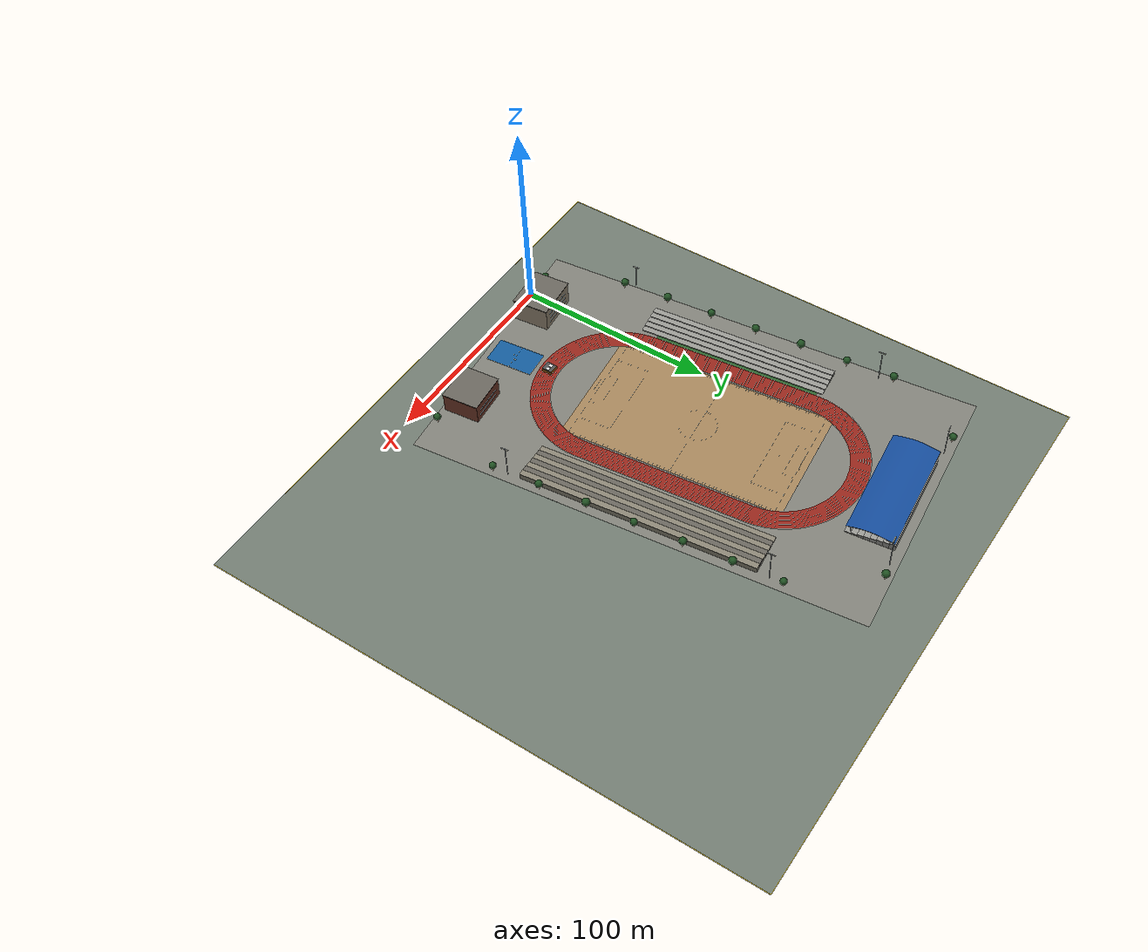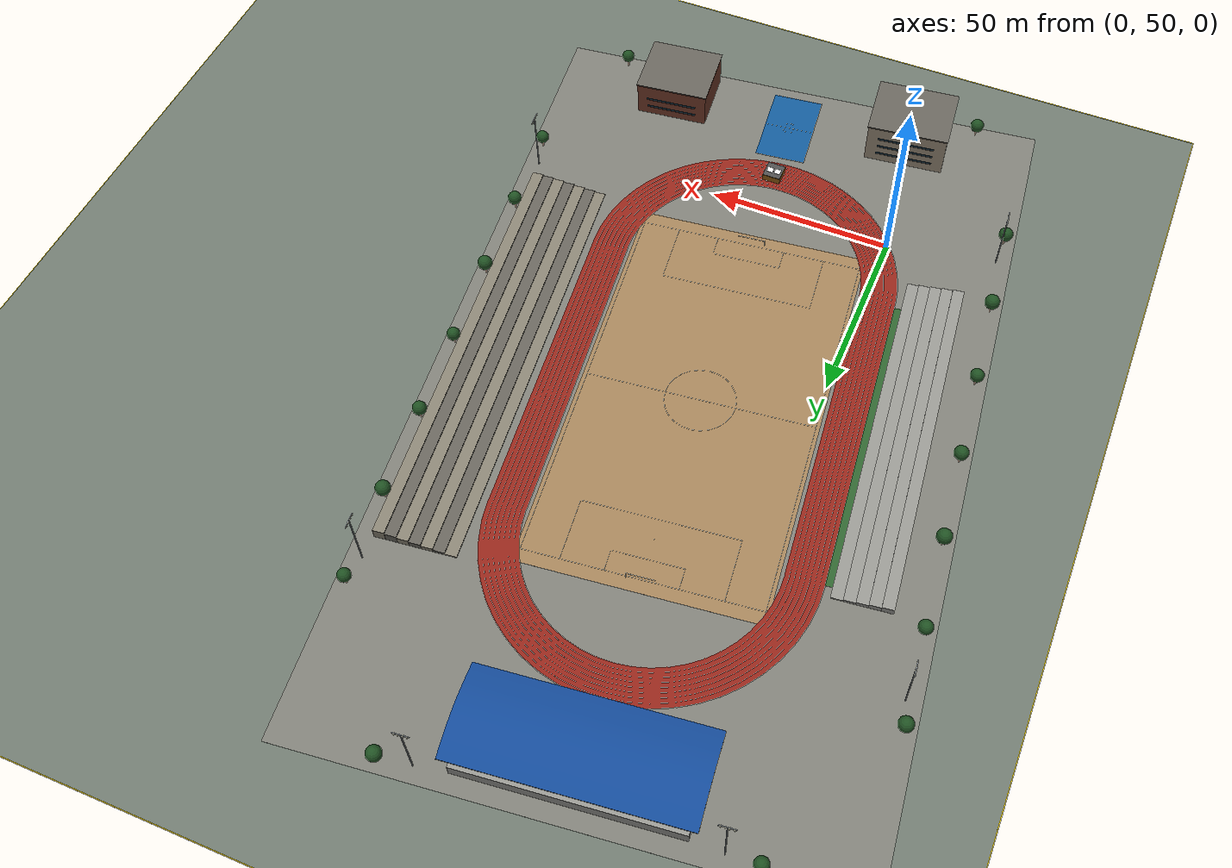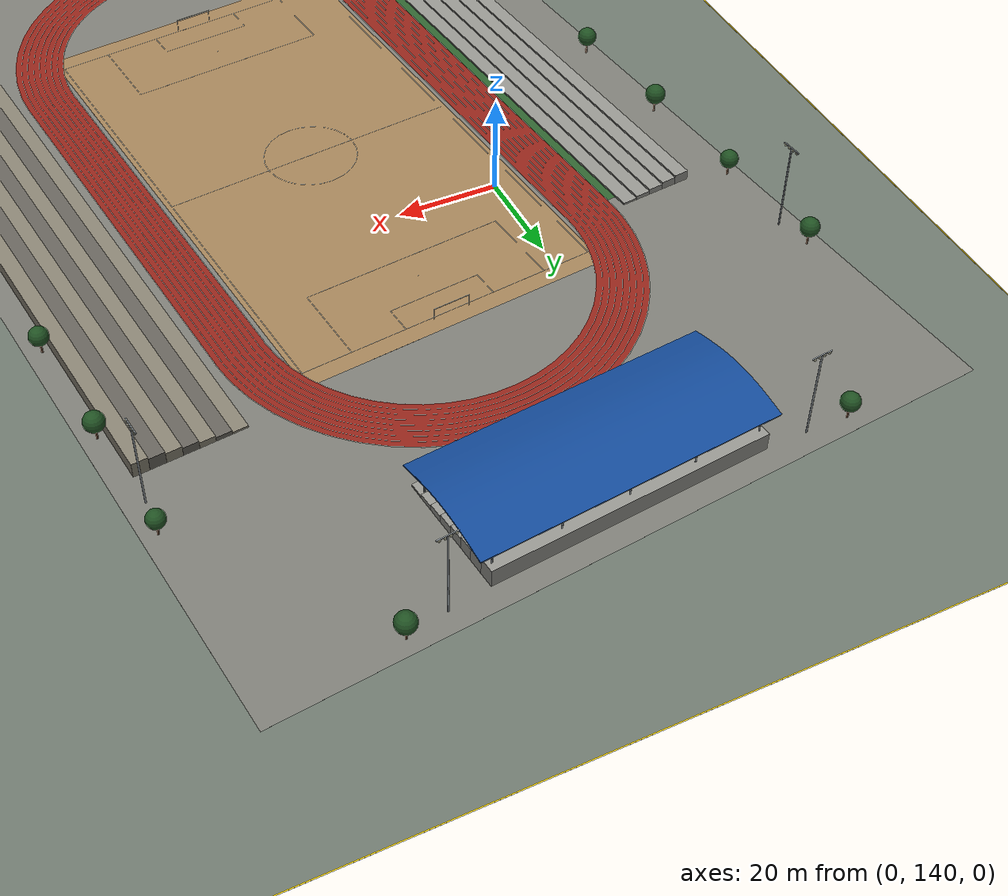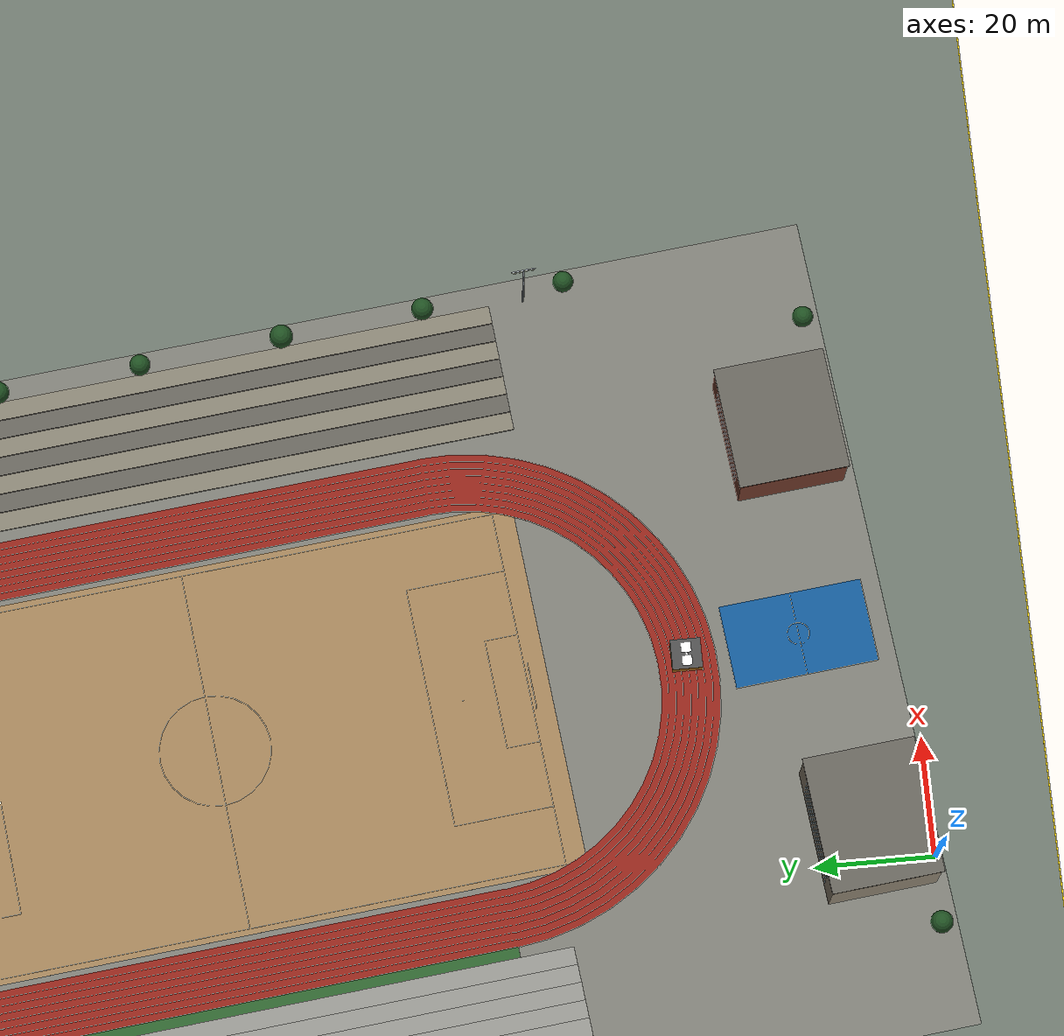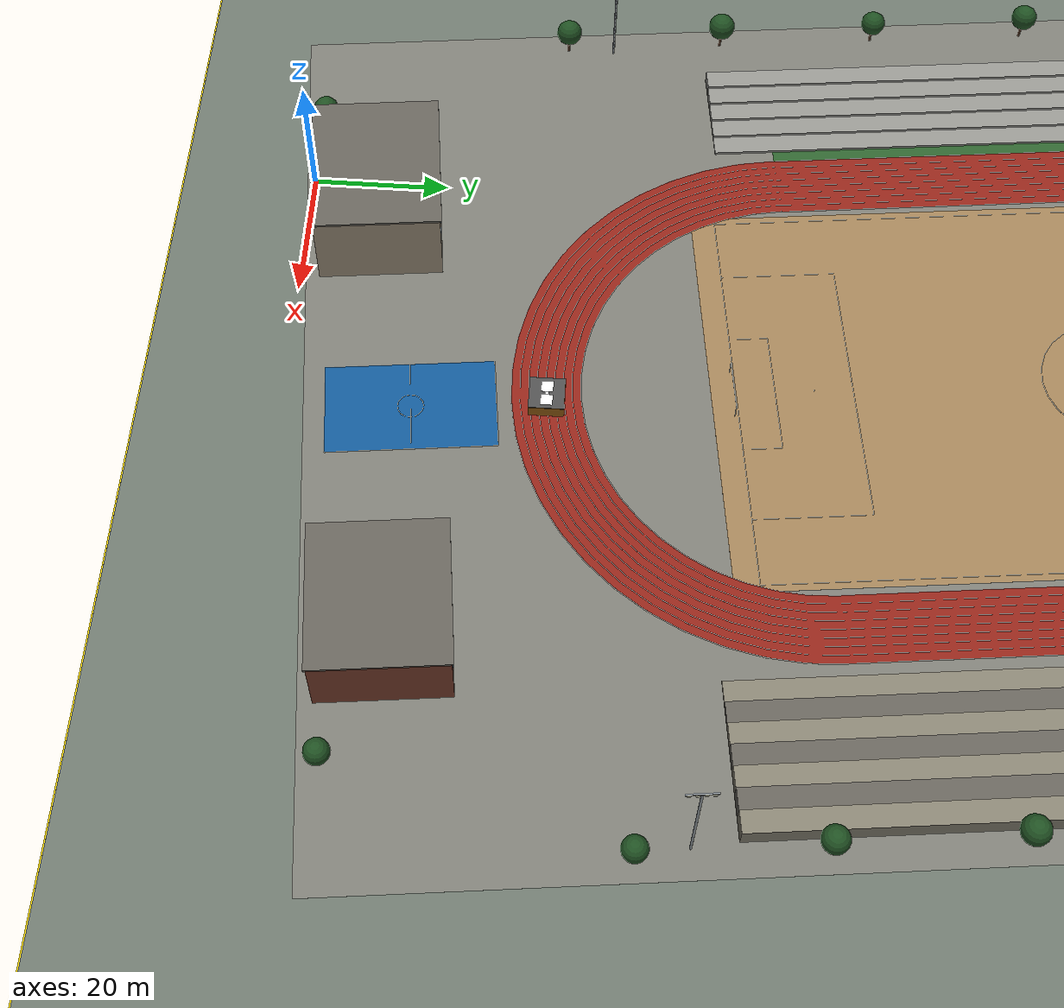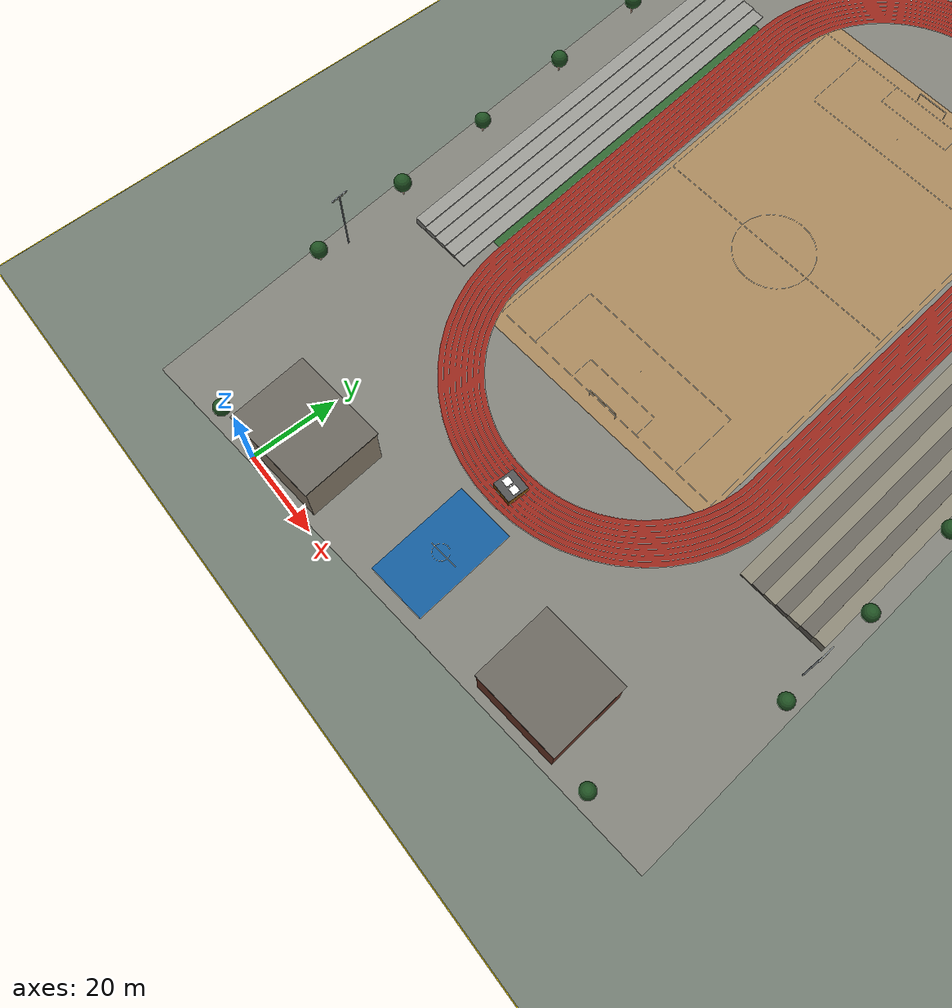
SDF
<?xml version="1.0" encoding="UTF-8"?>
<sdf version="1.9">
  <world name="DRONE_CJU_TRACK">
    <magnetic_field>6.0e-6 2.3e-5 -4.2e-5</magnetic_field>
    <atmosphere type="adiabatic"/>

    <plugin filename="gz-sim-physics-system" name="gz::sim::systems::Physics"/>
    <plugin filename="gz-sim-user-commands-system" name="gz::sim::systems::UserCommands"/>
    <plugin filename="gz-sim-scene-broadcaster-system" name="gz::sim::systems::SceneBroadcaster"/>
    <plugin filename="gz-sim-contact-system" name="gz::sim::systems::Contact"/>
    <plugin filename="gz-sim-sensors-system" name="gz::sim::systems::Sensors">
      <render_engine>ogre2</render_engine>
    </plugin>
    <plugin filename="gz-sim-imu-system" name="gz::sim::systems::Imu"/>
    <plugin filename="gz-sim-air-pressure-system" name="gz::sim::systems::AirPressure"/>
    <plugin filename="gz-sim-magnetometer-system" name="gz::sim::systems::Magnetometer"/>
    <plugin filename="gz-sim-navsat-system" name="gz::sim::systems::NavSat"/>

    <physics name="2ms" type="ignored">
      <max_step_size>0.002</max_step_size>
      <real_time_factor>1.0</real_time_factor>
      <real_time_update_rate>500</real_time_update_rate>
    </physics>
    <gravity>0 0 -9.8066</gravity>

    <scene>
      <ambient>0.58 0.60 0.62 1</ambient>
      <background>0.62 0.75 0.88 1</background>
      <grid>true</grid>
      <origin_visual>true</origin_visual>
      <sky/>
    </scene>
    <light type="directional" name="sun">
      <pose>100 100 300 0 0 0</pose>
      <diffuse>0.90 0.88 0.82 1</diffuse>
      <specular>0.10 0.10 0.10 1</specular>
      <direction>-0.35 0.25 -0.90</direction>
      <cast_shadows>true</cast_shadows>
    </light>

    <gui fullscreen="0">
      <plugin filename="MinimalScene" name="3D View">
        <gz-gui>
          <title>DRONE CJU TRACK - Red Track / Smooth Grandstand Roof</title>
          <property type="bool" key="showTitleBar">false</property>
          <property type="string" key="state">docked</property>
        </gz-gui>
        <engine>ogre2</engine>
        <scene>scene</scene>
        <ambient_light>0.58 0.60 0.62</ambient_light>
        <background_color>0.62 0.75 0.88</background_color>
        <camera_pose>130 -10 180 0 0.72 2.25</camera_pose>
        <camera_clip><near>0.2</near><far>1000</far></camera_clip>
      </plugin>
      <plugin filename="GzSceneManager" name="Scene Manager"/>
      <plugin filename="InteractiveViewControl" name="Interactive view control"/>
      <plugin filename="CameraTracking" name="Camera Tracking"/>
      <plugin filename="EntityTree" name="Entity tree"/>
      <plugin filename="WorldControl" name="World control">
        <play_pause>true</play_pause><step>true</step><start_paused>true</start_paused>
      </plugin>
      <plugin filename="WorldStats" name="World stats">
        <sim_time>true</sim_time><real_time_factor>true</real_time_factor>
      </plugin>
    </gui>

    <spherical_coordinates>
      <surface_model>EARTH_WGS84</surface_model>
      <latitude_deg>36.65440</latitude_deg>
      <longitude_deg>127.49591</longitude_deg>
      <elevation>74.0</elevation>
      <heading_deg>0</heading_deg>
    </spherical_coordinates>

    <model name="experiment_ground">
      <static>true</static>
      <pose>70 120 0 0 0 0</pose>
      <link name="ground">
        <collision name="collision">
          <pose>0 0 -0.05 0 0 0</pose>
          <geometry><box><size>280 280 0.1</size></box></geometry>
        </collision>
        <visual name="visual">
          <pose>0 0 -0.05 0 0 0</pose>
          <cast_shadows>false</cast_shadows>
          <geometry><box><size>280 280 0.1</size></box></geometry>
          <material>
            <ambient>0.30 0.34 0.30 1</ambient>
            <diffuse>0.42 0.46 0.42 1</diffuse>
            <specular>0.02 0.02 0.02 1</specular>
          </material>
        </visual>
      </link>
    </model>

    <model name="map_boundary">
      <static>true</static>
      <link name="boundary">
        <visual name="south"><pose>70 -20 0.006 0 0 0</pose><geometry><box><size>280 0.20 0.012</size></box></geometry><material><ambient>1 0.82 0.05 1</ambient><diffuse>1 0.82 0.05 1</diffuse></material></visual>
        <visual name="north"><pose>70 260 0.006 0 0 0</pose><geometry><box><size>280 0.20 0.012</size></box></geometry><material><ambient>1 0.82 0.05 1</ambient><diffuse>1 0.82 0.05 1</diffuse></material></visual>
        <visual name="west"><pose>-70 120 0.006 0 0 0</pose><geometry><box><size>0.20 280 0.012</size></box></geometry><material><ambient>1 0.82 0.05 1</ambient><diffuse>1 0.82 0.05 1</diffuse></material></visual>
        <visual name="east"><pose>210 120 0.006 0 0 0</pose><geometry><box><size>0.20 280 0.012</size></box></geometry><material><ambient>1 0.82 0.05 1</ambient><diffuse>1 0.82 0.05 1</diffuse></material></visual>
      </link>
    </model>

    <include>
      <uri>model://drone_cju_track_stadium</uri>
      <name>drone_cju_track_stadium</name>
      <pose>28.402605907228356 115.5890134880474 0 0 0 1.6807520696705394</pose>
    </include>
    <include>
      <uri>model://drone_cju_track_running_track</uri>
      <name>drone_cju_track_running_track</name>
      <pose>28.402605907228356 115.5890134880474 0 0 0 1.6807520696705394</pose>
    </include>

    <frame name="drone_spawn"><pose>30 30 0 0 0 0</pose></frame>
    <frame name="trailer_spawn"><pose>37.071067811865476 37.071067811865476 0 0 0 0</pose></frame>
    <include>
      <uri>model://moving_platform_aruco_velocity</uri>
      <name>trailer</name>
      <pose>37.071067811865476 37.071067811865476 0 0 0 0</pose>
    </include>

    <!-- PX4 SITL dynamically creates x500_city_rgbd_lidar at (30,30,0). -->
  </world>
</sdf>

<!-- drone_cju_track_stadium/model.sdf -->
<sdf version="1.9">
  <!-- Generated by gen_drone_cju_track_models.py. -->
  <!-- Dedicated primitive stadium plus a locally generated closed roof OBJ. -->
  <model name="drone_cju_track_stadium">
    <static>true</static>
    <link name="stadium_link">
      <visual name="stadium_plaza">
        <pose>0.0000 0.0000 0.0020 0.000000 0.000000 0.000000</pose>
        <cast_shadows>false</cast_shadows>
        <geometry>
          <box><size>226.0000 138.0000 0.0040</size></box>
        </geometry>
        <material>
          <ambient>0.48 0.48 0.45 1.0</ambient>
          <diffuse>0.48 0.48 0.45 1.0</diffuse>
          <specular>0.04 0.04 0.04 1</specular>
        </material>
      </visual>
      <visual name="dirt_infield">
        <pose>0.0000 0.0000 0.0070 0.000000 0.000000 0.000000</pose>
        <cast_shadows>false</cast_shadows>
        <geometry>
          <box><size>112.0000 62.0000 0.0060</size></box>
        </geometry>
        <material>
          <ambient>0.62 0.5 0.34 1.0</ambient>
          <diffuse>0.62 0.5 0.34 1.0</diffuse>
          <specular>0.04 0.04 0.04 1</specular>
        </material>
      </visual>
      <visual name="pitch_side_north">
        <pose>0.0000 30.0000 0.0145 0.000000 0.000000 0.000000</pose>
        <cast_shadows>false</cast_shadows>
        <geometry>
          <box><size>105.0000 0.0900 0.0020</size></box>
        </geometry>
        <material>
          <ambient>0.94 0.94 0.88 1.0</ambient>
          <diffuse>0.94 0.94 0.88 1.0</diffuse>
          <specular>0.04 0.04 0.04 1</specular>
        </material>
      </visual>
      <visual name="pitch_side_south">
        <pose>0.0000 -30.0000 0.0145 0.000000 0.000000 0.000000</pose>
        <cast_shadows>false</cast_shadows>
        <geometry>
          <box><size>105.0000 0.0900 0.0020</size></box>
        </geometry>
        <material>
          <ambient>0.94 0.94 0.88 1.0</ambient>
          <diffuse>0.94 0.94 0.88 1.0</diffuse>
          <specular>0.04 0.04 0.04 1</specular>
        </material>
      </visual>
      <visual name="pitch_end_east">
        <pose>52.5000 0.0000 0.0145 0.000000 0.000000 0.000000</pose>
        <cast_shadows>false</cast_shadows>
        <geometry>
          <box><size>0.0900 60.0000 0.0020</size></box>
        </geometry>
        <material>
          <ambient>0.94 0.94 0.88 1.0</ambient>
          <diffuse>0.94 0.94 0.88 1.0</diffuse>
          <specular>0.04 0.04 0.04 1</specular>
        </material>
      </visual>
      <visual name="pitch_end_west">
        <pose>-52.5000 0.0000 0.0145 0.000000 0.000000 0.000000</pose>
        <cast_shadows>false</cast_shadows>
        <geometry>
          <box><size>0.0900 60.0000 0.0020</size></box>
        </geometry>
        <material>
          <ambient>0.94 0.94 0.88 1.0</ambient>
          <diffuse>0.94 0.94 0.88 1.0</diffuse>
          <specular>0.04 0.04 0.04 1</specular>
        </material>
      </visual>
      <visual name="pitch_halfway">
        <pose>0.0000 0.0000 0.0145 0.000000 0.000000 0.000000</pose>
        <cast_shadows>false</cast_shadows>
        <geometry>
          <box><size>0.0900 60.0000 0.0020</size></box>
        </geometry>
        <material>
          <ambient>0.94 0.94 0.88 1.0</ambient>
          <diffuse>0.94 0.94 0.88 1.0</diffuse>
          <specular>0.04 0.04 0.04 1</specular>
        </material>
      </visual>
      <visual name="pitch_centre_circle_0">
        <pose>9.0717 1.1943 0.0145 0.000000 0.000000 1.701696</pose>
        <cast_shadows>false</cast_shadows>
        <geometry>
          <box><size>2.4842 0.0900 0.0020</size></box>
        </geometry>
        <material>
          <ambient>0.94 0.94 0.88 1.0</ambient>
          <diffuse>0.94 0.94 0.88 1.0</diffuse>
          <specular>0.04 0.04 0.04 1</specular>
        </material>
      </visual>
      <visual name="pitch_centre_circle_1">
        <pose>8.4535 3.5016 0.0145 0.000000 0.000000 1.963495</pose>
        <cast_shadows>false</cast_shadows>
        <geometry>
          <box><size>2.4842 0.0900 0.0020</size></box>
        </geometry>
        <material>
          <ambient>0.94 0.94 0.88 1.0</ambient>
          <diffuse>0.94 0.94 0.88 1.0</diffuse>
          <specular>0.04 0.04 0.04 1</specular>
        </material>
      </visual>
      <visual name="pitch_centre_circle_2">
        <pose>7.2592 5.5702 0.0145 0.000000 0.000000 2.225295</pose>
        <cast_shadows>false</cast_shadows>
        <geometry>
          <box><size>2.4842 0.0900 0.0020</size></box>
        </geometry>
        <material>
          <ambient>0.94 0.94 0.88 1.0</ambient>
          <diffuse>0.94 0.94 0.88 1.0</diffuse>
          <specular>0.04 0.04 0.04 1</specular>
        </material>
      </visual>
      <visual name="pitch_centre_circle_3">
        <pose>5.5702 7.2592 0.0145 0.000000 0.000000 2.487094</pose>
        <cast_shadows>false</cast_shadows>
        <geometry>
          <box><size>2.4842 0.0900 0.0020</size></box>
        </geometry>
        <material>
          <ambient>0.94 0.94 0.88 1.0</ambient>
          <diffuse>0.94 0.94 0.88 1.0</diffuse>
          <specular>0.04 0.04 0.04 1</specular>
        </material>
      </visual>
      <visual name="pitch_centre_circle_4">
        <pose>3.5016 8.4535 0.0145 0.000000 0.000000 2.748894</pose>
        <cast_shadows>false</cast_shadows>
        <geometry>
          <box><size>2.4842 0.0900 0.0020</size></box>
        </geometry>
        <material>
          <ambient>0.94 0.94 0.88 1.0</ambient>
          <diffuse>0.94 0.94 0.88 1.0</diffuse>
          <specular>0.04 0.04 0.04 1</specular>
        </material>
      </visual>
      <visual name="pitch_centre_circle_5">
        <pose>1.1943 9.0717 0.0145 0.000000 0.000000 3.010693</pose>
        <cast_shadows>false</cast_shadows>
        <geometry>
          <box><size>2.4842 0.0900 0.0020</size></box>
        </geometry>
        <material>
          <ambient>0.94 0.94 0.88 1.0</ambient>
          <diffuse>0.94 0.94 0.88 1.0</diffuse>
          <specular>0.04 0.04 0.04 1</specular>
        </material>
      </visual>
      <visual name="pitch_centre_circle_6">
        <pose>-1.1943 9.0717 0.0145 0.000000 0.000000 3.272492</pose>
        <cast_shadows>false</cast_shadows>
        <geometry>
          <box><size>2.4842 0.0900 0.0020</size></box>
        </geometry>
        <material>
          <ambient>0.94 0.94 0.88 1.0</ambient>
          <diffuse>0.94 0.94 0.88 1.0</diffuse>
          <specular>0.04 0.04 0.04 1</specular>
        </material>
      </visual>
      <visual name="pitch_centre_circle_7">
        <pose>-3.5016 8.4535 0.0145 0.000000 0.000000 3.534292</pose>
        <cast_shadows>false</cast_shadows>
        <geometry>
          <box><size>2.4842 0.0900 0.0020</size></box>
        </geometry>
        <material>
          <ambient>0.94 0.94 0.88 1.0</ambient>
          <diffuse>0.94 0.94 0.88 1.0</diffuse>
          <specular>0.04 0.04 0.04 1</specular>
        </material>
      </visual>
      <visual name="pitch_centre_circle_8">
        <pose>-5.5702 7.2592 0.0145 0.000000 0.000000 3.796091</pose>
        <cast_shadows>false</cast_shadows>
        <geometry>
          <box><size>2.4842 0.0900 0.0020</size></box>
        </geometry>
        <material>
          <ambient>0.94 0.94 0.88 1.0</ambient>
          <diffuse>0.94 0.94 0.88 1.0</diffuse>
          <specular>0.04 0.04 0.04 1</specular>
        </material>
      </visual>
      <visual name="pitch_centre_circle_9">
        <pose>-7.2592 5.5702 0.0145 0.000000 0.000000 4.057891</pose>
        <cast_shadows>false</cast_shadows>
        <geometry>
          <box><size>2.4842 0.0900 0.0020</size></box>
        </geometry>
        <material>
          <ambient>0.94 0.94 0.88 1.0</ambient>
          <diffuse>0.94 0.94 0.88 1.0</diffuse>
          <specular>0.04 0.04 0.04 1</specular>
        </material>
      </visual>
      <visual name="pitch_centre_circle_10">
        <pose>-8.4535 3.5016 0.0145 0.000000 0.000000 4.319690</pose>
        <cast_shadows>false</cast_shadows>
        <geometry>
          <box><size>2.4842 0.0900 0.0020</size></box>
        </geometry>
        <material>
          <ambient>0.94 0.94 0.88 1.0</ambient>
          <diffuse>0.94 0.94 0.88 1.0</diffuse>
          <specular>0.04 0.04 0.04 1</specular>
        </material>
      </visual>
      <visual name="pitch_centre_circle_11">
        <pose>-9.0717 1.1943 0.0145 0.000000 0.000000 4.581489</pose>
        <cast_shadows>false</cast_shadows>
        <geometry>
          <box><size>2.4842 0.0900 0.0020</size></box>
        </geometry>
        <material>
          <ambient>0.94 0.94 0.88 1.0</ambient>
          <diffuse>0.94 0.94 0.88 1.0</diffuse>
          <specular>0.04 0.04 0.04 1</specular>
        </material>
      </visual>
      <visual name="pitch_centre_circle_12">
        <pose>-9.0717 -1.1943 0.0145 0.000000 0.000000 4.843289</pose>
        <cast_shadows>false</cast_shadows>
        <geometry>
          <box><size>2.4842 0.0900 0.0020</size></box>
        </geometry>
        <material>
          <ambient>0.94 0.94 0.88 1.0</ambient>
          <diffuse>0.94 0.94 0.88 1.0</diffuse>
          <specular>0.04 0.04 0.04 1</specular>
        </material>
      </visual>
      <visual name="pitch_centre_circle_13">
        <pose>-8.4535 -3.5016 0.0145 0.000000 0.000000 5.105088</pose>
        <cast_shadows>false</cast_shadows>
        <geometry>
          <box><size>2.4842 0.0900 0.0020</size></box>
        </geometry>
        <material>
          <ambient>0.94 0.94 0.88 1.0</ambient>
          <diffuse>0.94 0.94 0.88 1.0</diffuse>
          <specular>0.04 0.04 0.04 1</specular>
        </material>
      </visual>
      <visual name="pitch_centre_circle_14">
        <pose>-7.2592 -5.5702 0.0145 0.000000 0.000000 5.366887</pose>
        <cast_shadows>false</cast_shadows>
        <geometry>
          <box><size>2.4842 0.0900 0.0020</size></box>
        </geometry>
        <material>
          <ambient>0.94 0.94 0.88 1.0</ambient>
          <diffuse>0.94 0.94 0.88 1.0</diffuse>
          <specular>0.04 0.04 0.04 1</specular>
        </material>
      </visual>
      <visual name="pitch_centre_circle_15">
        <pose>-5.5702 -7.2592 0.0145 0.000000 0.000000 5.628687</pose>
        <cast_shadows>false</cast_shadows>
        <geometry>
          <box><size>2.4842 0.0900 0.0020</size></box>
        </geometry>
        <material>
          <ambient>0.94 0.94 0.88 1.0</ambient>
          <diffuse>0.94 0.94 0.88 1.0</diffuse>
          <specular>0.04 0.04 0.04 1</specular>
        </material>
      </visual>
      <visual name="pitch_centre_circle_16">
        <pose>-3.5016 -8.4535 0.0145 0.000000 0.000000 5.890486</pose>
        <cast_shadows>false</cast_shadows>
        <geometry>
          <box><size>2.4842 0.0900 0.0020</size></box>
        </geometry>
        <material>
          <ambient>0.94 0.94 0.88 1.0</ambient>
          <diffuse>0.94 0.94 0.88 1.0</diffuse>
          <specular>0.04 0.04 0.04 1</specular>
        </material>
      </visual>
      <visual name="pitch_centre_circle_17">
        <pose>-1.1943 -9.0717 0.0145 0.000000 0.000000 6.152286</pose>
        <cast_shadows>false</cast_shadows>
        <geometry>
          <box><size>2.4842 0.0900 0.0020</size></box>
        </geometry>
        <material>
          <ambient>0.94 0.94 0.88 1.0</ambient>
          <diffuse>0.94 0.94 0.88 1.0</diffuse>
          <specular>0.04 0.04 0.04 1</specular>
        </material>
      </visual>
      <visual name="pitch_centre_circle_18">
        <pose>1.1943 -9.0717 0.0145 0.000000 0.000000 6.414085</pose>
        <cast_shadows>false</cast_shadows>
        <geometry>
          <box><size>2.4842 0.0900 0.0020</size></box>
        </geometry>
        <material>
          <ambient>0.94 0.94 0.88 1.0</ambient>
          <diffuse>0.94 0.94 0.88 1.0</diffuse>
          <specular>0.04 0.04 0.04 1</specular>
        </material>
      </visual>
      <visual name="pitch_centre_circle_19">
        <pose>3.5016 -8.4535 0.0145 0.000000 0.000000 6.675884</pose>
        <cast_shadows>false</cast_shadows>
        <geometry>
          <box><size>2.4842 0.0900 0.0020</size></box>
        </geometry>
        <material>
          <ambient>0.94 0.94 0.88 1.0</ambient>
          <diffuse>0.94 0.94 0.88 1.0</diffuse>
          <specular>0.04 0.04 0.04 1</specular>
        </material>
      </visual>
      <visual name="pitch_centre_circle_20">
        <pose>5.5702 -7.2592 0.0145 0.000000 0.000000 6.937684</pose>
        <cast_shadows>false</cast_shadows>
        <geometry>
          <box><size>2.4842 0.0900 0.0020</size></box>
        </geometry>
        <material>
          <ambient>0.94 0.94 0.88 1.0</ambient>
          <diffuse>0.94 0.94 0.88 1.0</diffuse>
          <specular>0.04 0.04 0.04 1</specular>
        </material>
      </visual>
      <visual name="pitch_centre_circle_21">
        <pose>7.2592 -5.5702 0.0145 0.000000 0.000000 7.199483</pose>
        <cast_shadows>false</cast_shadows>
        <geometry>
          <box><size>2.4842 0.0900 0.0020</size></box>
        </geometry>
        <material>
          <ambient>0.94 0.94 0.88 1.0</ambient>
          <diffuse>0.94 0.94 0.88 1.0</diffuse>
          <specular>0.04 0.04 0.04 1</specular>
        </material>
      </visual>
      <visual name="pitch_centre_circle_22">
        <pose>8.4535 -3.5016 0.0145 0.000000 0.000000 7.461283</pose>
        <cast_shadows>false</cast_shadows>
        <geometry>
          <box><size>2.4842 0.0900 0.0020</size></box>
        </geometry>
        <material>
          <ambient>0.94 0.94 0.88 1.0</ambient>
          <diffuse>0.94 0.94 0.88 1.0</diffuse>
          <specular>0.04 0.04 0.04 1</specular>
        </material>
      </visual>
      <visual name="pitch_centre_circle_23">
        <pose>9.0717 -1.1943 0.0145 0.000000 0.000000 7.723082</pose>
        <cast_shadows>false</cast_shadows>
        <geometry>
          <box><size>2.4842 0.0900 0.0020</size></box>
        </geometry>
        <material>
          <ambient>0.94 0.94 0.88 1.0</ambient>
          <diffuse>0.94 0.94 0.88 1.0</diffuse>
          <specular>0.04 0.04 0.04 1</specular>
        </material>
      </visual>
      <visual name="pitch_centre_spot">
        <pose>0.0000 0.0000 0.0145 0.000000 0.000000 0.000000</pose>
        <cast_shadows>false</cast_shadows>
        <geometry>
          <cylinder><radius>0.1200</radius><length>0.0020</length></cylinder>
        </geometry>
        <material>
          <ambient>0.94 0.94 0.88 1.0</ambient>
          <diffuse>0.94 0.94 0.88 1.0</diffuse>
          <specular>0.04 0.04 0.04 1</specular>
        </material>
      </visual>
      <visual name="east_penalty_inner">
        <pose>36.0000 0.0000 0.0145 0.000000 0.000000 0.000000</pose>
        <cast_shadows>false</cast_shadows>
        <geometry>
          <box><size>0.0900 40.3200 0.0020</size></box>
        </geometry>
        <material>
          <ambient>0.94 0.94 0.88 1.0</ambient>
          <diffuse>0.94 0.94 0.88 1.0</diffuse>
          <specular>0.04 0.04 0.04 1</specular>
        </material>
      </visual>
      <visual name="east_penalty_top">
        <pose>44.2500 20.1600 0.0145 0.000000 0.000000 0.000000</pose>
        <cast_shadows>false</cast_shadows>
        <geometry>
          <box><size>16.5000 0.0900 0.0020</size></box>
        </geometry>
        <material>
          <ambient>0.94 0.94 0.88 1.0</ambient>
          <diffuse>0.94 0.94 0.88 1.0</diffuse>
          <specular>0.04 0.04 0.04 1</specular>
        </material>
      </visual>
      <visual name="east_penalty_bottom">
        <pose>44.2500 -20.1600 0.0145 0.000000 0.000000 0.000000</pose>
        <cast_shadows>false</cast_shadows>
        <geometry>
          <box><size>16.5000 0.0900 0.0020</size></box>
        </geometry>
        <material>
          <ambient>0.94 0.94 0.88 1.0</ambient>
          <diffuse>0.94 0.94 0.88 1.0</diffuse>
          <specular>0.04 0.04 0.04 1</specular>
        </material>
      </visual>
      <visual name="east_goal_area_inner">
        <pose>47.0000 0.0000 0.0145 0.000000 0.000000 0.000000</pose>
        <cast_shadows>false</cast_shadows>
        <geometry>
          <box><size>0.0900 18.3200 0.0020</size></box>
        </geometry>
        <material>
          <ambient>0.94 0.94 0.88 1.0</ambient>
          <diffuse>0.94 0.94 0.88 1.0</diffuse>
          <specular>0.04 0.04 0.04 1</specular>
        </material>
      </visual>
      <visual name="east_goal_area_top">
        <pose>49.7500 9.1600 0.0145 0.000000 0.000000 0.000000</pose>
        <cast_shadows>false</cast_shadows>
        <geometry>
          <box><size>5.5000 0.0900 0.0020</size></box>
        </geometry>
        <material>
          <ambient>0.94 0.94 0.88 1.0</ambient>
          <diffuse>0.94 0.94 0.88 1.0</diffuse>
          <specular>0.04 0.04 0.04 1</specular>
        </material>
      </visual>
      <visual name="east_goal_area_bottom">
        <pose>49.7500 -9.1600 0.0145 0.000000 0.000000 0.000000</pose>
        <cast_shadows>false</cast_shadows>
        <geometry>
          <box><size>5.5000 0.0900 0.0020</size></box>
        </geometry>
        <material>
          <ambient>0.94 0.94 0.88 1.0</ambient>
          <diffuse>0.94 0.94 0.88 1.0</diffuse>
          <specular>0.04 0.04 0.04 1</specular>
        </material>
      </visual>
      <visual name="east_penalty_spot">
        <pose>41.5000 0.0000 0.0145 0.000000 0.000000 0.000000</pose>
        <cast_shadows>false</cast_shadows>
        <geometry>
          <cylinder><radius>0.1000</radius><length>0.0020</length></cylinder>
        </geometry>
        <material>
          <ambient>0.94 0.94 0.88 1.0</ambient>
          <diffuse>0.94 0.94 0.88 1.0</diffuse>
          <specular>0.04 0.04 0.04 1</specular>
        </material>
      </visual>
      <visual name="west_penalty_inner">
        <pose>-36.0000 0.0000 0.0145 0.000000 0.000000 0.000000</pose>
        <cast_shadows>false</cast_shadows>
        <geometry>
          <box><size>0.0900 40.3200 0.0020</size></box>
        </geometry>
        <material>
          <ambient>0.94 0.94 0.88 1.0</ambient>
          <diffuse>0.94 0.94 0.88 1.0</diffuse>
          <specular>0.04 0.04 0.04 1</specular>
        </material>
      </visual>
      <visual name="west_penalty_top">
        <pose>-44.2500 20.1600 0.0145 0.000000 0.000000 0.000000</pose>
        <cast_shadows>false</cast_shadows>
        <geometry>
          <box><size>16.5000 0.0900 0.0020</size></box>
        </geometry>
        <material>
          <ambient>0.94 0.94 0.88 1.0</ambient>
          <diffuse>0.94 0.94 0.88 1.0</diffuse>
          <specular>0.04 0.04 0.04 1</specular>
        </material>
      </visual>
      <visual name="west_penalty_bottom">
        <pose>-44.2500 -20.1600 0.0145 0.000000 0.000000 0.000000</pose>
        <cast_shadows>false</cast_shadows>
        <geometry>
          <box><size>16.5000 0.0900 0.0020</size></box>
        </geometry>
        <material>
          <ambient>0.94 0.94 0.88 1.0</ambient>
          <diffuse>0.94 0.94 0.88 1.0</diffuse>
          <specular>0.04 0.04 0.04 1</specular>
        </material>
      </visual>
      <visual name="west_goal_area_inner">
        <pose>-47.0000 0.0000 0.0145 0.000000 0.000000 0.000000</pose>
        <cast_shadows>false</cast_shadows>
        <geometry>
          <box><size>0.0900 18.3200 0.0020</size></box>
        </geometry>
        <material>
          <ambient>0.94 0.94 0.88 1.0</ambient>
          <diffuse>0.94 0.94 0.88 1.0</diffuse>
          <specular>0.04 0.04 0.04 1</specular>
        </material>
      </visual>
      <visual name="west_goal_area_top">
        <pose>-49.7500 9.1600 0.0145 0.000000 0.000000 0.000000</pose>
        <cast_shadows>false</cast_shadows>
        <geometry>
          <box><size>5.5000 0.0900 0.0020</size></box>
        </geometry>
        <material>
          <ambient>0.94 0.94 0.88 1.0</ambient>
          <diffuse>0.94 0.94 0.88 1.0</diffuse>
          <specular>0.04 0.04 0.04 1</specular>
        </material>
      </visual>
      <visual name="west_goal_area_bottom">
        <pose>-49.7500 -9.1600 0.0145 0.000000 0.000000 0.000000</pose>
        <cast_shadows>false</cast_shadows>
        <geometry>
          <box><size>5.5000 0.0900 0.0020</size></box>
        </geometry>
        <material>
          <ambient>0.94 0.94 0.88 1.0</ambient>
          <diffuse>0.94 0.94 0.88 1.0</diffuse>
          <specular>0.04 0.04 0.04 1</specular>
        </material>
      </visual>
      <visual name="west_penalty_spot">
        <pose>-41.5000 0.0000 0.0145 0.000000 0.000000 0.000000</pose>
        <cast_shadows>false</cast_shadows>
        <geometry>
          <cylinder><radius>0.1000</radius><length>0.0020</length></cylinder>
        </geometry>
        <material>
          <ambient>0.94 0.94 0.88 1.0</ambient>
          <diffuse>0.94 0.94 0.88 1.0</diffuse>
          <specular>0.04 0.04 0.04 1</specular>
        </material>
      </visual>
      <visual name="goal_east_north_post">
        <pose>53.0000 3.6600 1.2200 0.000000 0.000000 0.000000</pose>
        <cast_shadows>true</cast_shadows>
        <geometry>
          <cylinder><radius>0.0550</radius><length>2.4400</length></cylinder>
        </geometry>
        <material>
          <ambient>0.94 0.94 0.88 1.0</ambient>
          <diffuse>0.94 0.94 0.88 1.0</diffuse>
          <specular>0.04 0.04 0.04 1</specular>
        </material>
      </visual>
      <visual name="goal_east_south_post">
        <pose>53.0000 -3.6600 1.2200 0.000000 0.000000 0.000000</pose>
        <cast_shadows>true</cast_shadows>
        <geometry>
          <cylinder><radius>0.0550</radius><length>2.4400</length></cylinder>
        </geometry>
        <material>
          <ambient>0.94 0.94 0.88 1.0</ambient>
          <diffuse>0.94 0.94 0.88 1.0</diffuse>
          <specular>0.04 0.04 0.04 1</specular>
        </material>
      </visual>
      <visual name="goal_east_crossbar">
        <pose>53.0000 0.0000 2.4400 0.000000 0.000000 0.000000</pose>
        <cast_shadows>true</cast_shadows>
        <geometry>
          <box><size>0.1100 7.4300 0.1100</size></box>
        </geometry>
        <material>
          <ambient>0.94 0.94 0.88 1.0</ambient>
          <diffuse>0.94 0.94 0.88 1.0</diffuse>
          <specular>0.04 0.04 0.04 1</specular>
        </material>
      </visual>
      <visual name="goal_west_north_post">
        <pose>-53.0000 3.6600 1.2200 0.000000 0.000000 0.000000</pose>
        <cast_shadows>true</cast_shadows>
        <geometry>
          <cylinder><radius>0.0550</radius><length>2.4400</length></cylinder>
        </geometry>
        <material>
          <ambient>0.94 0.94 0.88 1.0</ambient>
          <diffuse>0.94 0.94 0.88 1.0</diffuse>
          <specular>0.04 0.04 0.04 1</specular>
        </material>
      </visual>
      <visual name="goal_west_south_post">
        <pose>-53.0000 -3.6600 1.2200 0.000000 0.000000 0.000000</pose>
        <cast_shadows>true</cast_shadows>
        <geometry>
          <cylinder><radius>0.0550</radius><length>2.4400</length></cylinder>
        </geometry>
        <material>
          <ambient>0.94 0.94 0.88 1.0</ambient>
          <diffuse>0.94 0.94 0.88 1.0</diffuse>
          <specular>0.04 0.04 0.04 1</specular>
        </material>
      </visual>
      <visual name="goal_west_crossbar">
        <pose>-53.0000 0.0000 2.4400 0.000000 0.000000 0.000000</pose>
        <cast_shadows>true</cast_shadows>
        <geometry>
          <box><size>0.1100 7.4300 0.1100</size></box>
        </geometry>
        <material>
          <ambient>0.94 0.94 0.88 1.0</ambient>
          <diffuse>0.94 0.94 0.88 1.0</diffuse>
          <specular>0.04 0.04 0.04 1</specular>
        </material>
      </visual>
      <visual name="south_blue_court">
        <pose>-98.0000 0.0000 0.0070 0.000000 0.000000 0.000000</pose>
        <cast_shadows>false</cast_shadows>
        <geometry>
          <box><size>24.0000 14.0000 0.0060</size></box>
        </geometry>
        <material>
          <ambient>0.07 0.34 0.58 1.0</ambient>
          <diffuse>0.07 0.34 0.58 1.0</diffuse>
          <specular>0.04 0.04 0.04 1</specular>
        </material>
      </visual>
      <visual name="court_side_north">
        <pose>-98.0000 7.0000 0.0145 0.000000 0.000000 0.000000</pose>
        <cast_shadows>false</cast_shadows>
        <geometry>
          <box><size>24.0000 0.0700 0.0020</size></box>
        </geometry>
        <material>
          <ambient>0.94 0.94 0.88 1.0</ambient>
          <diffuse>0.94 0.94 0.88 1.0</diffuse>
          <specular>0.04 0.04 0.04 1</specular>
        </material>
      </visual>
      <visual name="court_side_south">
        <pose>-98.0000 -7.0000 0.0145 0.000000 0.000000 0.000000</pose>
        <cast_shadows>false</cast_shadows>
        <geometry>
          <box><size>24.0000 0.0700 0.0020</size></box>
        </geometry>
        <material>
          <ambient>0.94 0.94 0.88 1.0</ambient>
          <diffuse>0.94 0.94 0.88 1.0</diffuse>
          <specular>0.04 0.04 0.04 1</specular>
        </material>
      </visual>
      <visual name="court_end_east">
        <pose>-86.0000 0.0000 0.0145 0.000000 0.000000 0.000000</pose>
        <cast_shadows>false</cast_shadows>
        <geometry>
          <box><size>0.0700 14.0000 0.0020</size></box>
        </geometry>
        <material>
          <ambient>0.94 0.94 0.88 1.0</ambient>
          <diffuse>0.94 0.94 0.88 1.0</diffuse>
          <specular>0.04 0.04 0.04 1</specular>
        </material>
      </visual>
      <visual name="court_end_west">
        <pose>-110.0000 0.0000 0.0145 0.000000 0.000000 0.000000</pose>
        <cast_shadows>false</cast_shadows>
        <geometry>
          <box><size>0.0700 14.0000 0.0020</size></box>
        </geometry>
        <material>
          <ambient>0.94 0.94 0.88 1.0</ambient>
          <diffuse>0.94 0.94 0.88 1.0</diffuse>
          <specular>0.04 0.04 0.04 1</specular>
        </material>
      </visual>
      <visual name="court_halfway">
        <pose>-98.0000 0.0000 0.0145 0.000000 0.000000 0.000000</pose>
        <cast_shadows>false</cast_shadows>
        <geometry>
          <box><size>0.0700 14.0000 0.0020</size></box>
        </geometry>
        <material>
          <ambient>0.94 0.94 0.88 1.0</ambient>
          <diffuse>0.94 0.94 0.88 1.0</diffuse>
          <specular>0.04 0.04 0.04 1</specular>
        </material>
      </visual>
      <visual name="court_centre_circle_0">
        <pose>-96.2346 0.3512 0.0145 0.000000 0.000000 1.767146</pose>
        <cast_shadows>false</cast_shadows>
        <geometry>
          <box><size>0.7304 0.0700 0.0020</size></box>
        </geometry>
        <material>
          <ambient>0.94 0.94 0.88 1.0</ambient>
          <diffuse>0.94 0.94 0.88 1.0</diffuse>
          <specular>0.04 0.04 0.04 1</specular>
        </material>
      </visual>
      <visual name="court_centre_circle_1">
        <pose>-96.5034 1.0000 0.0145 0.000000 0.000000 2.159845</pose>
        <cast_shadows>false</cast_shadows>
        <geometry>
          <box><size>0.7304 0.0700 0.0020</size></box>
        </geometry>
        <material>
          <ambient>0.94 0.94 0.88 1.0</ambient>
          <diffuse>0.94 0.94 0.88 1.0</diffuse>
          <specular>0.04 0.04 0.04 1</specular>
        </material>
      </visual>
      <visual name="court_centre_circle_2">
        <pose>-97.0000 1.4966 0.0145 0.000000 0.000000 2.552544</pose>
        <cast_shadows>false</cast_shadows>
        <geometry>
          <box><size>0.7304 0.0700 0.0020</size></box>
        </geometry>
        <material>
          <ambient>0.94 0.94 0.88 1.0</ambient>
          <diffuse>0.94 0.94 0.88 1.0</diffuse>
          <specular>0.04 0.04 0.04 1</specular>
        </material>
      </visual>
      <visual name="court_centre_circle_3">
        <pose>-97.6488 1.7654 0.0145 0.000000 0.000000 2.945243</pose>
        <cast_shadows>false</cast_shadows>
        <geometry>
          <box><size>0.7304 0.0700 0.0020</size></box>
        </geometry>
        <material>
          <ambient>0.94 0.94 0.88 1.0</ambient>
          <diffuse>0.94 0.94 0.88 1.0</diffuse>
          <specular>0.04 0.04 0.04 1</specular>
        </material>
      </visual>
      <visual name="court_centre_circle_4">
        <pose>-98.3512 1.7654 0.0145 0.000000 0.000000 3.337942</pose>
        <cast_shadows>false</cast_shadows>
        <geometry>
          <box><size>0.7304 0.0700 0.0020</size></box>
        </geometry>
        <material>
          <ambient>0.94 0.94 0.88 1.0</ambient>
          <diffuse>0.94 0.94 0.88 1.0</diffuse>
          <specular>0.04 0.04 0.04 1</specular>
        </material>
      </visual>
      <visual name="court_centre_circle_5">
        <pose>-99.0000 1.4966 0.0145 0.000000 0.000000 3.730641</pose>
        <cast_shadows>false</cast_shadows>
        <geometry>
          <box><size>0.7304 0.0700 0.0020</size></box>
        </geometry>
        <material>
          <ambient>0.94 0.94 0.88 1.0</ambient>
          <diffuse>0.94 0.94 0.88 1.0</diffuse>
          <specular>0.04 0.04 0.04 1</specular>
        </material>
      </visual>
      <visual name="court_centre_circle_6">
        <pose>-99.4966 1.0000 0.0145 0.000000 0.000000 4.123340</pose>
        <cast_shadows>false</cast_shadows>
        <geometry>
          <box><size>0.7304 0.0700 0.0020</size></box>
        </geometry>
        <material>
          <ambient>0.94 0.94 0.88 1.0</ambient>
          <diffuse>0.94 0.94 0.88 1.0</diffuse>
          <specular>0.04 0.04 0.04 1</specular>
        </material>
      </visual>
      <visual name="court_centre_circle_7">
        <pose>-99.7654 0.3512 0.0145 0.000000 0.000000 4.516039</pose>
        <cast_shadows>false</cast_shadows>
        <geometry>
          <box><size>0.7304 0.0700 0.0020</size></box>
        </geometry>
        <material>
          <ambient>0.94 0.94 0.88 1.0</ambient>
          <diffuse>0.94 0.94 0.88 1.0</diffuse>
          <specular>0.04 0.04 0.04 1</specular>
        </material>
      </visual>
      <visual name="court_centre_circle_8">
        <pose>-99.7654 -0.3512 0.0145 0.000000 0.000000 4.908739</pose>
        <cast_shadows>false</cast_shadows>
        <geometry>
          <box><size>0.7304 0.0700 0.0020</size></box>
        </geometry>
        <material>
          <ambient>0.94 0.94 0.88 1.0</ambient>
          <diffuse>0.94 0.94 0.88 1.0</diffuse>
          <specular>0.04 0.04 0.04 1</specular>
        </material>
      </visual>
      <visual name="court_centre_circle_9">
        <pose>-99.4966 -1.0000 0.0145 0.000000 0.000000 5.301438</pose>
        <cast_shadows>false</cast_shadows>
        <geometry>
          <box><size>0.7304 0.0700 0.0020</size></box>
        </geometry>
        <material>
          <ambient>0.94 0.94 0.88 1.0</ambient>
          <diffuse>0.94 0.94 0.88 1.0</diffuse>
          <specular>0.04 0.04 0.04 1</specular>
        </material>
      </visual>
      <visual name="court_centre_circle_10">
        <pose>-99.0000 -1.4966 0.0145 0.000000 0.000000 5.694137</pose>
        <cast_shadows>false</cast_shadows>
        <geometry>
          <box><size>0.7304 0.0700 0.0020</size></box>
        </geometry>
        <material>
          <ambient>0.94 0.94 0.88 1.0</ambient>
          <diffuse>0.94 0.94 0.88 1.0</diffuse>
          <specular>0.04 0.04 0.04 1</specular>
        </material>
      </visual>
      <visual name="court_centre_circle_11">
        <pose>-98.3512 -1.7654 0.0145 0.000000 0.000000 6.086836</pose>
        <cast_shadows>false</cast_shadows>
        <geometry>
          <box><size>0.7304 0.0700 0.0020</size></box>
        </geometry>
        <material>
          <ambient>0.94 0.94 0.88 1.0</ambient>
          <diffuse>0.94 0.94 0.88 1.0</diffuse>
          <specular>0.04 0.04 0.04 1</specular>
        </material>
      </visual>
      <visual name="court_centre_circle_12">
        <pose>-97.6488 -1.7654 0.0145 0.000000 0.000000 6.479535</pose>
        <cast_shadows>false</cast_shadows>
        <geometry>
          <box><size>0.7304 0.0700 0.0020</size></box>
        </geometry>
        <material>
          <ambient>0.94 0.94 0.88 1.0</ambient>
          <diffuse>0.94 0.94 0.88 1.0</diffuse>
          <specular>0.04 0.04 0.04 1</specular>
        </material>
      </visual>
      <visual name="court_centre_circle_13">
        <pose>-97.0000 -1.4966 0.0145 0.000000 0.000000 6.872234</pose>
        <cast_shadows>false</cast_shadows>
        <geometry>
          <box><size>0.7304 0.0700 0.0020</size></box>
        </geometry>
        <material>
          <ambient>0.94 0.94 0.88 1.0</ambient>
          <diffuse>0.94 0.94 0.88 1.0</diffuse>
          <specular>0.04 0.04 0.04 1</specular>
        </material>
      </visual>
      <visual name="court_centre_circle_14">
        <pose>-96.5034 -1.0000 0.0145 0.000000 0.000000 7.264933</pose>
        <cast_shadows>false</cast_shadows>
        <geometry>
          <box><size>0.7304 0.0700 0.0020</size></box>
        </geometry>
        <material>
          <ambient>0.94 0.94 0.88 1.0</ambient>
          <diffuse>0.94 0.94 0.88 1.0</diffuse>
          <specular>0.04 0.04 0.04 1</specular>
        </material>
      </visual>
      <visual name="court_centre_circle_15">
        <pose>-96.2346 -0.3512 0.0145 0.000000 0.000000 7.657632</pose>
        <cast_shadows>false</cast_shadows>
        <geometry>
          <box><size>0.7304 0.0700 0.0020</size></box>
        </geometry>
        <material>
          <ambient>0.94 0.94 0.88 1.0</ambient>
          <diffuse>0.94 0.94 0.88 1.0</diffuse>
          <specular>0.04 0.04 0.04 1</specular>
        </material>
      </visual>
      <visual name="east_stone_step_0">
        <pose>0.0000 -45.0000 0.2150 0.000000 0.000000 0.000000</pose>
        <cast_shadows>true</cast_shadows>
        <geometry>
          <box><size>118.0000 3.0000 0.4300</size></box>
        </geometry>
        <material>
          <ambient>0.52 0.5 0.44 1.0</ambient>
          <diffuse>0.52 0.5 0.44 1.0</diffuse>
          <specular>0.04 0.04 0.04 1</specular>
        </material>
      </visual>
      <visual name="east_stone_step_1">
        <pose>0.0000 -48.0000 0.4300 0.000000 0.000000 0.000000</pose>
        <cast_shadows>true</cast_shadows>
        <geometry>
          <box><size>118.0000 3.0000 0.8600</size></box>
        </geometry>
        <material>
          <ambient>0.39 0.38 0.35 1.0</ambient>
          <diffuse>0.39 0.38 0.35 1.0</diffuse>
          <specular>0.04 0.04 0.04 1</specular>
        </material>
      </visual>
      <visual name="east_stone_step_2">
        <pose>0.0000 -51.0000 0.6450 0.000000 0.000000 0.000000</pose>
        <cast_shadows>true</cast_shadows>
        <geometry>
          <box><size>118.0000 3.0000 1.2900</size></box>
        </geometry>
        <material>
          <ambient>0.52 0.5 0.44 1.0</ambient>
          <diffuse>0.52 0.5 0.44 1.0</diffuse>
          <specular>0.04 0.04 0.04 1</specular>
        </material>
      </visual>
      <visual name="east_stone_step_3">
        <pose>0.0000 -54.0000 0.8600 0.000000 0.000000 0.000000</pose>
        <cast_shadows>true</cast_shadows>
        <geometry>
          <box><size>118.0000 3.0000 1.7200</size></box>
        </geometry>
        <material>
          <ambient>0.39 0.38 0.35 1.0</ambient>
          <diffuse>0.39 0.38 0.35 1.0</diffuse>
          <specular>0.04 0.04 0.04 1</specular>
        </material>
      </visual>
      <visual name="east_stone_step_4">
        <pose>0.0000 -57.0000 1.0750 0.000000 0.000000 0.000000</pose>
        <cast_shadows>true</cast_shadows>
        <geometry>
          <box><size>118.0000 3.0000 2.1500</size></box>
        </geometry>
        <material>
          <ambient>0.52 0.5 0.44 1.0</ambient>
          <diffuse>0.52 0.5 0.44 1.0</diffuse>
          <specular>0.04 0.04 0.04 1</specular>
        </material>
      </visual>
      <visual name="east_stone_step_5">
        <pose>0.0000 -60.0000 1.2900 0.000000 0.000000 0.000000</pose>
        <cast_shadows>true</cast_shadows>
        <geometry>
          <box><size>118.0000 3.0000 2.5800</size></box>
        </geometry>
        <material>
          <ambient>0.39 0.38 0.35 1.0</ambient>
          <diffuse>0.39 0.38 0.35 1.0</diffuse>
          <specular>0.04 0.04 0.04 1</specular>
        </material>
      </visual>
      <visual name="east_stone_step_6">
        <pose>0.0000 -63.0000 1.5050 0.000000 0.000000 0.000000</pose>
        <cast_shadows>true</cast_shadows>
        <geometry>
          <box><size>118.0000 3.0000 3.0100</size></box>
        </geometry>
        <material>
          <ambient>0.52 0.5 0.44 1.0</ambient>
          <diffuse>0.52 0.5 0.44 1.0</diffuse>
          <specular>0.04 0.04 0.04 1</specular>
        </material>
      </visual>
      <visual name="west_concrete_step_0">
        <pose>-3.0000 45.0000 0.2000 0.000000 0.000000 0.000000</pose>
        <cast_shadows>true</cast_shadows>
        <geometry>
          <box><size>96.0000 3.0000 0.4000</size></box>
        </geometry>
        <material>
          <ambient>0.57 0.57 0.55 1.0</ambient>
          <diffuse>0.57 0.57 0.55 1.0</diffuse>
          <specular>0.04 0.04 0.04 1</specular>
        </material>
      </visual>
      <visual name="west_concrete_step_1">
        <pose>-3.0000 48.0000 0.4000 0.000000 0.000000 0.000000</pose>
        <cast_shadows>true</cast_shadows>
        <geometry>
          <box><size>96.0000 3.0000 0.8000</size></box>
        </geometry>
        <material>
          <ambient>0.57 0.57 0.55 1.0</ambient>
          <diffuse>0.57 0.57 0.55 1.0</diffuse>
          <specular>0.04 0.04 0.04 1</specular>
        </material>
      </visual>
      <visual name="west_concrete_step_2">
        <pose>-3.0000 51.0000 0.6000 0.000000 0.000000 0.000000</pose>
        <cast_shadows>true</cast_shadows>
        <geometry>
          <box><size>96.0000 3.0000 1.2000</size></box>
        </geometry>
        <material>
          <ambient>0.57 0.57 0.55 1.0</ambient>
          <diffuse>0.57 0.57 0.55 1.0</diffuse>
          <specular>0.04 0.04 0.04 1</specular>
        </material>
      </visual>
      <visual name="west_concrete_step_3">
        <pose>-3.0000 54.0000 0.8000 0.000000 0.000000 0.000000</pose>
        <cast_shadows>true</cast_shadows>
        <geometry>
          <box><size>96.0000 3.0000 1.6000</size></box>
        </geometry>
        <material>
          <ambient>0.57 0.57 0.55 1.0</ambient>
          <diffuse>0.57 0.57 0.55 1.0</diffuse>
          <specular>0.04 0.04 0.04 1</specular>
        </material>
      </visual>
      <visual name="west_concrete_step_4">
        <pose>-3.0000 57.0000 1.0000 0.000000 0.000000 0.000000</pose>
        <cast_shadows>true</cast_shadows>
        <geometry>
          <box><size>96.0000 3.0000 2.0000</size></box>
        </geometry>
        <material>
          <ambient>0.57 0.57 0.55 1.0</ambient>
          <diffuse>0.57 0.57 0.55 1.0</diffuse>
          <specular>0.04 0.04 0.04 1</specular>
        </material>
      </visual>
      <visual name="north_grandstand_step_0">
        <pose>86.0000 0.0000 0.2300 0.000000 0.000000 0.000000</pose>
        <cast_shadows>true</cast_shadows>
        <geometry>
          <box><size>3.0000 54.0000 0.4600</size></box>
        </geometry>
        <material>
          <ambient>0.57 0.57 0.55 1.0</ambient>
          <diffuse>0.57 0.57 0.55 1.0</diffuse>
          <specular>0.04 0.04 0.04 1</specular>
        </material>
      </visual>
      <visual name="north_grandstand_step_1">
        <pose>89.0000 0.0000 0.4600 0.000000 0.000000 0.000000</pose>
        <cast_shadows>true</cast_shadows>
        <geometry>
          <box><size>3.0000 54.0000 0.9200</size></box>
        </geometry>
        <material>
          <ambient>0.57 0.57 0.55 1.0</ambient>
          <diffuse>0.57 0.57 0.55 1.0</diffuse>
          <specular>0.04 0.04 0.04 1</specular>
        </material>
      </visual>
      <visual name="north_grandstand_step_2">
        <pose>92.0000 0.0000 0.6900 0.000000 0.000000 0.000000</pose>
        <cast_shadows>true</cast_shadows>
        <geometry>
          <box><size>3.0000 54.0000 1.3800</size></box>
        </geometry>
        <material>
          <ambient>0.57 0.57 0.55 1.0</ambient>
          <diffuse>0.57 0.57 0.55 1.0</diffuse>
          <specular>0.04 0.04 0.04 1</specular>
        </material>
      </visual>
      <visual name="north_grandstand_step_3">
        <pose>95.0000 0.0000 0.9200 0.000000 0.000000 0.000000</pose>
        <cast_shadows>true</cast_shadows>
        <geometry>
          <box><size>3.0000 54.0000 1.8400</size></box>
        </geometry>
        <material>
          <ambient>0.57 0.57 0.55 1.0</ambient>
          <diffuse>0.57 0.57 0.55 1.0</diffuse>
          <specular>0.04 0.04 0.04 1</specular>
        </material>
      </visual>
      <visual name="north_grandstand_step_4">
        <pose>98.0000 0.0000 1.1500 0.000000 0.000000 0.000000</pose>
        <cast_shadows>true</cast_shadows>
        <geometry>
          <box><size>3.0000 54.0000 2.3000</size></box>
        </geometry>
        <material>
          <ambient>0.57 0.57 0.55 1.0</ambient>
          <diffuse>0.57 0.57 0.55 1.0</diffuse>
          <specular>0.04 0.04 0.04 1</specular>
        </material>
      </visual>
      <visual name="north_grandstand_step_5">
        <pose>101.0000 0.0000 1.3800 0.000000 0.000000 0.000000</pose>
        <cast_shadows>true</cast_shadows>
        <geometry>
          <box><size>3.0000 54.0000 2.7600</size></box>
        </geometry>
        <material>
          <ambient>0.57 0.57 0.55 1.0</ambient>
          <diffuse>0.57 0.57 0.55 1.0</diffuse>
          <specular>0.04 0.04 0.04 1</specular>
        </material>
      </visual>
      <visual name="north_grandstand_step_6">
        <pose>104.0000 0.0000 1.6100 0.000000 0.000000 0.000000</pose>
        <cast_shadows>true</cast_shadows>
        <geometry>
          <box><size>3.0000 54.0000 3.2200</size></box>
        </geometry>
        <material>
          <ambient>0.57 0.57 0.55 1.0</ambient>
          <diffuse>0.57 0.57 0.55 1.0</diffuse>
          <specular>0.04 0.04 0.04 1</specular>
        </material>
      </visual>
      <visual name="north_grandstand_step_7">
        <pose>107.0000 0.0000 1.8400 0.000000 0.000000 0.000000</pose>
        <cast_shadows>true</cast_shadows>
        <geometry>
          <box><size>3.0000 54.0000 3.6800</size></box>
        </geometry>
        <material>
          <ambient>0.57 0.57 0.55 1.0</ambient>
          <diffuse>0.57 0.57 0.55 1.0</diffuse>
          <specular>0.04 0.04 0.04 1</specular>
        </material>
      </visual>
      <visual name="north_roof_column_87_-26">
        <pose>87.0000 -26.0000 3.6000 0.000000 0.000000 0.000000</pose>
        <cast_shadows>true</cast_shadows>
        <geometry>
          <cylinder><radius>0.1500</radius><length>7.2000</length></cylinder>
        </geometry>
        <material>
          <ambient>0.58 0.61 0.63 1.0</ambient>
          <diffuse>0.58 0.61 0.63 1.0</diffuse>
          <specular>0.04 0.04 0.04 1</specular>
        </material>
      </visual>
      <visual name="north_roof_column_87_-13">
        <pose>87.0000 -13.0000 3.6000 0.000000 0.000000 0.000000</pose>
        <cast_shadows>true</cast_shadows>
        <geometry>
          <cylinder><radius>0.1500</radius><length>7.2000</length></cylinder>
        </geometry>
        <material>
          <ambient>0.58 0.61 0.63 1.0</ambient>
          <diffuse>0.58 0.61 0.63 1.0</diffuse>
          <specular>0.04 0.04 0.04 1</specular>
        </material>
      </visual>
      <visual name="north_roof_column_87_0">
        <pose>87.0000 0.0000 3.6000 0.000000 0.000000 0.000000</pose>
        <cast_shadows>true</cast_shadows>
        <geometry>
          <cylinder><radius>0.1500</radius><length>7.2000</length></cylinder>
        </geometry>
        <material>
          <ambient>0.58 0.61 0.63 1.0</ambient>
          <diffuse>0.58 0.61 0.63 1.0</diffuse>
          <specular>0.04 0.04 0.04 1</specular>
        </material>
      </visual>
      <visual name="north_roof_column_87_13">
        <pose>87.0000 13.0000 3.6000 0.000000 0.000000 0.000000</pose>
        <cast_shadows>true</cast_shadows>
        <geometry>
          <cylinder><radius>0.1500</radius><length>7.2000</length></cylinder>
        </geometry>
        <material>
          <ambient>0.58 0.61 0.63 1.0</ambient>
          <diffuse>0.58 0.61 0.63 1.0</diffuse>
          <specular>0.04 0.04 0.04 1</specular>
        </material>
      </visual>
      <visual name="north_roof_column_87_26">
        <pose>87.0000 26.0000 3.6000 0.000000 0.000000 0.000000</pose>
        <cast_shadows>true</cast_shadows>
        <geometry>
          <cylinder><radius>0.1500</radius><length>7.2000</length></cylinder>
        </geometry>
        <material>
          <ambient>0.58 0.61 0.63 1.0</ambient>
          <diffuse>0.58 0.61 0.63 1.0</diffuse>
          <specular>0.04 0.04 0.04 1</specular>
        </material>
      </visual>
      <visual name="north_roof_column_107_-26">
        <pose>107.0000 -26.0000 3.6000 0.000000 0.000000 0.000000</pose>
        <cast_shadows>true</cast_shadows>
        <geometry>
          <cylinder><radius>0.1500</radius><length>7.2000</length></cylinder>
        </geometry>
        <material>
          <ambient>0.58 0.61 0.63 1.0</ambient>
          <diffuse>0.58 0.61 0.63 1.0</diffuse>
          <specular>0.04 0.04 0.04 1</specular>
        </material>
      </visual>
      <visual name="north_roof_column_107_-13">
        <pose>107.0000 -13.0000 3.6000 0.000000 0.000000 0.000000</pose>
        <cast_shadows>true</cast_shadows>
        <geometry>
          <cylinder><radius>0.1500</radius><length>7.2000</length></cylinder>
        </geometry>
        <material>
          <ambient>0.58 0.61 0.63 1.0</ambient>
          <diffuse>0.58 0.61 0.63 1.0</diffuse>
          <specular>0.04 0.04 0.04 1</specular>
        </material>
      </visual>
      <visual name="north_roof_column_107_0">
        <pose>107.0000 0.0000 3.6000 0.000000 0.000000 0.000000</pose>
        <cast_shadows>true</cast_shadows>
        <geometry>
          <cylinder><radius>0.1500</radius><length>7.2000</length></cylinder>
        </geometry>
        <material>
          <ambient>0.58 0.61 0.63 1.0</ambient>
          <diffuse>0.58 0.61 0.63 1.0</diffuse>
          <specular>0.04 0.04 0.04 1</specular>
        </material>
      </visual>
      <visual name="north_roof_column_107_13">
        <pose>107.0000 13.0000 3.6000 0.000000 0.000000 0.000000</pose>
        <cast_shadows>true</cast_shadows>
        <geometry>
          <cylinder><radius>0.1500</radius><length>7.2000</length></cylinder>
        </geometry>
        <material>
          <ambient>0.58 0.61 0.63 1.0</ambient>
          <diffuse>0.58 0.61 0.63 1.0</diffuse>
          <specular>0.04 0.04 0.04 1</specular>
        </material>
      </visual>
      <visual name="north_roof_column_107_26">
        <pose>107.0000 26.0000 3.6000 0.000000 0.000000 0.000000</pose>
        <cast_shadows>true</cast_shadows>
        <geometry>
          <cylinder><radius>0.1500</radius><length>7.2000</length></cylinder>
        </geometry>
        <material>
          <ambient>0.58 0.61 0.63 1.0</ambient>
          <diffuse>0.58 0.61 0.63 1.0</diffuse>
          <specular>0.04 0.04 0.04 1</specular>
        </material>
      </visual>
      <visual name="tree_0_trunk">
        <pose>-72.0000 -66.0000 1.2000 0.000000 0.000000 0.000000</pose>
        <cast_shadows>true</cast_shadows>
        <geometry>
          <cylinder><radius>0.2000</radius><length>2.4000</length></cylinder>
        </geometry>
        <material>
          <ambient>0.24 0.14 0.07 1.0</ambient>
          <diffuse>0.24 0.14 0.07 1.0</diffuse>
          <specular>0.04 0.04 0.04 1</specular>
        </material>
      </visual>
      <visual name="tree_0_crown">
        <pose>-72.0000 -66.0000 3.6600 0 0 0</pose>
        <cast_shadows>true</cast_shadows>
        <geometry><sphere><radius>1.7500</radius></sphere></geometry>
        <material>
          <ambient>0.12 0.31 0.13 1.0</ambient>
          <diffuse>0.12 0.31 0.13 1.0</diffuse>
          <specular>0.04 0.04 0.04 1</specular>
        </material>
      </visual>
      <visual name="tree_1_trunk">
        <pose>-72.0000 66.0000 1.3080 0.000000 0.000000 0.000000</pose>
        <cast_shadows>true</cast_shadows>
        <geometry>
          <cylinder><radius>0.2000</radius><length>2.6160</length></cylinder>
        </geometry>
        <material>
          <ambient>0.24 0.14 0.07 1.0</ambient>
          <diffuse>0.24 0.14 0.07 1.0</diffuse>
          <specular>0.04 0.04 0.04 1</specular>
        </material>
      </visual>
      <visual name="tree_1_crown">
        <pose>-72.0000 66.0000 3.9894 0 0 0</pose>
        <cast_shadows>true</cast_shadows>
        <geometry><sphere><radius>1.9075</radius></sphere></geometry>
        <material>
          <ambient>0.12 0.31 0.13 1.0</ambient>
          <diffuse>0.12 0.31 0.13 1.0</diffuse>
          <specular>0.04 0.04 0.04 1</specular>
        </material>
      </visual>
      <visual name="tree_2_trunk">
        <pose>-48.0000 -66.0000 1.2720 0.000000 0.000000 0.000000</pose>
        <cast_shadows>true</cast_shadows>
        <geometry>
          <cylinder><radius>0.2000</radius><length>2.5440</length></cylinder>
        </geometry>
        <material>
          <ambient>0.24 0.14 0.07 1.0</ambient>
          <diffuse>0.24 0.14 0.07 1.0</diffuse>
          <specular>0.04 0.04 0.04 1</specular>
        </material>
      </visual>
      <visual name="tree_2_crown">
        <pose>-48.0000 -66.0000 3.8796 0 0 0</pose>
        <cast_shadows>true</cast_shadows>
        <geometry><sphere><radius>1.8550</radius></sphere></geometry>
        <material>
          <ambient>0.12 0.31 0.13 1.0</ambient>
          <diffuse>0.12 0.31 0.13 1.0</diffuse>
          <specular>0.04 0.04 0.04 1</specular>
        </material>
      </visual>
      <visual name="tree_3_trunk">
        <pose>-48.0000 66.0000 1.3680 0.000000 0.000000 0.000000</pose>
        <cast_shadows>true</cast_shadows>
        <geometry>
          <cylinder><radius>0.2000</radius><length>2.7360</length></cylinder>
        </geometry>
        <material>
          <ambient>0.24 0.14 0.07 1.0</ambient>
          <diffuse>0.24 0.14 0.07 1.0</diffuse>
          <specular>0.04 0.04 0.04 1</specular>
        </material>
      </visual>
      <visual name="tree_3_crown">
        <pose>-48.0000 66.0000 4.1724 0 0 0</pose>
        <cast_shadows>true</cast_shadows>
        <geometry><sphere><radius>1.9950</radius></sphere></geometry>
        <material>
          <ambient>0.12 0.31 0.13 1.0</ambient>
          <diffuse>0.12 0.31 0.13 1.0</diffuse>
          <specular>0.04 0.04 0.04 1</specular>
        </material>
      </visual>
      <visual name="tree_4_trunk">
        <pose>-24.0000 -66.0000 1.3440 0.000000 0.000000 0.000000</pose>
        <cast_shadows>true</cast_shadows>
        <geometry>
          <cylinder><radius>0.2000</radius><length>2.6880</length></cylinder>
        </geometry>
        <material>
          <ambient>0.24 0.14 0.07 1.0</ambient>
          <diffuse>0.24 0.14 0.07 1.0</diffuse>
          <specular>0.04 0.04 0.04 1</specular>
        </material>
      </visual>
      <visual name="tree_4_crown">
        <pose>-24.0000 -66.0000 4.0992 0 0 0</pose>
        <cast_shadows>true</cast_shadows>
        <geometry><sphere><radius>1.9600</radius></sphere></geometry>
        <material>
          <ambient>0.12 0.31 0.13 1.0</ambient>
          <diffuse>0.12 0.31 0.13 1.0</diffuse>
          <specular>0.04 0.04 0.04 1</specular>
        </material>
      </visual>
      <visual name="tree_5_trunk">
        <pose>-24.0000 66.0000 1.2480 0.000000 0.000000 0.000000</pose>
        <cast_shadows>true</cast_shadows>
        <geometry>
          <cylinder><radius>0.2000</radius><length>2.4960</length></cylinder>
        </geometry>
        <material>
          <ambient>0.24 0.14 0.07 1.0</ambient>
          <diffuse>0.24 0.14 0.07 1.0</diffuse>
          <specular>0.04 0.04 0.04 1</specular>
        </material>
      </visual>
      <visual name="tree_5_crown">
        <pose>-24.0000 66.0000 3.8064 0 0 0</pose>
        <cast_shadows>true</cast_shadows>
        <geometry><sphere><radius>1.8200</radius></sphere></geometry>
        <material>
          <ambient>0.12 0.31 0.13 1.0</ambient>
          <diffuse>0.12 0.31 0.13 1.0</diffuse>
          <specular>0.04 0.04 0.04 1</specular>
        </material>
      </visual>
      <visual name="tree_6_trunk">
        <pose>0.0000 -66.0000 1.2000 0.000000 0.000000 0.000000</pose>
        <cast_shadows>true</cast_shadows>
        <geometry>
          <cylinder><radius>0.2000</radius><length>2.4000</length></cylinder>
        </geometry>
        <material>
          <ambient>0.24 0.14 0.07 1.0</ambient>
          <diffuse>0.24 0.14 0.07 1.0</diffuse>
          <specular>0.04 0.04 0.04 1</specular>
        </material>
      </visual>
      <visual name="tree_6_crown">
        <pose>0.0000 -66.0000 3.6600 0 0 0</pose>
        <cast_shadows>true</cast_shadows>
        <geometry><sphere><radius>1.7500</radius></sphere></geometry>
        <material>
          <ambient>0.12 0.31 0.13 1.0</ambient>
          <diffuse>0.12 0.31 0.13 1.0</diffuse>
          <specular>0.04 0.04 0.04 1</specular>
        </material>
      </visual>
      <visual name="tree_7_trunk">
        <pose>0.0000 66.0000 1.3080 0.000000 0.000000 0.000000</pose>
        <cast_shadows>true</cast_shadows>
        <geometry>
          <cylinder><radius>0.2000</radius><length>2.6160</length></cylinder>
        </geometry>
        <material>
          <ambient>0.24 0.14 0.07 1.0</ambient>
          <diffuse>0.24 0.14 0.07 1.0</diffuse>
          <specular>0.04 0.04 0.04 1</specular>
        </material>
      </visual>
      <visual name="tree_7_crown">
        <pose>0.0000 66.0000 3.9894 0 0 0</pose>
        <cast_shadows>true</cast_shadows>
        <geometry><sphere><radius>1.9075</radius></sphere></geometry>
        <material>
          <ambient>0.12 0.31 0.13 1.0</ambient>
          <diffuse>0.12 0.31 0.13 1.0</diffuse>
          <specular>0.04 0.04 0.04 1</specular>
        </material>
      </visual>
      <visual name="tree_8_trunk">
        <pose>24.0000 -66.0000 1.2720 0.000000 0.000000 0.000000</pose>
        <cast_shadows>true</cast_shadows>
        <geometry>
          <cylinder><radius>0.2000</radius><length>2.5440</length></cylinder>
        </geometry>
        <material>
          <ambient>0.24 0.14 0.07 1.0</ambient>
          <diffuse>0.24 0.14 0.07 1.0</diffuse>
          <specular>0.04 0.04 0.04 1</specular>
        </material>
      </visual>
      <visual name="tree_8_crown">
        <pose>24.0000 -66.0000 3.8796 0 0 0</pose>
        <cast_shadows>true</cast_shadows>
        <geometry><sphere><radius>1.8550</radius></sphere></geometry>
        <material>
          <ambient>0.12 0.31 0.13 1.0</ambient>
          <diffuse>0.12 0.31 0.13 1.0</diffuse>
          <specular>0.04 0.04 0.04 1</specular>
        </material>
      </visual>
      <visual name="tree_9_trunk">
        <pose>24.0000 66.0000 1.3680 0.000000 0.000000 0.000000</pose>
        <cast_shadows>true</cast_shadows>
        <geometry>
          <cylinder><radius>0.2000</radius><length>2.7360</length></cylinder>
        </geometry>
        <material>
          <ambient>0.24 0.14 0.07 1.0</ambient>
          <diffuse>0.24 0.14 0.07 1.0</diffuse>
          <specular>0.04 0.04 0.04 1</specular>
        </material>
      </visual>
      <visual name="tree_9_crown">
        <pose>24.0000 66.0000 4.1724 0 0 0</pose>
        <cast_shadows>true</cast_shadows>
        <geometry><sphere><radius>1.9950</radius></sphere></geometry>
        <material>
          <ambient>0.12 0.31 0.13 1.0</ambient>
          <diffuse>0.12 0.31 0.13 1.0</diffuse>
          <specular>0.04 0.04 0.04 1</specular>
        </material>
      </visual>
      <visual name="tree_10_trunk">
        <pose>48.0000 -66.0000 1.3440 0.000000 0.000000 0.000000</pose>
        <cast_shadows>true</cast_shadows>
        <geometry>
          <cylinder><radius>0.2000</radius><length>2.6880</length></cylinder>
        </geometry>
        <material>
          <ambient>0.24 0.14 0.07 1.0</ambient>
          <diffuse>0.24 0.14 0.07 1.0</diffuse>
          <specular>0.04 0.04 0.04 1</specular>
        </material>
      </visual>
      <visual name="tree_10_crown">
        <pose>48.0000 -66.0000 4.0992 0 0 0</pose>
        <cast_shadows>true</cast_shadows>
        <geometry><sphere><radius>1.9600</radius></sphere></geometry>
        <material>
          <ambient>0.12 0.31 0.13 1.0</ambient>
          <diffuse>0.12 0.31 0.13 1.0</diffuse>
          <specular>0.04 0.04 0.04 1</specular>
        </material>
      </visual>
      <visual name="tree_11_trunk">
        <pose>48.0000 66.0000 1.2480 0.000000 0.000000 0.000000</pose>
        <cast_shadows>true</cast_shadows>
        <geometry>
          <cylinder><radius>0.2000</radius><length>2.4960</length></cylinder>
        </geometry>
        <material>
          <ambient>0.24 0.14 0.07 1.0</ambient>
          <diffuse>0.24 0.14 0.07 1.0</diffuse>
          <specular>0.04 0.04 0.04 1</specular>
        </material>
      </visual>
      <visual name="tree_11_crown">
        <pose>48.0000 66.0000 3.8064 0 0 0</pose>
        <cast_shadows>true</cast_shadows>
        <geometry><sphere><radius>1.8200</radius></sphere></geometry>
        <material>
          <ambient>0.12 0.31 0.13 1.0</ambient>
          <diffuse>0.12 0.31 0.13 1.0</diffuse>
          <specular>0.04 0.04 0.04 1</specular>
        </material>
      </visual>
      <visual name="tree_12_trunk">
        <pose>72.0000 -66.0000 1.2000 0.000000 0.000000 0.000000</pose>
        <cast_shadows>true</cast_shadows>
        <geometry>
          <cylinder><radius>0.2000</radius><length>2.4000</length></cylinder>
        </geometry>
        <material>
          <ambient>0.24 0.14 0.07 1.0</ambient>
          <diffuse>0.24 0.14 0.07 1.0</diffuse>
          <specular>0.04 0.04 0.04 1</specular>
        </material>
      </visual>
      <visual name="tree_12_crown">
        <pose>72.0000 -66.0000 3.6600 0 0 0</pose>
        <cast_shadows>true</cast_shadows>
        <geometry><sphere><radius>1.7500</radius></sphere></geometry>
        <material>
          <ambient>0.12 0.31 0.13 1.0</ambient>
          <diffuse>0.12 0.31 0.13 1.0</diffuse>
          <specular>0.04 0.04 0.04 1</specular>
        </material>
      </visual>
      <visual name="tree_13_trunk">
        <pose>72.0000 66.0000 1.3080 0.000000 0.000000 0.000000</pose>
        <cast_shadows>true</cast_shadows>
        <geometry>
          <cylinder><radius>0.2000</radius><length>2.6160</length></cylinder>
        </geometry>
        <material>
          <ambient>0.24 0.14 0.07 1.0</ambient>
          <diffuse>0.24 0.14 0.07 1.0</diffuse>
          <specular>0.04 0.04 0.04 1</specular>
        </material>
      </visual>
      <visual name="tree_13_crown">
        <pose>72.0000 66.0000 3.9894 0 0 0</pose>
        <cast_shadows>true</cast_shadows>
        <geometry><sphere><radius>1.9075</radius></sphere></geometry>
        <material>
          <ambient>0.12 0.31 0.13 1.0</ambient>
          <diffuse>0.12 0.31 0.13 1.0</diffuse>
          <specular>0.04 0.04 0.04 1</specular>
        </material>
      </visual>
      <visual name="tree_14_trunk">
        <pose>110.0000 -43.0000 1.3200 0.000000 0.000000 0.000000</pose>
        <cast_shadows>true</cast_shadows>
        <geometry>
          <cylinder><radius>0.2000</radius><length>2.6400</length></cylinder>
        </geometry>
        <material>
          <ambient>0.24 0.14 0.07 1.0</ambient>
          <diffuse>0.24 0.14 0.07 1.0</diffuse>
          <specular>0.04 0.04 0.04 1</specular>
        </material>
      </visual>
      <visual name="tree_14_crown">
        <pose>110.0000 -43.0000 4.0260 0 0 0</pose>
        <cast_shadows>true</cast_shadows>
        <geometry><sphere><radius>1.9250</radius></sphere></geometry>
        <material>
          <ambient>0.12 0.31 0.13 1.0</ambient>
          <diffuse>0.12 0.31 0.13 1.0</diffuse>
          <specular>0.04 0.04 0.04 1</specular>
        </material>
      </visual>
      <visual name="tree_15_trunk">
        <pose>110.0000 43.0000 1.2480 0.000000 0.000000 0.000000</pose>
        <cast_shadows>true</cast_shadows>
        <geometry>
          <cylinder><radius>0.2000</radius><length>2.4960</length></cylinder>
        </geometry>
        <material>
          <ambient>0.24 0.14 0.07 1.0</ambient>
          <diffuse>0.24 0.14 0.07 1.0</diffuse>
          <specular>0.04 0.04 0.04 1</specular>
        </material>
      </visual>
      <visual name="tree_15_crown">
        <pose>110.0000 43.0000 3.8064 0 0 0</pose>
        <cast_shadows>true</cast_shadows>
        <geometry><sphere><radius>1.8200</radius></sphere></geometry>
        <material>
          <ambient>0.12 0.31 0.13 1.0</ambient>
          <diffuse>0.12 0.31 0.13 1.0</diffuse>
          <specular>0.04 0.04 0.04 1</specular>
        </material>
      </visual>
      <visual name="tree_16_trunk">
        <pose>-110.0000 -52.0000 1.2000 0.000000 0.000000 0.000000</pose>
        <cast_shadows>true</cast_shadows>
        <geometry>
          <cylinder><radius>0.2000</radius><length>2.4000</length></cylinder>
        </geometry>
        <material>
          <ambient>0.24 0.14 0.07 1.0</ambient>
          <diffuse>0.24 0.14 0.07 1.0</diffuse>
          <specular>0.04 0.04 0.04 1</specular>
        </material>
      </visual>
      <visual name="tree_16_crown">
        <pose>-110.0000 -52.0000 3.6600 0 0 0</pose>
        <cast_shadows>true</cast_shadows>
        <geometry><sphere><radius>1.7500</radius></sphere></geometry>
        <material>
          <ambient>0.12 0.31 0.13 1.0</ambient>
          <diffuse>0.12 0.31 0.13 1.0</diffuse>
          <specular>0.04 0.04 0.04 1</specular>
        </material>
      </visual>
      <visual name="tree_17_trunk">
        <pose>-110.0000 52.0000 1.2720 0.000000 0.000000 0.000000</pose>
        <cast_shadows>true</cast_shadows>
        <geometry>
          <cylinder><radius>0.2000</radius><length>2.5440</length></cylinder>
        </geometry>
        <material>
          <ambient>0.24 0.14 0.07 1.0</ambient>
          <diffuse>0.24 0.14 0.07 1.0</diffuse>
          <specular>0.04 0.04 0.04 1</specular>
        </material>
      </visual>
      <visual name="tree_17_crown">
        <pose>-110.0000 52.0000 3.8796 0 0 0</pose>
        <cast_shadows>true</cast_shadows>
        <geometry><sphere><radius>1.8550</radius></sphere></geometry>
        <material>
          <ambient>0.12 0.31 0.13 1.0</ambient>
          <diffuse>0.12 0.31 0.13 1.0</diffuse>
          <specular>0.04 0.04 0.04 1</specular>
        </material>
      </visual>
      <visual name="floodlight_0_mast">
        <pose>-65.0000 -65.0000 9.0000 0.000000 0.000000 0.000000</pose>
        <cast_shadows>true</cast_shadows>
        <geometry>
          <cylinder><radius>0.1600</radius><length>18.0000</length></cylinder>
        </geometry>
        <material>
          <ambient>0.58 0.61 0.63 1.0</ambient>
          <diffuse>0.58 0.61 0.63 1.0</diffuse>
          <specular>0.04 0.04 0.04 1</specular>
        </material>
      </visual>
      <visual name="floodlight_0_crossbar">
        <pose>-65.0000 -65.0000 18.0500 0.000000 0.000000 0.000000</pose>
        <cast_shadows>true</cast_shadows>
        <geometry>
          <box><size>4.0000 0.2000 0.2000</size></box>
        </geometry>
        <material>
          <ambient>0.58 0.61 0.63 1.0</ambient>
          <diffuse>0.58 0.61 0.63 1.0</diffuse>
          <specular>0.04 0.04 0.04 1</specular>
        </material>
      </visual>
      <visual name="floodlight_0_lamp_0">
        <pose>-66.5000 -65.0000 17.8200 0.000000 0.000000 0.000000</pose>
        <cast_shadows>true</cast_shadows>
        <geometry>
          <box><size>0.4800 0.3200 0.3000</size></box>
        </geometry>
        <material>
          <ambient>0.96 0.96 0.82 1.0</ambient>
          <diffuse>0.96 0.96 0.82 1.0</diffuse>
          <specular>0.04 0.04 0.04 1</specular>
        </material>
      </visual>
      <visual name="floodlight_0_lamp_1">
        <pose>-65.5000 -65.0000 17.8200 0.000000 0.000000 0.000000</pose>
        <cast_shadows>true</cast_shadows>
        <geometry>
          <box><size>0.4800 0.3200 0.3000</size></box>
        </geometry>
        <material>
          <ambient>0.96 0.96 0.82 1.0</ambient>
          <diffuse>0.96 0.96 0.82 1.0</diffuse>
          <specular>0.04 0.04 0.04 1</specular>
        </material>
      </visual>
      <visual name="floodlight_0_lamp_2">
        <pose>-64.5000 -65.0000 17.8200 0.000000 0.000000 0.000000</pose>
        <cast_shadows>true</cast_shadows>
        <geometry>
          <box><size>0.4800 0.3200 0.3000</size></box>
        </geometry>
        <material>
          <ambient>0.96 0.96 0.82 1.0</ambient>
          <diffuse>0.96 0.96 0.82 1.0</diffuse>
          <specular>0.04 0.04 0.04 1</specular>
        </material>
      </visual>
      <visual name="floodlight_0_lamp_3">
        <pose>-63.5000 -65.0000 17.8200 0.000000 0.000000 0.000000</pose>
        <cast_shadows>true</cast_shadows>
        <geometry>
          <box><size>0.4800 0.3200 0.3000</size></box>
        </geometry>
        <material>
          <ambient>0.96 0.96 0.82 1.0</ambient>
          <diffuse>0.96 0.96 0.82 1.0</diffuse>
          <specular>0.04 0.04 0.04 1</specular>
        </material>
      </visual>
      <visual name="floodlight_1_mast">
        <pose>65.0000 -65.0000 9.0000 0.000000 0.000000 0.000000</pose>
        <cast_shadows>true</cast_shadows>
        <geometry>
          <cylinder><radius>0.1600</radius><length>18.0000</length></cylinder>
        </geometry>
        <material>
          <ambient>0.58 0.61 0.63 1.0</ambient>
          <diffuse>0.58 0.61 0.63 1.0</diffuse>
          <specular>0.04 0.04 0.04 1</specular>
        </material>
      </visual>
      <visual name="floodlight_1_crossbar">
        <pose>65.0000 -65.0000 18.0500 0.000000 0.000000 0.000000</pose>
        <cast_shadows>true</cast_shadows>
        <geometry>
          <box><size>4.0000 0.2000 0.2000</size></box>
        </geometry>
        <material>
          <ambient>0.58 0.61 0.63 1.0</ambient>
          <diffuse>0.58 0.61 0.63 1.0</diffuse>
          <specular>0.04 0.04 0.04 1</specular>
        </material>
      </visual>
      <visual name="floodlight_1_lamp_0">
        <pose>63.5000 -65.0000 17.8200 0.000000 0.000000 0.000000</pose>
        <cast_shadows>true</cast_shadows>
        <geometry>
          <box><size>0.4800 0.3200 0.3000</size></box>
        </geometry>
        <material>
          <ambient>0.96 0.96 0.82 1.0</ambient>
          <diffuse>0.96 0.96 0.82 1.0</diffuse>
          <specular>0.04 0.04 0.04 1</specular>
        </material>
      </visual>
      <visual name="floodlight_1_lamp_1">
        <pose>64.5000 -65.0000 17.8200 0.000000 0.000000 0.000000</pose>
        <cast_shadows>true</cast_shadows>
        <geometry>
          <box><size>0.4800 0.3200 0.3000</size></box>
        </geometry>
        <material>
          <ambient>0.96 0.96 0.82 1.0</ambient>
          <diffuse>0.96 0.96 0.82 1.0</diffuse>
          <specular>0.04 0.04 0.04 1</specular>
        </material>
      </visual>
      <visual name="floodlight_1_lamp_2">
        <pose>65.5000 -65.0000 17.8200 0.000000 0.000000 0.000000</pose>
        <cast_shadows>true</cast_shadows>
        <geometry>
          <box><size>0.4800 0.3200 0.3000</size></box>
        </geometry>
        <material>
          <ambient>0.96 0.96 0.82 1.0</ambient>
          <diffuse>0.96 0.96 0.82 1.0</diffuse>
          <specular>0.04 0.04 0.04 1</specular>
        </material>
      </visual>
      <visual name="floodlight_1_lamp_3">
        <pose>66.5000 -65.0000 17.8200 0.000000 0.000000 0.000000</pose>
        <cast_shadows>true</cast_shadows>
        <geometry>
          <box><size>0.4800 0.3200 0.3000</size></box>
        </geometry>
        <material>
          <ambient>0.96 0.96 0.82 1.0</ambient>
          <diffuse>0.96 0.96 0.82 1.0</diffuse>
          <specular>0.04 0.04 0.04 1</specular>
        </material>
      </visual>
      <visual name="floodlight_2_mast">
        <pose>-65.0000 65.0000 9.0000 0.000000 0.000000 0.000000</pose>
        <cast_shadows>true</cast_shadows>
        <geometry>
          <cylinder><radius>0.1600</radius><length>18.0000</length></cylinder>
        </geometry>
        <material>
          <ambient>0.58 0.61 0.63 1.0</ambient>
          <diffuse>0.58 0.61 0.63 1.0</diffuse>
          <specular>0.04 0.04 0.04 1</specular>
        </material>
      </visual>
      <visual name="floodlight_2_crossbar">
        <pose>-65.0000 65.0000 18.0500 0.000000 0.000000 0.000000</pose>
        <cast_shadows>true</cast_shadows>
        <geometry>
          <box><size>4.0000 0.2000 0.2000</size></box>
        </geometry>
        <material>
          <ambient>0.58 0.61 0.63 1.0</ambient>
          <diffuse>0.58 0.61 0.63 1.0</diffuse>
          <specular>0.04 0.04 0.04 1</specular>
        </material>
      </visual>
      <visual name="floodlight_2_lamp_0">
        <pose>-66.5000 65.0000 17.8200 0.000000 0.000000 0.000000</pose>
        <cast_shadows>true</cast_shadows>
        <geometry>
          <box><size>0.4800 0.3200 0.3000</size></box>
        </geometry>
        <material>
          <ambient>0.96 0.96 0.82 1.0</ambient>
          <diffuse>0.96 0.96 0.82 1.0</diffuse>
          <specular>0.04 0.04 0.04 1</specular>
        </material>
      </visual>
      <visual name="floodlight_2_lamp_1">
        <pose>-65.5000 65.0000 17.8200 0.000000 0.000000 0.000000</pose>
        <cast_shadows>true</cast_shadows>
        <geometry>
          <box><size>0.4800 0.3200 0.3000</size></box>
        </geometry>
        <material>
          <ambient>0.96 0.96 0.82 1.0</ambient>
          <diffuse>0.96 0.96 0.82 1.0</diffuse>
          <specular>0.04 0.04 0.04 1</specular>
        </material>
      </visual>
      <visual name="floodlight_2_lamp_2">
        <pose>-64.5000 65.0000 17.8200 0.000000 0.000000 0.000000</pose>
        <cast_shadows>true</cast_shadows>
        <geometry>
          <box><size>0.4800 0.3200 0.3000</size></box>
        </geometry>
        <material>
          <ambient>0.96 0.96 0.82 1.0</ambient>
          <diffuse>0.96 0.96 0.82 1.0</diffuse>
          <specular>0.04 0.04 0.04 1</specular>
        </material>
      </visual>
      <visual name="floodlight_2_lamp_3">
        <pose>-63.5000 65.0000 17.8200 0.000000 0.000000 0.000000</pose>
        <cast_shadows>true</cast_shadows>
        <geometry>
          <box><size>0.4800 0.3200 0.3000</size></box>
        </geometry>
        <material>
          <ambient>0.96 0.96 0.82 1.0</ambient>
          <diffuse>0.96 0.96 0.82 1.0</diffuse>
          <specular>0.04 0.04 0.04 1</specular>
        </material>
      </visual>
      <visual name="floodlight_3_mast">
        <pose>65.0000 65.0000 9.0000 0.000000 0.000000 0.000000</pose>
        <cast_shadows>true</cast_shadows>
        <geometry>
          <cylinder><radius>0.1600</radius><length>18.0000</length></cylinder>
        </geometry>
        <material>
          <ambient>0.58 0.61 0.63 1.0</ambient>
          <diffuse>0.58 0.61 0.63 1.0</diffuse>
          <specular>0.04 0.04 0.04 1</specular>
        </material>
      </visual>
      <visual name="floodlight_3_crossbar">
        <pose>65.0000 65.0000 18.0500 0.000000 0.000000 0.000000</pose>
        <cast_shadows>true</cast_shadows>
        <geometry>
          <box><size>4.0000 0.2000 0.2000</size></box>
        </geometry>
        <material>
          <ambient>0.58 0.61 0.63 1.0</ambient>
          <diffuse>0.58 0.61 0.63 1.0</diffuse>
          <specular>0.04 0.04 0.04 1</specular>
        </material>
      </visual>
      <visual name="floodlight_3_lamp_0">
        <pose>63.5000 65.0000 17.8200 0.000000 0.000000 0.000000</pose>
        <cast_shadows>true</cast_shadows>
        <geometry>
          <box><size>0.4800 0.3200 0.3000</size></box>
        </geometry>
        <material>
          <ambient>0.96 0.96 0.82 1.0</ambient>
          <diffuse>0.96 0.96 0.82 1.0</diffuse>
          <specular>0.04 0.04 0.04 1</specular>
        </material>
      </visual>
      <visual name="floodlight_3_lamp_1">
        <pose>64.5000 65.0000 17.8200 0.000000 0.000000 0.000000</pose>
        <cast_shadows>true</cast_shadows>
        <geometry>
          <box><size>0.4800 0.3200 0.3000</size></box>
        </geometry>
        <material>
          <ambient>0.96 0.96 0.82 1.0</ambient>
          <diffuse>0.96 0.96 0.82 1.0</diffuse>
          <specular>0.04 0.04 0.04 1</specular>
        </material>
      </visual>
      <visual name="floodlight_3_lamp_2">
        <pose>65.5000 65.0000 17.8200 0.000000 0.000000 0.000000</pose>
        <cast_shadows>true</cast_shadows>
        <geometry>
          <box><size>0.4800 0.3200 0.3000</size></box>
        </geometry>
        <material>
          <ambient>0.96 0.96 0.82 1.0</ambient>
          <diffuse>0.96 0.96 0.82 1.0</diffuse>
          <specular>0.04 0.04 0.04 1</specular>
        </material>
      </visual>
      <visual name="floodlight_3_lamp_3">
        <pose>66.5000 65.0000 17.8200 0.000000 0.000000 0.000000</pose>
        <cast_shadows>true</cast_shadows>
        <geometry>
          <box><size>0.4800 0.3200 0.3000</size></box>
        </geometry>
        <material>
          <ambient>0.96 0.96 0.82 1.0</ambient>
          <diffuse>0.96 0.96 0.82 1.0</diffuse>
          <specular>0.04 0.04 0.04 1</specular>
        </material>
      </visual>
      <visual name="floodlight_4_mast">
        <pose>109.0000 -35.0000 9.0000 0.000000 0.000000 0.000000</pose>
        <cast_shadows>true</cast_shadows>
        <geometry>
          <cylinder><radius>0.1600</radius><length>18.0000</length></cylinder>
        </geometry>
        <material>
          <ambient>0.58 0.61 0.63 1.0</ambient>
          <diffuse>0.58 0.61 0.63 1.0</diffuse>
          <specular>0.04 0.04 0.04 1</specular>
        </material>
      </visual>
      <visual name="floodlight_4_crossbar">
        <pose>109.0000 -35.0000 18.0500 0.000000 0.000000 0.000000</pose>
        <cast_shadows>true</cast_shadows>
        <geometry>
          <box><size>0.2000 4.0000 0.2000</size></box>
        </geometry>
        <material>
          <ambient>0.58 0.61 0.63 1.0</ambient>
          <diffuse>0.58 0.61 0.63 1.0</diffuse>
          <specular>0.04 0.04 0.04 1</specular>
        </material>
      </visual>
      <visual name="floodlight_4_lamp_0">
        <pose>109.0000 -36.5000 17.8200 0.000000 0.000000 0.000000</pose>
        <cast_shadows>true</cast_shadows>
        <geometry>
          <box><size>0.4800 0.3200 0.3000</size></box>
        </geometry>
        <material>
          <ambient>0.96 0.96 0.82 1.0</ambient>
          <diffuse>0.96 0.96 0.82 1.0</diffuse>
          <specular>0.04 0.04 0.04 1</specular>
        </material>
      </visual>
      <visual name="floodlight_4_lamp_1">
        <pose>109.0000 -35.5000 17.8200 0.000000 0.000000 0.000000</pose>
        <cast_shadows>true</cast_shadows>
        <geometry>
          <box><size>0.4800 0.3200 0.3000</size></box>
        </geometry>
        <material>
          <ambient>0.96 0.96 0.82 1.0</ambient>
          <diffuse>0.96 0.96 0.82 1.0</diffuse>
          <specular>0.04 0.04 0.04 1</specular>
        </material>
      </visual>
      <visual name="floodlight_4_lamp_2">
        <pose>109.0000 -34.5000 17.8200 0.000000 0.000000 0.000000</pose>
        <cast_shadows>true</cast_shadows>
        <geometry>
          <box><size>0.4800 0.3200 0.3000</size></box>
        </geometry>
        <material>
          <ambient>0.96 0.96 0.82 1.0</ambient>
          <diffuse>0.96 0.96 0.82 1.0</diffuse>
          <specular>0.04 0.04 0.04 1</specular>
        </material>
      </visual>
      <visual name="floodlight_4_lamp_3">
        <pose>109.0000 -33.5000 17.8200 0.000000 0.000000 0.000000</pose>
        <cast_shadows>true</cast_shadows>
        <geometry>
          <box><size>0.4800 0.3200 0.3000</size></box>
        </geometry>
        <material>
          <ambient>0.96 0.96 0.82 1.0</ambient>
          <diffuse>0.96 0.96 0.82 1.0</diffuse>
          <specular>0.04 0.04 0.04 1</specular>
        </material>
      </visual>
      <visual name="floodlight_5_mast">
        <pose>109.0000 35.0000 9.0000 0.000000 0.000000 0.000000</pose>
        <cast_shadows>true</cast_shadows>
        <geometry>
          <cylinder><radius>0.1600</radius><length>18.0000</length></cylinder>
        </geometry>
        <material>
          <ambient>0.58 0.61 0.63 1.0</ambient>
          <diffuse>0.58 0.61 0.63 1.0</diffuse>
          <specular>0.04 0.04 0.04 1</specular>
        </material>
      </visual>
      <visual name="floodlight_5_crossbar">
        <pose>109.0000 35.0000 18.0500 0.000000 0.000000 0.000000</pose>
        <cast_shadows>true</cast_shadows>
        <geometry>
          <box><size>0.2000 4.0000 0.2000</size></box>
        </geometry>
        <material>
          <ambient>0.58 0.61 0.63 1.0</ambient>
          <diffuse>0.58 0.61 0.63 1.0</diffuse>
          <specular>0.04 0.04 0.04 1</specular>
        </material>
      </visual>
      <visual name="floodlight_5_lamp_0">
        <pose>109.0000 33.5000 17.8200 0.000000 0.000000 0.000000</pose>
        <cast_shadows>true</cast_shadows>
        <geometry>
          <box><size>0.4800 0.3200 0.3000</size></box>
        </geometry>
        <material>
          <ambient>0.96 0.96 0.82 1.0</ambient>
          <diffuse>0.96 0.96 0.82 1.0</diffuse>
          <specular>0.04 0.04 0.04 1</specular>
        </material>
      </visual>
      <visual name="floodlight_5_lamp_1">
        <pose>109.0000 34.5000 17.8200 0.000000 0.000000 0.000000</pose>
        <cast_shadows>true</cast_shadows>
        <geometry>
          <box><size>0.4800 0.3200 0.3000</size></box>
        </geometry>
        <material>
          <ambient>0.96 0.96 0.82 1.0</ambient>
          <diffuse>0.96 0.96 0.82 1.0</diffuse>
          <specular>0.04 0.04 0.04 1</specular>
        </material>
      </visual>
      <visual name="floodlight_5_lamp_2">
        <pose>109.0000 35.5000 17.8200 0.000000 0.000000 0.000000</pose>
        <cast_shadows>true</cast_shadows>
        <geometry>
          <box><size>0.4800 0.3200 0.3000</size></box>
        </geometry>
        <material>
          <ambient>0.96 0.96 0.82 1.0</ambient>
          <diffuse>0.96 0.96 0.82 1.0</diffuse>
          <specular>0.04 0.04 0.04 1</specular>
        </material>
      </visual>
      <visual name="floodlight_5_lamp_3">
        <pose>109.0000 36.5000 17.8200 0.000000 0.000000 0.000000</pose>
        <cast_shadows>true</cast_shadows>
        <geometry>
          <box><size>0.4800 0.3200 0.3000</size></box>
        </geometry>
        <material>
          <ambient>0.96 0.96 0.82 1.0</ambient>
          <diffuse>0.96 0.96 0.82 1.0</diffuse>
          <specular>0.04 0.04 0.04 1</specular>
        </material>
      </visual>
      <visual name="southwest_campus_block_body">
        <pose>-102.0000 34.0000 6.0000 0.000000 0.000000 0.000000</pose>
        <cast_shadows>true</cast_shadows>
        <geometry>
          <box><size>18.0000 22.0000 12.0000</size></box>
        </geometry>
        <material>
          <ambient>0.62 0.57 0.49 1.0</ambient>
          <diffuse>0.62 0.57 0.49 1.0</diffuse>
          <specular>0.04 0.04 0.04 1</specular>
        </material>
      </visual>
      <visual name="southwest_campus_block_roof">
        <pose>-102.0000 34.0000 12.1600 0.000000 0.000000 0.000000</pose>
        <cast_shadows>true</cast_shadows>
        <geometry>
          <box><size>18.5000 22.5000 0.3200</size></box>
        </geometry>
        <material>
          <ambient>0.39 0.38 0.35 1.0</ambient>
          <diffuse>0.39 0.38 0.35 1.0</diffuse>
          <specular>0.04 0.04 0.04 1</specular>
        </material>
      </visual>
      <visual name="southwest_campus_block_window_band_1">
        <pose>-92.9890 34.0000 2.7000 0.000000 0.000000 0.000000</pose>
        <cast_shadows>true</cast_shadows>
        <geometry>
          <box><size>0.0250 15.8400 0.6500</size></box>
        </geometry>
        <material>
          <ambient>0.12 0.22 0.27 1.0</ambient>
          <diffuse>0.12 0.22 0.27 1.0</diffuse>
          <specular>0.04 0.04 0.04 1</specular>
        </material>
      </visual>
      <visual name="southwest_campus_block_window_band_2">
        <pose>-92.9890 34.0000 5.4000 0.000000 0.000000 0.000000</pose>
        <cast_shadows>true</cast_shadows>
        <geometry>
          <box><size>0.0250 15.8400 0.6500</size></box>
        </geometry>
        <material>
          <ambient>0.12 0.22 0.27 1.0</ambient>
          <diffuse>0.12 0.22 0.27 1.0</diffuse>
          <specular>0.04 0.04 0.04 1</specular>
        </material>
      </visual>
      <visual name="southwest_campus_block_window_band_3">
        <pose>-92.9890 34.0000 8.1000 0.000000 0.000000 0.000000</pose>
        <cast_shadows>true</cast_shadows>
        <geometry>
          <box><size>0.0250 15.8400 0.6500</size></box>
        </geometry>
        <material>
          <ambient>0.12 0.22 0.27 1.0</ambient>
          <diffuse>0.12 0.22 0.27 1.0</diffuse>
          <specular>0.04 0.04 0.04 1</specular>
        </material>
      </visual>
      <visual name="southeast_campus_block_body">
        <pose>-102.0000 -34.0000 5.0000 0.000000 0.000000 0.000000</pose>
        <cast_shadows>true</cast_shadows>
        <geometry>
          <box><size>18.0000 20.0000 10.0000</size></box>
        </geometry>
        <material>
          <ambient>0.48 0.25 0.18 1.0</ambient>
          <diffuse>0.48 0.25 0.18 1.0</diffuse>
          <specular>0.04 0.04 0.04 1</specular>
        </material>
      </visual>
      <visual name="southeast_campus_block_roof">
        <pose>-102.0000 -34.0000 10.1600 0.000000 0.000000 0.000000</pose>
        <cast_shadows>true</cast_shadows>
        <geometry>
          <box><size>18.5000 20.5000 0.3200</size></box>
        </geometry>
        <material>
          <ambient>0.39 0.38 0.35 1.0</ambient>
          <diffuse>0.39 0.38 0.35 1.0</diffuse>
          <specular>0.04 0.04 0.04 1</specular>
        </material>
      </visual>
      <visual name="southeast_campus_block_window_band_1">
        <pose>-92.9890 -34.0000 2.7000 0.000000 0.000000 0.000000</pose>
        <cast_shadows>true</cast_shadows>
        <geometry>
          <box><size>0.0250 14.4000 0.6500</size></box>
        </geometry>
        <material>
          <ambient>0.12 0.22 0.27 1.0</ambient>
          <diffuse>0.12 0.22 0.27 1.0</diffuse>
          <specular>0.04 0.04 0.04 1</specular>
        </material>
      </visual>
      <visual name="southeast_campus_block_window_band_2">
        <pose>-92.9890 -34.0000 5.4000 0.000000 0.000000 0.000000</pose>
        <cast_shadows>true</cast_shadows>
        <geometry>
          <box><size>0.0250 14.4000 0.6500</size></box>
        </geometry>
        <material>
          <ambient>0.12 0.22 0.27 1.0</ambient>
          <diffuse>0.12 0.22 0.27 1.0</diffuse>
          <specular>0.04 0.04 0.04 1</specular>
        </material>
      </visual>
      <visual name="north_smooth_blue_roof">
        <pose>0 0 0 0 0 0</pose>
        <cast_shadows>true</cast_shadows>
        <geometry>
          <mesh>
            <uri>model://drone_cju_track_stadium/meshes/grandstand_roof.obj</uri>
            <scale>1 1 1</scale>
          </mesh>
        </geometry>
        <material>
          <ambient>0.07 0.28 0.58 1.0</ambient>
          <diffuse>0.07 0.28 0.58 1.0</diffuse>
          <specular>0.04 0.04 0.04 1</specular>
        </material>
      </visual>
      <collision name="east_stand_collision">
        <pose>0.0000 -54.0000 1.5000 0 0 0</pose>
        <geometry>
          <box><size>118.0000 21.0000 3.0000</size></box>
        </geometry>
      </collision>
      <collision name="west_stand_collision">
        <pose>-3.0000 51.0000 1.0000 0 0 0</pose>
        <geometry>
          <box><size>96.0000 15.0000 2.0000</size></box>
        </geometry>
      </collision>
      <collision name="north_grandstand_collision">
        <pose>96.5000 0.0000 1.8400 0 0 0</pose>
        <geometry>
          <box><size>24.0000 54.0000 3.6800</size></box>
        </geometry>
      </collision>
    </link>
  </model>
</sdf>

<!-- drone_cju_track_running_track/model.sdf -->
<sdf version="1.9">
  <!-- Generated by gen_drone_cju_track_models.py. -->
  <!-- Dedicated model; no external mesh, image, or texture.
       Centre path perimeter: 400.001219 m.
       Eight visual lanes, one connected procedural red track surface. -->
  <model name="drone_cju_track_running_track">
    <static>true</static>
    <link name="track_link">
      <visual name="continuous_red_surface">
        <pose>0 0 0 0 0 0</pose>
        <cast_shadows>false</cast_shadows>
        <geometry>
          <mesh>
            <uri>model://drone_cju_track_running_track/meshes/running_track_surface.obj</uri>
            <scale>1 1 1</scale>
          </mesh>
        </geometry>
        <material>
          <ambient>0.56 0.14 0.1 1.0</ambient>
          <diffuse>0.56 0.14 0.1 1.0</diffuse>
          <specular>0.04 0.04 0.04 1</specular>
        </material>
      </visual>
      <visual name="green_west_apron">
        <pose>0.0000 43.1800 0.0080 0 0 0.000000</pose>
        <cast_shadows>false</cast_shadows>
        <geometry>
          <box><size>84.3900 3.0000 0.0060</size></box>
        </geometry>
        <material>
          <ambient>0.18 0.38 0.18 1.0</ambient>
          <diffuse>0.18 0.38 0.18 1.0</diffuse>
          <specular>0.04 0.04 0.04 1</specular>
        </material>
      </visual>
      <visual name="lane_0_0">
        <pose>0.0000 -41.6800 0.0165 0 0 0.000000</pose>
        <cast_shadows>false</cast_shadows>
        <geometry>
          <box><size>84.3900 0.0800 0.0030</size></box>
        </geometry>
        <material>
          <ambient>0.94 0.94 0.91 1.0</ambient>
          <diffuse>0.94 0.94 0.91 1.0</diffuse>
          <specular>0.04 0.04 0.04 1</specular>
        </material>
      </visual>
      <visual name="lane_0_1">
        <pose>0.0000 41.6800 0.0165 0 0 3.141593</pose>
        <cast_shadows>false</cast_shadows>
        <geometry>
          <box><size>84.3900 0.0800 0.0030</size></box>
        </geometry>
        <material>
          <ambient>0.94 0.94 0.91 1.0</ambient>
          <diffuse>0.94 0.94 0.91 1.0</diffuse>
          <specular>0.04 0.04 0.04 1</specular>
        </material>
      </visual>
      <visual name="lane_0_2">
        <pose>44.9210 -41.5908 0.0165 0 0 0.065450</pose>
        <cast_shadows>false</cast_shadows>
        <geometry>
          <box><size>5.6701 0.0800 0.0030</size></box>
        </geometry>
        <material>
          <ambient>0.94 0.94 0.91 1.0</ambient>
          <diffuse>0.94 0.94 0.91 1.0</diffuse>
          <specular>0.04 0.04 0.04 1</specular>
        </material>
      </visual>
      <visual name="lane_0_3">
        <pose>50.3264 -40.8791 0.0165 0 0 0.196350</pose>
        <cast_shadows>false</cast_shadows>
        <geometry>
          <box><size>5.6701 0.0800 0.0030</size></box>
        </geometry>
        <material>
          <ambient>0.94 0.94 0.91 1.0</ambient>
          <diffuse>0.94 0.94 0.91 1.0</diffuse>
          <specular>0.04 0.04 0.04 1</specular>
        </material>
      </visual>
      <visual name="lane_0_4">
        <pose>55.5926 -39.4680 0.0165 0 0 0.327249</pose>
        <cast_shadows>false</cast_shadows>
        <geometry>
          <box><size>5.6701 0.0800 0.0030</size></box>
        </geometry>
        <material>
          <ambient>0.94 0.94 0.91 1.0</ambient>
          <diffuse>0.94 0.94 0.91 1.0</diffuse>
          <specular>0.04 0.04 0.04 1</specular>
        </material>
      </visual>
      <visual name="lane_0_5">
        <pose>60.6296 -37.3817 0.0165 0 0 0.458149</pose>
        <cast_shadows>false</cast_shadows>
        <geometry>
          <box><size>5.6701 0.0800 0.0030</size></box>
        </geometry>
        <material>
          <ambient>0.94 0.94 0.91 1.0</ambient>
          <diffuse>0.94 0.94 0.91 1.0</diffuse>
          <specular>0.04 0.04 0.04 1</specular>
        </material>
      </visual>
      <visual name="lane_0_6">
        <pose>65.3512 -34.6557 0.0165 0 0 0.589049</pose>
        <cast_shadows>false</cast_shadows>
        <geometry>
          <box><size>5.6701 0.0800 0.0030</size></box>
        </geometry>
        <material>
          <ambient>0.94 0.94 0.91 1.0</ambient>
          <diffuse>0.94 0.94 0.91 1.0</diffuse>
          <specular>0.04 0.04 0.04 1</specular>
        </material>
      </visual>
      <visual name="lane_0_7">
        <pose>69.6765 -31.3367 0.0165 0 0 0.719948</pose>
        <cast_shadows>false</cast_shadows>
        <geometry>
          <box><size>5.6701 0.0800 0.0030</size></box>
        </geometry>
        <material>
          <ambient>0.94 0.94 0.91 1.0</ambient>
          <diffuse>0.94 0.94 0.91 1.0</diffuse>
          <specular>0.04 0.04 0.04 1</specular>
        </material>
      </visual>
      <visual name="lane_0_8">
        <pose>73.5317 -27.4815 0.0165 0 0 0.850848</pose>
        <cast_shadows>false</cast_shadows>
        <geometry>
          <box><size>5.6701 0.0800 0.0030</size></box>
        </geometry>
        <material>
          <ambient>0.94 0.94 0.91 1.0</ambient>
          <diffuse>0.94 0.94 0.91 1.0</diffuse>
          <specular>0.04 0.04 0.04 1</specular>
        </material>
      </visual>
      <visual name="lane_0_9">
        <pose>76.8507 -23.1562 0.0165 0 0 0.981748</pose>
        <cast_shadows>false</cast_shadows>
        <geometry>
          <box><size>5.6701 0.0800 0.0030</size></box>
        </geometry>
        <material>
          <ambient>0.94 0.94 0.91 1.0</ambient>
          <diffuse>0.94 0.94 0.91 1.0</diffuse>
          <specular>0.04 0.04 0.04 1</specular>
        </material>
      </visual>
      <visual name="lane_0_10">
        <pose>79.5767 -18.4346 0.0165 0 0 1.112647</pose>
        <cast_shadows>false</cast_shadows>
        <geometry>
          <box><size>5.6701 0.0800 0.0030</size></box>
        </geometry>
        <material>
          <ambient>0.94 0.94 0.91 1.0</ambient>
          <diffuse>0.94 0.94 0.91 1.0</diffuse>
          <specular>0.04 0.04 0.04 1</specular>
        </material>
      </visual>
      <visual name="lane_0_11">
        <pose>81.6630 -13.3976 0.0165 0 0 1.243547</pose>
        <cast_shadows>false</cast_shadows>
        <geometry>
          <box><size>5.6701 0.0800 0.0030</size></box>
        </geometry>
        <material>
          <ambient>0.94 0.94 0.91 1.0</ambient>
          <diffuse>0.94 0.94 0.91 1.0</diffuse>
          <specular>0.04 0.04 0.04 1</specular>
        </material>
      </visual>
      <visual name="lane_0_12">
        <pose>83.0741 -8.1314 0.0165 0 0 1.374447</pose>
        <cast_shadows>false</cast_shadows>
        <geometry>
          <box><size>5.6701 0.0800 0.0030</size></box>
        </geometry>
        <material>
          <ambient>0.94 0.94 0.91 1.0</ambient>
          <diffuse>0.94 0.94 0.91 1.0</diffuse>
          <specular>0.04 0.04 0.04 1</specular>
        </material>
      </visual>
      <visual name="lane_0_13">
        <pose>83.7858 -2.7260 0.0165 0 0 1.505346</pose>
        <cast_shadows>false</cast_shadows>
        <geometry>
          <box><size>5.6701 0.0800 0.0030</size></box>
        </geometry>
        <material>
          <ambient>0.94 0.94 0.91 1.0</ambient>
          <diffuse>0.94 0.94 0.91 1.0</diffuse>
          <specular>0.04 0.04 0.04 1</specular>
        </material>
      </visual>
      <visual name="lane_0_14">
        <pose>83.7858 2.7260 0.0165 0 0 1.636246</pose>
        <cast_shadows>false</cast_shadows>
        <geometry>
          <box><size>5.6701 0.0800 0.0030</size></box>
        </geometry>
        <material>
          <ambient>0.94 0.94 0.91 1.0</ambient>
          <diffuse>0.94 0.94 0.91 1.0</diffuse>
          <specular>0.04 0.04 0.04 1</specular>
        </material>
      </visual>
      <visual name="lane_0_15">
        <pose>83.0741 8.1314 0.0165 0 0 1.767146</pose>
        <cast_shadows>false</cast_shadows>
        <geometry>
          <box><size>5.6701 0.0800 0.0030</size></box>
        </geometry>
        <material>
          <ambient>0.94 0.94 0.91 1.0</ambient>
          <diffuse>0.94 0.94 0.91 1.0</diffuse>
          <specular>0.04 0.04 0.04 1</specular>
        </material>
      </visual>
      <visual name="lane_0_16">
        <pose>81.6630 13.3976 0.0165 0 0 1.898046</pose>
        <cast_shadows>false</cast_shadows>
        <geometry>
          <box><size>5.6701 0.0800 0.0030</size></box>
        </geometry>
        <material>
          <ambient>0.94 0.94 0.91 1.0</ambient>
          <diffuse>0.94 0.94 0.91 1.0</diffuse>
          <specular>0.04 0.04 0.04 1</specular>
        </material>
      </visual>
      <visual name="lane_0_17">
        <pose>79.5767 18.4346 0.0165 0 0 2.028945</pose>
        <cast_shadows>false</cast_shadows>
        <geometry>
          <box><size>5.6701 0.0800 0.0030</size></box>
        </geometry>
        <material>
          <ambient>0.94 0.94 0.91 1.0</ambient>
          <diffuse>0.94 0.94 0.91 1.0</diffuse>
          <specular>0.04 0.04 0.04 1</specular>
        </material>
      </visual>
      <visual name="lane_0_18">
        <pose>76.8507 23.1562 0.0165 0 0 2.159845</pose>
        <cast_shadows>false</cast_shadows>
        <geometry>
          <box><size>5.6701 0.0800 0.0030</size></box>
        </geometry>
        <material>
          <ambient>0.94 0.94 0.91 1.0</ambient>
          <diffuse>0.94 0.94 0.91 1.0</diffuse>
          <specular>0.04 0.04 0.04 1</specular>
        </material>
      </visual>
      <visual name="lane_0_19">
        <pose>73.5317 27.4815 0.0165 0 0 2.290745</pose>
        <cast_shadows>false</cast_shadows>
        <geometry>
          <box><size>5.6701 0.0800 0.0030</size></box>
        </geometry>
        <material>
          <ambient>0.94 0.94 0.91 1.0</ambient>
          <diffuse>0.94 0.94 0.91 1.0</diffuse>
          <specular>0.04 0.04 0.04 1</specular>
        </material>
      </visual>
      <visual name="lane_0_20">
        <pose>69.6765 31.3367 0.0165 0 0 2.421644</pose>
        <cast_shadows>false</cast_shadows>
        <geometry>
          <box><size>5.6701 0.0800 0.0030</size></box>
        </geometry>
        <material>
          <ambient>0.94 0.94 0.91 1.0</ambient>
          <diffuse>0.94 0.94 0.91 1.0</diffuse>
          <specular>0.04 0.04 0.04 1</specular>
        </material>
      </visual>
      <visual name="lane_0_21">
        <pose>65.3512 34.6557 0.0165 0 0 2.552544</pose>
        <cast_shadows>false</cast_shadows>
        <geometry>
          <box><size>5.6701 0.0800 0.0030</size></box>
        </geometry>
        <material>
          <ambient>0.94 0.94 0.91 1.0</ambient>
          <diffuse>0.94 0.94 0.91 1.0</diffuse>
          <specular>0.04 0.04 0.04 1</specular>
        </material>
      </visual>
      <visual name="lane_0_22">
        <pose>60.6296 37.3817 0.0165 0 0 2.683444</pose>
        <cast_shadows>false</cast_shadows>
        <geometry>
          <box><size>5.6701 0.0800 0.0030</size></box>
        </geometry>
        <material>
          <ambient>0.94 0.94 0.91 1.0</ambient>
          <diffuse>0.94 0.94 0.91 1.0</diffuse>
          <specular>0.04 0.04 0.04 1</specular>
        </material>
      </visual>
      <visual name="lane_0_23">
        <pose>55.5926 39.4680 0.0165 0 0 2.814343</pose>
        <cast_shadows>false</cast_shadows>
        <geometry>
          <box><size>5.6701 0.0800 0.0030</size></box>
        </geometry>
        <material>
          <ambient>0.94 0.94 0.91 1.0</ambient>
          <diffuse>0.94 0.94 0.91 1.0</diffuse>
          <specular>0.04 0.04 0.04 1</specular>
        </material>
      </visual>
      <visual name="lane_0_24">
        <pose>50.3264 40.8791 0.0165 0 0 2.945243</pose>
        <cast_shadows>false</cast_shadows>
        <geometry>
          <box><size>5.6701 0.0800 0.0030</size></box>
        </geometry>
        <material>
          <ambient>0.94 0.94 0.91 1.0</ambient>
          <diffuse>0.94 0.94 0.91 1.0</diffuse>
          <specular>0.04 0.04 0.04 1</specular>
        </material>
      </visual>
      <visual name="lane_0_25">
        <pose>44.9210 41.5908 0.0165 0 0 3.076143</pose>
        <cast_shadows>false</cast_shadows>
        <geometry>
          <box><size>5.6701 0.0800 0.0030</size></box>
        </geometry>
        <material>
          <ambient>0.94 0.94 0.91 1.0</ambient>
          <diffuse>0.94 0.94 0.91 1.0</diffuse>
          <specular>0.04 0.04 0.04 1</specular>
        </material>
      </visual>
      <visual name="lane_0_26">
        <pose>-44.9210 41.5908 0.0165 0 0 3.207043</pose>
        <cast_shadows>false</cast_shadows>
        <geometry>
          <box><size>5.6701 0.0800 0.0030</size></box>
        </geometry>
        <material>
          <ambient>0.94 0.94 0.91 1.0</ambient>
          <diffuse>0.94 0.94 0.91 1.0</diffuse>
          <specular>0.04 0.04 0.04 1</specular>
        </material>
      </visual>
      <visual name="lane_0_27">
        <pose>-50.3264 40.8791 0.0165 0 0 3.337942</pose>
        <cast_shadows>false</cast_shadows>
        <geometry>
          <box><size>5.6701 0.0800 0.0030</size></box>
        </geometry>
        <material>
          <ambient>0.94 0.94 0.91 1.0</ambient>
          <diffuse>0.94 0.94 0.91 1.0</diffuse>
          <specular>0.04 0.04 0.04 1</specular>
        </material>
      </visual>
      <visual name="lane_0_28">
        <pose>-55.5926 39.4680 0.0165 0 0 3.468842</pose>
        <cast_shadows>false</cast_shadows>
        <geometry>
          <box><size>5.6701 0.0800 0.0030</size></box>
        </geometry>
        <material>
          <ambient>0.94 0.94 0.91 1.0</ambient>
          <diffuse>0.94 0.94 0.91 1.0</diffuse>
          <specular>0.04 0.04 0.04 1</specular>
        </material>
      </visual>
      <visual name="lane_0_29">
        <pose>-60.6296 37.3817 0.0165 0 0 3.599742</pose>
        <cast_shadows>false</cast_shadows>
        <geometry>
          <box><size>5.6701 0.0800 0.0030</size></box>
        </geometry>
        <material>
          <ambient>0.94 0.94 0.91 1.0</ambient>
          <diffuse>0.94 0.94 0.91 1.0</diffuse>
          <specular>0.04 0.04 0.04 1</specular>
        </material>
      </visual>
      <visual name="lane_0_30">
        <pose>-65.3512 34.6557 0.0165 0 0 3.730641</pose>
        <cast_shadows>false</cast_shadows>
        <geometry>
          <box><size>5.6701 0.0800 0.0030</size></box>
        </geometry>
        <material>
          <ambient>0.94 0.94 0.91 1.0</ambient>
          <diffuse>0.94 0.94 0.91 1.0</diffuse>
          <specular>0.04 0.04 0.04 1</specular>
        </material>
      </visual>
      <visual name="lane_0_31">
        <pose>-69.6765 31.3367 0.0165 0 0 3.861541</pose>
        <cast_shadows>false</cast_shadows>
        <geometry>
          <box><size>5.6701 0.0800 0.0030</size></box>
        </geometry>
        <material>
          <ambient>0.94 0.94 0.91 1.0</ambient>
          <diffuse>0.94 0.94 0.91 1.0</diffuse>
          <specular>0.04 0.04 0.04 1</specular>
        </material>
      </visual>
      <visual name="lane_0_32">
        <pose>-73.5317 27.4815 0.0165 0 0 3.992441</pose>
        <cast_shadows>false</cast_shadows>
        <geometry>
          <box><size>5.6701 0.0800 0.0030</size></box>
        </geometry>
        <material>
          <ambient>0.94 0.94 0.91 1.0</ambient>
          <diffuse>0.94 0.94 0.91 1.0</diffuse>
          <specular>0.04 0.04 0.04 1</specular>
        </material>
      </visual>
      <visual name="lane_0_33">
        <pose>-76.8507 23.1562 0.0165 0 0 4.123340</pose>
        <cast_shadows>false</cast_shadows>
        <geometry>
          <box><size>5.6701 0.0800 0.0030</size></box>
        </geometry>
        <material>
          <ambient>0.94 0.94 0.91 1.0</ambient>
          <diffuse>0.94 0.94 0.91 1.0</diffuse>
          <specular>0.04 0.04 0.04 1</specular>
        </material>
      </visual>
      <visual name="lane_0_34">
        <pose>-79.5767 18.4346 0.0165 0 0 4.254240</pose>
        <cast_shadows>false</cast_shadows>
        <geometry>
          <box><size>5.6701 0.0800 0.0030</size></box>
        </geometry>
        <material>
          <ambient>0.94 0.94 0.91 1.0</ambient>
          <diffuse>0.94 0.94 0.91 1.0</diffuse>
          <specular>0.04 0.04 0.04 1</specular>
        </material>
      </visual>
      <visual name="lane_0_35">
        <pose>-81.6630 13.3976 0.0165 0 0 4.385140</pose>
        <cast_shadows>false</cast_shadows>
        <geometry>
          <box><size>5.6701 0.0800 0.0030</size></box>
        </geometry>
        <material>
          <ambient>0.94 0.94 0.91 1.0</ambient>
          <diffuse>0.94 0.94 0.91 1.0</diffuse>
          <specular>0.04 0.04 0.04 1</specular>
        </material>
      </visual>
      <visual name="lane_0_36">
        <pose>-83.0741 8.1314 0.0165 0 0 4.516039</pose>
        <cast_shadows>false</cast_shadows>
        <geometry>
          <box><size>5.6701 0.0800 0.0030</size></box>
        </geometry>
        <material>
          <ambient>0.94 0.94 0.91 1.0</ambient>
          <diffuse>0.94 0.94 0.91 1.0</diffuse>
          <specular>0.04 0.04 0.04 1</specular>
        </material>
      </visual>
      <visual name="lane_0_37">
        <pose>-83.7858 2.7260 0.0165 0 0 4.646939</pose>
        <cast_shadows>false</cast_shadows>
        <geometry>
          <box><size>5.6701 0.0800 0.0030</size></box>
        </geometry>
        <material>
          <ambient>0.94 0.94 0.91 1.0</ambient>
          <diffuse>0.94 0.94 0.91 1.0</diffuse>
          <specular>0.04 0.04 0.04 1</specular>
        </material>
      </visual>
      <visual name="lane_0_38">
        <pose>-83.7858 -2.7260 0.0165 0 0 4.777839</pose>
        <cast_shadows>false</cast_shadows>
        <geometry>
          <box><size>5.6701 0.0800 0.0030</size></box>
        </geometry>
        <material>
          <ambient>0.94 0.94 0.91 1.0</ambient>
          <diffuse>0.94 0.94 0.91 1.0</diffuse>
          <specular>0.04 0.04 0.04 1</specular>
        </material>
      </visual>
      <visual name="lane_0_39">
        <pose>-83.0741 -8.1314 0.0165 0 0 4.908739</pose>
        <cast_shadows>false</cast_shadows>
        <geometry>
          <box><size>5.6701 0.0800 0.0030</size></box>
        </geometry>
        <material>
          <ambient>0.94 0.94 0.91 1.0</ambient>
          <diffuse>0.94 0.94 0.91 1.0</diffuse>
          <specular>0.04 0.04 0.04 1</specular>
        </material>
      </visual>
      <visual name="lane_0_40">
        <pose>-81.6630 -13.3976 0.0165 0 0 5.039638</pose>
        <cast_shadows>false</cast_shadows>
        <geometry>
          <box><size>5.6701 0.0800 0.0030</size></box>
        </geometry>
        <material>
          <ambient>0.94 0.94 0.91 1.0</ambient>
          <diffuse>0.94 0.94 0.91 1.0</diffuse>
          <specular>0.04 0.04 0.04 1</specular>
        </material>
      </visual>
      <visual name="lane_0_41">
        <pose>-79.5767 -18.4346 0.0165 0 0 5.170538</pose>
        <cast_shadows>false</cast_shadows>
        <geometry>
          <box><size>5.6701 0.0800 0.0030</size></box>
        </geometry>
        <material>
          <ambient>0.94 0.94 0.91 1.0</ambient>
          <diffuse>0.94 0.94 0.91 1.0</diffuse>
          <specular>0.04 0.04 0.04 1</specular>
        </material>
      </visual>
      <visual name="lane_0_42">
        <pose>-76.8507 -23.1562 0.0165 0 0 5.301438</pose>
        <cast_shadows>false</cast_shadows>
        <geometry>
          <box><size>5.6701 0.0800 0.0030</size></box>
        </geometry>
        <material>
          <ambient>0.94 0.94 0.91 1.0</ambient>
          <diffuse>0.94 0.94 0.91 1.0</diffuse>
          <specular>0.04 0.04 0.04 1</specular>
        </material>
      </visual>
      <visual name="lane_0_43">
        <pose>-73.5317 -27.4815 0.0165 0 0 5.432337</pose>
        <cast_shadows>false</cast_shadows>
        <geometry>
          <box><size>5.6701 0.0800 0.0030</size></box>
        </geometry>
        <material>
          <ambient>0.94 0.94 0.91 1.0</ambient>
          <diffuse>0.94 0.94 0.91 1.0</diffuse>
          <specular>0.04 0.04 0.04 1</specular>
        </material>
      </visual>
      <visual name="lane_0_44">
        <pose>-69.6765 -31.3367 0.0165 0 0 5.563237</pose>
        <cast_shadows>false</cast_shadows>
        <geometry>
          <box><size>5.6701 0.0800 0.0030</size></box>
        </geometry>
        <material>
          <ambient>0.94 0.94 0.91 1.0</ambient>
          <diffuse>0.94 0.94 0.91 1.0</diffuse>
          <specular>0.04 0.04 0.04 1</specular>
        </material>
      </visual>
      <visual name="lane_0_45">
        <pose>-65.3512 -34.6557 0.0165 0 0 5.694137</pose>
        <cast_shadows>false</cast_shadows>
        <geometry>
          <box><size>5.6701 0.0800 0.0030</size></box>
        </geometry>
        <material>
          <ambient>0.94 0.94 0.91 1.0</ambient>
          <diffuse>0.94 0.94 0.91 1.0</diffuse>
          <specular>0.04 0.04 0.04 1</specular>
        </material>
      </visual>
      <visual name="lane_0_46">
        <pose>-60.6296 -37.3817 0.0165 0 0 5.825036</pose>
        <cast_shadows>false</cast_shadows>
        <geometry>
          <box><size>5.6701 0.0800 0.0030</size></box>
        </geometry>
        <material>
          <ambient>0.94 0.94 0.91 1.0</ambient>
          <diffuse>0.94 0.94 0.91 1.0</diffuse>
          <specular>0.04 0.04 0.04 1</specular>
        </material>
      </visual>
      <visual name="lane_0_47">
        <pose>-55.5926 -39.4680 0.0165 0 0 5.955936</pose>
        <cast_shadows>false</cast_shadows>
        <geometry>
          <box><size>5.6701 0.0800 0.0030</size></box>
        </geometry>
        <material>
          <ambient>0.94 0.94 0.91 1.0</ambient>
          <diffuse>0.94 0.94 0.91 1.0</diffuse>
          <specular>0.04 0.04 0.04 1</specular>
        </material>
      </visual>
      <visual name="lane_0_48">
        <pose>-50.3264 -40.8791 0.0165 0 0 6.086836</pose>
        <cast_shadows>false</cast_shadows>
        <geometry>
          <box><size>5.6701 0.0800 0.0030</size></box>
        </geometry>
        <material>
          <ambient>0.94 0.94 0.91 1.0</ambient>
          <diffuse>0.94 0.94 0.91 1.0</diffuse>
          <specular>0.04 0.04 0.04 1</specular>
        </material>
      </visual>
      <visual name="lane_0_49">
        <pose>-44.9210 -41.5908 0.0165 0 0 6.217735</pose>
        <cast_shadows>false</cast_shadows>
        <geometry>
          <box><size>5.6701 0.0800 0.0030</size></box>
        </geometry>
        <material>
          <ambient>0.94 0.94 0.91 1.0</ambient>
          <diffuse>0.94 0.94 0.91 1.0</diffuse>
          <specular>0.04 0.04 0.04 1</specular>
        </material>
      </visual>
      <visual name="lane_1_0">
        <pose>0.0000 -40.4600 0.0165 0 0 0.000000</pose>
        <cast_shadows>false</cast_shadows>
        <geometry>
          <box><size>84.3900 0.0800 0.0030</size></box>
        </geometry>
        <material>
          <ambient>0.94 0.94 0.91 1.0</ambient>
          <diffuse>0.94 0.94 0.91 1.0</diffuse>
          <specular>0.04 0.04 0.04 1</specular>
        </material>
      </visual>
      <visual name="lane_1_1">
        <pose>0.0000 40.4600 0.0165 0 0 3.141593</pose>
        <cast_shadows>false</cast_shadows>
        <geometry>
          <box><size>84.3900 0.0800 0.0030</size></box>
        </geometry>
        <material>
          <ambient>0.94 0.94 0.91 1.0</ambient>
          <diffuse>0.94 0.94 0.91 1.0</diffuse>
          <specular>0.04 0.04 0.04 1</specular>
        </material>
      </visual>
      <visual name="lane_1_2">
        <pose>44.8412 -40.3734 0.0165 0 0 0.065450</pose>
        <cast_shadows>false</cast_shadows>
        <geometry>
          <box><size>5.5041 0.0800 0.0030</size></box>
        </geometry>
        <material>
          <ambient>0.94 0.94 0.91 1.0</ambient>
          <diffuse>0.94 0.94 0.91 1.0</diffuse>
          <specular>0.04 0.04 0.04 1</specular>
        </material>
      </visual>
      <visual name="lane_1_3">
        <pose>50.0884 -39.6826 0.0165 0 0 0.196350</pose>
        <cast_shadows>false</cast_shadows>
        <geometry>
          <box><size>5.5041 0.0800 0.0030</size></box>
        </geometry>
        <material>
          <ambient>0.94 0.94 0.91 1.0</ambient>
          <diffuse>0.94 0.94 0.91 1.0</diffuse>
          <specular>0.04 0.04 0.04 1</specular>
        </material>
      </visual>
      <visual name="lane_1_4">
        <pose>55.2004 -38.3128 0.0165 0 0 0.327249</pose>
        <cast_shadows>false</cast_shadows>
        <geometry>
          <box><size>5.5041 0.0800 0.0030</size></box>
        </geometry>
        <material>
          <ambient>0.94 0.94 0.91 1.0</ambient>
          <diffuse>0.94 0.94 0.91 1.0</diffuse>
          <specular>0.04 0.04 0.04 1</specular>
        </material>
      </visual>
      <visual name="lane_1_5">
        <pose>60.0900 -36.2875 0.0165 0 0 0.458149</pose>
        <cast_shadows>false</cast_shadows>
        <geometry>
          <box><size>5.5041 0.0800 0.0030</size></box>
        </geometry>
        <material>
          <ambient>0.94 0.94 0.91 1.0</ambient>
          <diffuse>0.94 0.94 0.91 1.0</diffuse>
          <specular>0.04 0.04 0.04 1</specular>
        </material>
      </visual>
      <visual name="lane_1_6">
        <pose>64.6734 -33.6413 0.0165 0 0 0.589049</pose>
        <cast_shadows>false</cast_shadows>
        <geometry>
          <box><size>5.5041 0.0800 0.0030</size></box>
        </geometry>
        <material>
          <ambient>0.94 0.94 0.91 1.0</ambient>
          <diffuse>0.94 0.94 0.91 1.0</diffuse>
          <specular>0.04 0.04 0.04 1</specular>
        </material>
      </visual>
      <visual name="lane_1_7">
        <pose>68.8721 -30.4194 0.0165 0 0 0.719948</pose>
        <cast_shadows>false</cast_shadows>
        <geometry>
          <box><size>5.5041 0.0800 0.0030</size></box>
        </geometry>
        <material>
          <ambient>0.94 0.94 0.91 1.0</ambient>
          <diffuse>0.94 0.94 0.91 1.0</diffuse>
          <specular>0.04 0.04 0.04 1</specular>
        </material>
      </visual>
      <visual name="lane_1_8">
        <pose>72.6144 -26.6771 0.0165 0 0 0.850848</pose>
        <cast_shadows>false</cast_shadows>
        <geometry>
          <box><size>5.5041 0.0800 0.0030</size></box>
        </geometry>
        <material>
          <ambient>0.94 0.94 0.91 1.0</ambient>
          <diffuse>0.94 0.94 0.91 1.0</diffuse>
          <specular>0.04 0.04 0.04 1</specular>
        </material>
      </visual>
      <visual name="lane_1_9">
        <pose>75.8363 -22.4784 0.0165 0 0 0.981748</pose>
        <cast_shadows>false</cast_shadows>
        <geometry>
          <box><size>5.5041 0.0800 0.0030</size></box>
        </geometry>
        <material>
          <ambient>0.94 0.94 0.91 1.0</ambient>
          <diffuse>0.94 0.94 0.91 1.0</diffuse>
          <specular>0.04 0.04 0.04 1</specular>
        </material>
      </visual>
      <visual name="lane_1_10">
        <pose>78.4825 -17.8950 0.0165 0 0 1.112647</pose>
        <cast_shadows>false</cast_shadows>
        <geometry>
          <box><size>5.5041 0.0800 0.0030</size></box>
        </geometry>
        <material>
          <ambient>0.94 0.94 0.91 1.0</ambient>
          <diffuse>0.94 0.94 0.91 1.0</diffuse>
          <specular>0.04 0.04 0.04 1</specular>
        </material>
      </visual>
      <visual name="lane_1_11">
        <pose>80.5078 -13.0054 0.0165 0 0 1.243547</pose>
        <cast_shadows>false</cast_shadows>
        <geometry>
          <box><size>5.5041 0.0800 0.0030</size></box>
        </geometry>
        <material>
          <ambient>0.94 0.94 0.91 1.0</ambient>
          <diffuse>0.94 0.94 0.91 1.0</diffuse>
          <specular>0.04 0.04 0.04 1</specular>
        </material>
      </visual>
      <visual name="lane_1_12">
        <pose>81.8776 -7.8934 0.0165 0 0 1.374447</pose>
        <cast_shadows>false</cast_shadows>
        <geometry>
          <box><size>5.5041 0.0800 0.0030</size></box>
        </geometry>
        <material>
          <ambient>0.94 0.94 0.91 1.0</ambient>
          <diffuse>0.94 0.94 0.91 1.0</diffuse>
          <specular>0.04 0.04 0.04 1</specular>
        </material>
      </visual>
      <visual name="lane_1_13">
        <pose>82.5684 -2.6462 0.0165 0 0 1.505346</pose>
        <cast_shadows>false</cast_shadows>
        <geometry>
          <box><size>5.5041 0.0800 0.0030</size></box>
        </geometry>
        <material>
          <ambient>0.94 0.94 0.91 1.0</ambient>
          <diffuse>0.94 0.94 0.91 1.0</diffuse>
          <specular>0.04 0.04 0.04 1</specular>
        </material>
      </visual>
      <visual name="lane_1_14">
        <pose>82.5684 2.6462 0.0165 0 0 1.636246</pose>
        <cast_shadows>false</cast_shadows>
        <geometry>
          <box><size>5.5041 0.0800 0.0030</size></box>
        </geometry>
        <material>
          <ambient>0.94 0.94 0.91 1.0</ambient>
          <diffuse>0.94 0.94 0.91 1.0</diffuse>
          <specular>0.04 0.04 0.04 1</specular>
        </material>
      </visual>
      <visual name="lane_1_15">
        <pose>81.8776 7.8934 0.0165 0 0 1.767146</pose>
        <cast_shadows>false</cast_shadows>
        <geometry>
          <box><size>5.5041 0.0800 0.0030</size></box>
        </geometry>
        <material>
          <ambient>0.94 0.94 0.91 1.0</ambient>
          <diffuse>0.94 0.94 0.91 1.0</diffuse>
          <specular>0.04 0.04 0.04 1</specular>
        </material>
      </visual>
      <visual name="lane_1_16">
        <pose>80.5078 13.0054 0.0165 0 0 1.898046</pose>
        <cast_shadows>false</cast_shadows>
        <geometry>
          <box><size>5.5041 0.0800 0.0030</size></box>
        </geometry>
        <material>
          <ambient>0.94 0.94 0.91 1.0</ambient>
          <diffuse>0.94 0.94 0.91 1.0</diffuse>
          <specular>0.04 0.04 0.04 1</specular>
        </material>
      </visual>
      <visual name="lane_1_17">
        <pose>78.4825 17.8950 0.0165 0 0 2.028945</pose>
        <cast_shadows>false</cast_shadows>
        <geometry>
          <box><size>5.5041 0.0800 0.0030</size></box>
        </geometry>
        <material>
          <ambient>0.94 0.94 0.91 1.0</ambient>
          <diffuse>0.94 0.94 0.91 1.0</diffuse>
          <specular>0.04 0.04 0.04 1</specular>
        </material>
      </visual>
      <visual name="lane_1_18">
        <pose>75.8363 22.4784 0.0165 0 0 2.159845</pose>
        <cast_shadows>false</cast_shadows>
        <geometry>
          <box><size>5.5041 0.0800 0.0030</size></box>
        </geometry>
        <material>
          <ambient>0.94 0.94 0.91 1.0</ambient>
          <diffuse>0.94 0.94 0.91 1.0</diffuse>
          <specular>0.04 0.04 0.04 1</specular>
        </material>
      </visual>
      <visual name="lane_1_19">
        <pose>72.6144 26.6771 0.0165 0 0 2.290745</pose>
        <cast_shadows>false</cast_shadows>
        <geometry>
          <box><size>5.5041 0.0800 0.0030</size></box>
        </geometry>
        <material>
          <ambient>0.94 0.94 0.91 1.0</ambient>
          <diffuse>0.94 0.94 0.91 1.0</diffuse>
          <specular>0.04 0.04 0.04 1</specular>
        </material>
      </visual>
      <visual name="lane_1_20">
        <pose>68.8721 30.4194 0.0165 0 0 2.421644</pose>
        <cast_shadows>false</cast_shadows>
        <geometry>
          <box><size>5.5041 0.0800 0.0030</size></box>
        </geometry>
        <material>
          <ambient>0.94 0.94 0.91 1.0</ambient>
          <diffuse>0.94 0.94 0.91 1.0</diffuse>
          <specular>0.04 0.04 0.04 1</specular>
        </material>
      </visual>
      <visual name="lane_1_21">
        <pose>64.6734 33.6413 0.0165 0 0 2.552544</pose>
        <cast_shadows>false</cast_shadows>
        <geometry>
          <box><size>5.5041 0.0800 0.0030</size></box>
        </geometry>
        <material>
          <ambient>0.94 0.94 0.91 1.0</ambient>
          <diffuse>0.94 0.94 0.91 1.0</diffuse>
          <specular>0.04 0.04 0.04 1</specular>
        </material>
      </visual>
      <visual name="lane_1_22">
        <pose>60.0900 36.2875 0.0165 0 0 2.683444</pose>
        <cast_shadows>false</cast_shadows>
        <geometry>
          <box><size>5.5041 0.0800 0.0030</size></box>
        </geometry>
        <material>
          <ambient>0.94 0.94 0.91 1.0</ambient>
          <diffuse>0.94 0.94 0.91 1.0</diffuse>
          <specular>0.04 0.04 0.04 1</specular>
        </material>
      </visual>
      <visual name="lane_1_23">
        <pose>55.2004 38.3128 0.0165 0 0 2.814343</pose>
        <cast_shadows>false</cast_shadows>
        <geometry>
          <box><size>5.5041 0.0800 0.0030</size></box>
        </geometry>
        <material>
          <ambient>0.94 0.94 0.91 1.0</ambient>
          <diffuse>0.94 0.94 0.91 1.0</diffuse>
          <specular>0.04 0.04 0.04 1</specular>
        </material>
      </visual>
      <visual name="lane_1_24">
        <pose>50.0884 39.6826 0.0165 0 0 2.945243</pose>
        <cast_shadows>false</cast_shadows>
        <geometry>
          <box><size>5.5041 0.0800 0.0030</size></box>
        </geometry>
        <material>
          <ambient>0.94 0.94 0.91 1.0</ambient>
          <diffuse>0.94 0.94 0.91 1.0</diffuse>
          <specular>0.04 0.04 0.04 1</specular>
        </material>
      </visual>
      <visual name="lane_1_25">
        <pose>44.8412 40.3734 0.0165 0 0 3.076143</pose>
        <cast_shadows>false</cast_shadows>
        <geometry>
          <box><size>5.5041 0.0800 0.0030</size></box>
        </geometry>
        <material>
          <ambient>0.94 0.94 0.91 1.0</ambient>
          <diffuse>0.94 0.94 0.91 1.0</diffuse>
          <specular>0.04 0.04 0.04 1</specular>
        </material>
      </visual>
      <visual name="lane_1_26">
        <pose>-44.8412 40.3734 0.0165 0 0 3.207043</pose>
        <cast_shadows>false</cast_shadows>
        <geometry>
          <box><size>5.5041 0.0800 0.0030</size></box>
        </geometry>
        <material>
          <ambient>0.94 0.94 0.91 1.0</ambient>
          <diffuse>0.94 0.94 0.91 1.0</diffuse>
          <specular>0.04 0.04 0.04 1</specular>
        </material>
      </visual>
      <visual name="lane_1_27">
        <pose>-50.0884 39.6826 0.0165 0 0 3.337942</pose>
        <cast_shadows>false</cast_shadows>
        <geometry>
          <box><size>5.5041 0.0800 0.0030</size></box>
        </geometry>
        <material>
          <ambient>0.94 0.94 0.91 1.0</ambient>
          <diffuse>0.94 0.94 0.91 1.0</diffuse>
          <specular>0.04 0.04 0.04 1</specular>
        </material>
      </visual>
      <visual name="lane_1_28">
        <pose>-55.2004 38.3128 0.0165 0 0 3.468842</pose>
        <cast_shadows>false</cast_shadows>
        <geometry>
          <box><size>5.5041 0.0800 0.0030</size></box>
        </geometry>
        <material>
          <ambient>0.94 0.94 0.91 1.0</ambient>
          <diffuse>0.94 0.94 0.91 1.0</diffuse>
          <specular>0.04 0.04 0.04 1</specular>
        </material>
      </visual>
      <visual name="lane_1_29">
        <pose>-60.0900 36.2875 0.0165 0 0 3.599742</pose>
        <cast_shadows>false</cast_shadows>
        <geometry>
          <box><size>5.5041 0.0800 0.0030</size></box>
        </geometry>
        <material>
          <ambient>0.94 0.94 0.91 1.0</ambient>
          <diffuse>0.94 0.94 0.91 1.0</diffuse>
          <specular>0.04 0.04 0.04 1</specular>
        </material>
      </visual>
      <visual name="lane_1_30">
        <pose>-64.6734 33.6413 0.0165 0 0 3.730641</pose>
        <cast_shadows>false</cast_shadows>
        <geometry>
          <box><size>5.5041 0.0800 0.0030</size></box>
        </geometry>
        <material>
          <ambient>0.94 0.94 0.91 1.0</ambient>
          <diffuse>0.94 0.94 0.91 1.0</diffuse>
          <specular>0.04 0.04 0.04 1</specular>
        </material>
      </visual>
      <visual name="lane_1_31">
        <pose>-68.8721 30.4194 0.0165 0 0 3.861541</pose>
        <cast_shadows>false</cast_shadows>
        <geometry>
          <box><size>5.5041 0.0800 0.0030</size></box>
        </geometry>
        <material>
          <ambient>0.94 0.94 0.91 1.0</ambient>
          <diffuse>0.94 0.94 0.91 1.0</diffuse>
          <specular>0.04 0.04 0.04 1</specular>
        </material>
      </visual>
      <visual name="lane_1_32">
        <pose>-72.6144 26.6771 0.0165 0 0 3.992441</pose>
        <cast_shadows>false</cast_shadows>
        <geometry>
          <box><size>5.5041 0.0800 0.0030</size></box>
        </geometry>
        <material>
          <ambient>0.94 0.94 0.91 1.0</ambient>
          <diffuse>0.94 0.94 0.91 1.0</diffuse>
          <specular>0.04 0.04 0.04 1</specular>
        </material>
      </visual>
      <visual name="lane_1_33">
        <pose>-75.8363 22.4784 0.0165 0 0 4.123340</pose>
        <cast_shadows>false</cast_shadows>
        <geometry>
          <box><size>5.5041 0.0800 0.0030</size></box>
        </geometry>
        <material>
          <ambient>0.94 0.94 0.91 1.0</ambient>
          <diffuse>0.94 0.94 0.91 1.0</diffuse>
          <specular>0.04 0.04 0.04 1</specular>
        </material>
      </visual>
      <visual name="lane_1_34">
        <pose>-78.4825 17.8950 0.0165 0 0 4.254240</pose>
        <cast_shadows>false</cast_shadows>
        <geometry>
          <box><size>5.5041 0.0800 0.0030</size></box>
        </geometry>
        <material>
          <ambient>0.94 0.94 0.91 1.0</ambient>
          <diffuse>0.94 0.94 0.91 1.0</diffuse>
          <specular>0.04 0.04 0.04 1</specular>
        </material>
      </visual>
      <visual name="lane_1_35">
        <pose>-80.5078 13.0054 0.0165 0 0 4.385140</pose>
        <cast_shadows>false</cast_shadows>
        <geometry>
          <box><size>5.5041 0.0800 0.0030</size></box>
        </geometry>
        <material>
          <ambient>0.94 0.94 0.91 1.0</ambient>
          <diffuse>0.94 0.94 0.91 1.0</diffuse>
          <specular>0.04 0.04 0.04 1</specular>
        </material>
      </visual>
      <visual name="lane_1_36">
        <pose>-81.8776 7.8934 0.0165 0 0 4.516039</pose>
        <cast_shadows>false</cast_shadows>
        <geometry>
          <box><size>5.5041 0.0800 0.0030</size></box>
        </geometry>
        <material>
          <ambient>0.94 0.94 0.91 1.0</ambient>
          <diffuse>0.94 0.94 0.91 1.0</diffuse>
          <specular>0.04 0.04 0.04 1</specular>
        </material>
      </visual>
      <visual name="lane_1_37">
        <pose>-82.5684 2.6462 0.0165 0 0 4.646939</pose>
        <cast_shadows>false</cast_shadows>
        <geometry>
          <box><size>5.5041 0.0800 0.0030</size></box>
        </geometry>
        <material>
          <ambient>0.94 0.94 0.91 1.0</ambient>
          <diffuse>0.94 0.94 0.91 1.0</diffuse>
          <specular>0.04 0.04 0.04 1</specular>
        </material>
      </visual>
      <visual name="lane_1_38">
        <pose>-82.5684 -2.6462 0.0165 0 0 4.777839</pose>
        <cast_shadows>false</cast_shadows>
        <geometry>
          <box><size>5.5041 0.0800 0.0030</size></box>
        </geometry>
        <material>
          <ambient>0.94 0.94 0.91 1.0</ambient>
          <diffuse>0.94 0.94 0.91 1.0</diffuse>
          <specular>0.04 0.04 0.04 1</specular>
        </material>
      </visual>
      <visual name="lane_1_39">
        <pose>-81.8776 -7.8934 0.0165 0 0 4.908739</pose>
        <cast_shadows>false</cast_shadows>
        <geometry>
          <box><size>5.5041 0.0800 0.0030</size></box>
        </geometry>
        <material>
          <ambient>0.94 0.94 0.91 1.0</ambient>
          <diffuse>0.94 0.94 0.91 1.0</diffuse>
          <specular>0.04 0.04 0.04 1</specular>
        </material>
      </visual>
      <visual name="lane_1_40">
        <pose>-80.5078 -13.0054 0.0165 0 0 5.039638</pose>
        <cast_shadows>false</cast_shadows>
        <geometry>
          <box><size>5.5041 0.0800 0.0030</size></box>
        </geometry>
        <material>
          <ambient>0.94 0.94 0.91 1.0</ambient>
          <diffuse>0.94 0.94 0.91 1.0</diffuse>
          <specular>0.04 0.04 0.04 1</specular>
        </material>
      </visual>
      <visual name="lane_1_41">
        <pose>-78.4825 -17.8950 0.0165 0 0 5.170538</pose>
        <cast_shadows>false</cast_shadows>
        <geometry>
          <box><size>5.5041 0.0800 0.0030</size></box>
        </geometry>
        <material>
          <ambient>0.94 0.94 0.91 1.0</ambient>
          <diffuse>0.94 0.94 0.91 1.0</diffuse>
          <specular>0.04 0.04 0.04 1</specular>
        </material>
      </visual>
      <visual name="lane_1_42">
        <pose>-75.8363 -22.4784 0.0165 0 0 5.301438</pose>
        <cast_shadows>false</cast_shadows>
        <geometry>
          <box><size>5.5041 0.0800 0.0030</size></box>
        </geometry>
        <material>
          <ambient>0.94 0.94 0.91 1.0</ambient>
          <diffuse>0.94 0.94 0.91 1.0</diffuse>
          <specular>0.04 0.04 0.04 1</specular>
        </material>
      </visual>
      <visual name="lane_1_43">
        <pose>-72.6144 -26.6771 0.0165 0 0 5.432337</pose>
        <cast_shadows>false</cast_shadows>
        <geometry>
          <box><size>5.5041 0.0800 0.0030</size></box>
        </geometry>
        <material>
          <ambient>0.94 0.94 0.91 1.0</ambient>
          <diffuse>0.94 0.94 0.91 1.0</diffuse>
          <specular>0.04 0.04 0.04 1</specular>
        </material>
      </visual>
      <visual name="lane_1_44">
        <pose>-68.8721 -30.4194 0.0165 0 0 5.563237</pose>
        <cast_shadows>false</cast_shadows>
        <geometry>
          <box><size>5.5041 0.0800 0.0030</size></box>
        </geometry>
        <material>
          <ambient>0.94 0.94 0.91 1.0</ambient>
          <diffuse>0.94 0.94 0.91 1.0</diffuse>
          <specular>0.04 0.04 0.04 1</specular>
        </material>
      </visual>
      <visual name="lane_1_45">
        <pose>-64.6734 -33.6413 0.0165 0 0 5.694137</pose>
        <cast_shadows>false</cast_shadows>
        <geometry>
          <box><size>5.5041 0.0800 0.0030</size></box>
        </geometry>
        <material>
          <ambient>0.94 0.94 0.91 1.0</ambient>
          <diffuse>0.94 0.94 0.91 1.0</diffuse>
          <specular>0.04 0.04 0.04 1</specular>
        </material>
      </visual>
      <visual name="lane_1_46">
        <pose>-60.0900 -36.2875 0.0165 0 0 5.825036</pose>
        <cast_shadows>false</cast_shadows>
        <geometry>
          <box><size>5.5041 0.0800 0.0030</size></box>
        </geometry>
        <material>
          <ambient>0.94 0.94 0.91 1.0</ambient>
          <diffuse>0.94 0.94 0.91 1.0</diffuse>
          <specular>0.04 0.04 0.04 1</specular>
        </material>
      </visual>
      <visual name="lane_1_47">
        <pose>-55.2004 -38.3128 0.0165 0 0 5.955936</pose>
        <cast_shadows>false</cast_shadows>
        <geometry>
          <box><size>5.5041 0.0800 0.0030</size></box>
        </geometry>
        <material>
          <ambient>0.94 0.94 0.91 1.0</ambient>
          <diffuse>0.94 0.94 0.91 1.0</diffuse>
          <specular>0.04 0.04 0.04 1</specular>
        </material>
      </visual>
      <visual name="lane_1_48">
        <pose>-50.0884 -39.6826 0.0165 0 0 6.086836</pose>
        <cast_shadows>false</cast_shadows>
        <geometry>
          <box><size>5.5041 0.0800 0.0030</size></box>
        </geometry>
        <material>
          <ambient>0.94 0.94 0.91 1.0</ambient>
          <diffuse>0.94 0.94 0.91 1.0</diffuse>
          <specular>0.04 0.04 0.04 1</specular>
        </material>
      </visual>
      <visual name="lane_1_49">
        <pose>-44.8412 -40.3734 0.0165 0 0 6.217735</pose>
        <cast_shadows>false</cast_shadows>
        <geometry>
          <box><size>5.5041 0.0800 0.0030</size></box>
        </geometry>
        <material>
          <ambient>0.94 0.94 0.91 1.0</ambient>
          <diffuse>0.94 0.94 0.91 1.0</diffuse>
          <specular>0.04 0.04 0.04 1</specular>
        </material>
      </visual>
      <visual name="lane_2_0">
        <pose>0.0000 -39.2400 0.0165 0 0 0.000000</pose>
        <cast_shadows>false</cast_shadows>
        <geometry>
          <box><size>84.3900 0.0800 0.0030</size></box>
        </geometry>
        <material>
          <ambient>0.94 0.94 0.91 1.0</ambient>
          <diffuse>0.94 0.94 0.91 1.0</diffuse>
          <specular>0.04 0.04 0.04 1</specular>
        </material>
      </visual>
      <visual name="lane_2_1">
        <pose>0.0000 39.2400 0.0165 0 0 3.141593</pose>
        <cast_shadows>false</cast_shadows>
        <geometry>
          <box><size>84.3900 0.0800 0.0030</size></box>
        </geometry>
        <material>
          <ambient>0.94 0.94 0.91 1.0</ambient>
          <diffuse>0.94 0.94 0.91 1.0</diffuse>
          <specular>0.04 0.04 0.04 1</specular>
        </material>
      </visual>
      <visual name="lane_2_2">
        <pose>44.7614 -39.1560 0.0165 0 0 0.065450</pose>
        <cast_shadows>false</cast_shadows>
        <geometry>
          <box><size>5.3382 0.0800 0.0030</size></box>
        </geometry>
        <material>
          <ambient>0.94 0.94 0.91 1.0</ambient>
          <diffuse>0.94 0.94 0.91 1.0</diffuse>
          <specular>0.04 0.04 0.04 1</specular>
        </material>
      </visual>
      <visual name="lane_2_3">
        <pose>49.8503 -38.4860 0.0165 0 0 0.196350</pose>
        <cast_shadows>false</cast_shadows>
        <geometry>
          <box><size>5.3382 0.0800 0.0030</size></box>
        </geometry>
        <material>
          <ambient>0.94 0.94 0.91 1.0</ambient>
          <diffuse>0.94 0.94 0.91 1.0</diffuse>
          <specular>0.04 0.04 0.04 1</specular>
        </material>
      </visual>
      <visual name="lane_2_4">
        <pose>54.8083 -37.1575 0.0165 0 0 0.327249</pose>
        <cast_shadows>false</cast_shadows>
        <geometry>
          <box><size>5.3382 0.0800 0.0030</size></box>
        </geometry>
        <material>
          <ambient>0.94 0.94 0.91 1.0</ambient>
          <diffuse>0.94 0.94 0.91 1.0</diffuse>
          <specular>0.04 0.04 0.04 1</specular>
        </material>
      </visual>
      <visual name="lane_2_5">
        <pose>59.5504 -35.1933 0.0165 0 0 0.458149</pose>
        <cast_shadows>false</cast_shadows>
        <geometry>
          <box><size>5.3382 0.0800 0.0030</size></box>
        </geometry>
        <material>
          <ambient>0.94 0.94 0.91 1.0</ambient>
          <diffuse>0.94 0.94 0.91 1.0</diffuse>
          <specular>0.04 0.04 0.04 1</specular>
        </material>
      </visual>
      <visual name="lane_2_6">
        <pose>63.9956 -32.6269 0.0165 0 0 0.589049</pose>
        <cast_shadows>false</cast_shadows>
        <geometry>
          <box><size>5.3382 0.0800 0.0030</size></box>
        </geometry>
        <material>
          <ambient>0.94 0.94 0.91 1.0</ambient>
          <diffuse>0.94 0.94 0.91 1.0</diffuse>
          <specular>0.04 0.04 0.04 1</specular>
        </material>
      </visual>
      <visual name="lane_2_7">
        <pose>68.0677 -29.5022 0.0165 0 0 0.719948</pose>
        <cast_shadows>false</cast_shadows>
        <geometry>
          <box><size>5.3382 0.0800 0.0030</size></box>
        </geometry>
        <material>
          <ambient>0.94 0.94 0.91 1.0</ambient>
          <diffuse>0.94 0.94 0.91 1.0</diffuse>
          <specular>0.04 0.04 0.04 1</specular>
        </material>
      </visual>
      <visual name="lane_2_8">
        <pose>71.6972 -25.8727 0.0165 0 0 0.850848</pose>
        <cast_shadows>false</cast_shadows>
        <geometry>
          <box><size>5.3382 0.0800 0.0030</size></box>
        </geometry>
        <material>
          <ambient>0.94 0.94 0.91 1.0</ambient>
          <diffuse>0.94 0.94 0.91 1.0</diffuse>
          <specular>0.04 0.04 0.04 1</specular>
        </material>
      </visual>
      <visual name="lane_2_9">
        <pose>74.8219 -21.8006 0.0165 0 0 0.981748</pose>
        <cast_shadows>false</cast_shadows>
        <geometry>
          <box><size>5.3382 0.0800 0.0030</size></box>
        </geometry>
        <material>
          <ambient>0.94 0.94 0.91 1.0</ambient>
          <diffuse>0.94 0.94 0.91 1.0</diffuse>
          <specular>0.04 0.04 0.04 1</specular>
        </material>
      </visual>
      <visual name="lane_2_10">
        <pose>77.3883 -17.3554 0.0165 0 0 1.112647</pose>
        <cast_shadows>false</cast_shadows>
        <geometry>
          <box><size>5.3382 0.0800 0.0030</size></box>
        </geometry>
        <material>
          <ambient>0.94 0.94 0.91 1.0</ambient>
          <diffuse>0.94 0.94 0.91 1.0</diffuse>
          <specular>0.04 0.04 0.04 1</specular>
        </material>
      </visual>
      <visual name="lane_2_11">
        <pose>79.3525 -12.6133 0.0165 0 0 1.243547</pose>
        <cast_shadows>false</cast_shadows>
        <geometry>
          <box><size>5.3382 0.0800 0.0030</size></box>
        </geometry>
        <material>
          <ambient>0.94 0.94 0.91 1.0</ambient>
          <diffuse>0.94 0.94 0.91 1.0</diffuse>
          <specular>0.04 0.04 0.04 1</specular>
        </material>
      </visual>
      <visual name="lane_2_12">
        <pose>80.6810 -7.6553 0.0165 0 0 1.374447</pose>
        <cast_shadows>false</cast_shadows>
        <geometry>
          <box><size>5.3382 0.0800 0.0030</size></box>
        </geometry>
        <material>
          <ambient>0.94 0.94 0.91 1.0</ambient>
          <diffuse>0.94 0.94 0.91 1.0</diffuse>
          <specular>0.04 0.04 0.04 1</specular>
        </material>
      </visual>
      <visual name="lane_2_13">
        <pose>81.3510 -2.5664 0.0165 0 0 1.505346</pose>
        <cast_shadows>false</cast_shadows>
        <geometry>
          <box><size>5.3382 0.0800 0.0030</size></box>
        </geometry>
        <material>
          <ambient>0.94 0.94 0.91 1.0</ambient>
          <diffuse>0.94 0.94 0.91 1.0</diffuse>
          <specular>0.04 0.04 0.04 1</specular>
        </material>
      </visual>
      <visual name="lane_2_14">
        <pose>81.3510 2.5664 0.0165 0 0 1.636246</pose>
        <cast_shadows>false</cast_shadows>
        <geometry>
          <box><size>5.3382 0.0800 0.0030</size></box>
        </geometry>
        <material>
          <ambient>0.94 0.94 0.91 1.0</ambient>
          <diffuse>0.94 0.94 0.91 1.0</diffuse>
          <specular>0.04 0.04 0.04 1</specular>
        </material>
      </visual>
      <visual name="lane_2_15">
        <pose>80.6810 7.6553 0.0165 0 0 1.767146</pose>
        <cast_shadows>false</cast_shadows>
        <geometry>
          <box><size>5.3382 0.0800 0.0030</size></box>
        </geometry>
        <material>
          <ambient>0.94 0.94 0.91 1.0</ambient>
          <diffuse>0.94 0.94 0.91 1.0</diffuse>
          <specular>0.04 0.04 0.04 1</specular>
        </material>
      </visual>
      <visual name="lane_2_16">
        <pose>79.3525 12.6133 0.0165 0 0 1.898046</pose>
        <cast_shadows>false</cast_shadows>
        <geometry>
          <box><size>5.3382 0.0800 0.0030</size></box>
        </geometry>
        <material>
          <ambient>0.94 0.94 0.91 1.0</ambient>
          <diffuse>0.94 0.94 0.91 1.0</diffuse>
          <specular>0.04 0.04 0.04 1</specular>
        </material>
      </visual>
      <visual name="lane_2_17">
        <pose>77.3883 17.3554 0.0165 0 0 2.028945</pose>
        <cast_shadows>false</cast_shadows>
        <geometry>
          <box><size>5.3382 0.0800 0.0030</size></box>
        </geometry>
        <material>
          <ambient>0.94 0.94 0.91 1.0</ambient>
          <diffuse>0.94 0.94 0.91 1.0</diffuse>
          <specular>0.04 0.04 0.04 1</specular>
        </material>
      </visual>
      <visual name="lane_2_18">
        <pose>74.8219 21.8006 0.0165 0 0 2.159845</pose>
        <cast_shadows>false</cast_shadows>
        <geometry>
          <box><size>5.3382 0.0800 0.0030</size></box>
        </geometry>
        <material>
          <ambient>0.94 0.94 0.91 1.0</ambient>
          <diffuse>0.94 0.94 0.91 1.0</diffuse>
          <specular>0.04 0.04 0.04 1</specular>
        </material>
      </visual>
      <visual name="lane_2_19">
        <pose>71.6972 25.8727 0.0165 0 0 2.290745</pose>
        <cast_shadows>false</cast_shadows>
        <geometry>
          <box><size>5.3382 0.0800 0.0030</size></box>
        </geometry>
        <material>
          <ambient>0.94 0.94 0.91 1.0</ambient>
          <diffuse>0.94 0.94 0.91 1.0</diffuse>
          <specular>0.04 0.04 0.04 1</specular>
        </material>
      </visual>
      <visual name="lane_2_20">
        <pose>68.0677 29.5022 0.0165 0 0 2.421644</pose>
        <cast_shadows>false</cast_shadows>
        <geometry>
          <box><size>5.3382 0.0800 0.0030</size></box>
        </geometry>
        <material>
          <ambient>0.94 0.94 0.91 1.0</ambient>
          <diffuse>0.94 0.94 0.91 1.0</diffuse>
          <specular>0.04 0.04 0.04 1</specular>
        </material>
      </visual>
      <visual name="lane_2_21">
        <pose>63.9956 32.6269 0.0165 0 0 2.552544</pose>
        <cast_shadows>false</cast_shadows>
        <geometry>
          <box><size>5.3382 0.0800 0.0030</size></box>
        </geometry>
        <material>
          <ambient>0.94 0.94 0.91 1.0</ambient>
          <diffuse>0.94 0.94 0.91 1.0</diffuse>
          <specular>0.04 0.04 0.04 1</specular>
        </material>
      </visual>
      <visual name="lane_2_22">
        <pose>59.5504 35.1933 0.0165 0 0 2.683444</pose>
        <cast_shadows>false</cast_shadows>
        <geometry>
          <box><size>5.3382 0.0800 0.0030</size></box>
        </geometry>
        <material>
          <ambient>0.94 0.94 0.91 1.0</ambient>
          <diffuse>0.94 0.94 0.91 1.0</diffuse>
          <specular>0.04 0.04 0.04 1</specular>
        </material>
      </visual>
      <visual name="lane_2_23">
        <pose>54.8083 37.1575 0.0165 0 0 2.814343</pose>
        <cast_shadows>false</cast_shadows>
        <geometry>
          <box><size>5.3382 0.0800 0.0030</size></box>
        </geometry>
        <material>
          <ambient>0.94 0.94 0.91 1.0</ambient>
          <diffuse>0.94 0.94 0.91 1.0</diffuse>
          <specular>0.04 0.04 0.04 1</specular>
        </material>
      </visual>
      <visual name="lane_2_24">
        <pose>49.8503 38.4860 0.0165 0 0 2.945243</pose>
        <cast_shadows>false</cast_shadows>
        <geometry>
          <box><size>5.3382 0.0800 0.0030</size></box>
        </geometry>
        <material>
          <ambient>0.94 0.94 0.91 1.0</ambient>
          <diffuse>0.94 0.94 0.91 1.0</diffuse>
          <specular>0.04 0.04 0.04 1</specular>
        </material>
      </visual>
      <visual name="lane_2_25">
        <pose>44.7614 39.1560 0.0165 0 0 3.076143</pose>
        <cast_shadows>false</cast_shadows>
        <geometry>
          <box><size>5.3382 0.0800 0.0030</size></box>
        </geometry>
        <material>
          <ambient>0.94 0.94 0.91 1.0</ambient>
          <diffuse>0.94 0.94 0.91 1.0</diffuse>
          <specular>0.04 0.04 0.04 1</specular>
        </material>
      </visual>
      <visual name="lane_2_26">
        <pose>-44.7614 39.1560 0.0165 0 0 3.207043</pose>
        <cast_shadows>false</cast_shadows>
        <geometry>
          <box><size>5.3382 0.0800 0.0030</size></box>
        </geometry>
        <material>
          <ambient>0.94 0.94 0.91 1.0</ambient>
          <diffuse>0.94 0.94 0.91 1.0</diffuse>
          <specular>0.04 0.04 0.04 1</specular>
        </material>
      </visual>
      <visual name="lane_2_27">
        <pose>-49.8503 38.4860 0.0165 0 0 3.337942</pose>
        <cast_shadows>false</cast_shadows>
        <geometry>
          <box><size>5.3382 0.0800 0.0030</size></box>
        </geometry>
        <material>
          <ambient>0.94 0.94 0.91 1.0</ambient>
          <diffuse>0.94 0.94 0.91 1.0</diffuse>
          <specular>0.04 0.04 0.04 1</specular>
        </material>
      </visual>
      <visual name="lane_2_28">
        <pose>-54.8083 37.1575 0.0165 0 0 3.468842</pose>
        <cast_shadows>false</cast_shadows>
        <geometry>
          <box><size>5.3382 0.0800 0.0030</size></box>
        </geometry>
        <material>
          <ambient>0.94 0.94 0.91 1.0</ambient>
          <diffuse>0.94 0.94 0.91 1.0</diffuse>
          <specular>0.04 0.04 0.04 1</specular>
        </material>
      </visual>
      <visual name="lane_2_29">
        <pose>-59.5504 35.1933 0.0165 0 0 3.599742</pose>
        <cast_shadows>false</cast_shadows>
        <geometry>
          <box><size>5.3382 0.0800 0.0030</size></box>
        </geometry>
        <material>
          <ambient>0.94 0.94 0.91 1.0</ambient>
          <diffuse>0.94 0.94 0.91 1.0</diffuse>
          <specular>0.04 0.04 0.04 1</specular>
        </material>
      </visual>
      <visual name="lane_2_30">
        <pose>-63.9956 32.6269 0.0165 0 0 3.730641</pose>
        <cast_shadows>false</cast_shadows>
        <geometry>
          <box><size>5.3382 0.0800 0.0030</size></box>
        </geometry>
        <material>
          <ambient>0.94 0.94 0.91 1.0</ambient>
          <diffuse>0.94 0.94 0.91 1.0</diffuse>
          <specular>0.04 0.04 0.04 1</specular>
        </material>
      </visual>
      <visual name="lane_2_31">
        <pose>-68.0677 29.5022 0.0165 0 0 3.861541</pose>
        <cast_shadows>false</cast_shadows>
        <geometry>
          <box><size>5.3382 0.0800 0.0030</size></box>
        </geometry>
        <material>
          <ambient>0.94 0.94 0.91 1.0</ambient>
          <diffuse>0.94 0.94 0.91 1.0</diffuse>
          <specular>0.04 0.04 0.04 1</specular>
        </material>
      </visual>
      <visual name="lane_2_32">
        <pose>-71.6972 25.8727 0.0165 0 0 3.992441</pose>
        <cast_shadows>false</cast_shadows>
        <geometry>
          <box><size>5.3382 0.0800 0.0030</size></box>
        </geometry>
        <material>
          <ambient>0.94 0.94 0.91 1.0</ambient>
          <diffuse>0.94 0.94 0.91 1.0</diffuse>
          <specular>0.04 0.04 0.04 1</specular>
        </material>
      </visual>
      <visual name="lane_2_33">
        <pose>-74.8219 21.8006 0.0165 0 0 4.123340</pose>
        <cast_shadows>false</cast_shadows>
        <geometry>
          <box><size>5.3382 0.0800 0.0030</size></box>
        </geometry>
        <material>
          <ambient>0.94 0.94 0.91 1.0</ambient>
          <diffuse>0.94 0.94 0.91 1.0</diffuse>
          <specular>0.04 0.04 0.04 1</specular>
        </material>
      </visual>
      <visual name="lane_2_34">
        <pose>-77.3883 17.3554 0.0165 0 0 4.254240</pose>
        <cast_shadows>false</cast_shadows>
        <geometry>
          <box><size>5.3382 0.0800 0.0030</size></box>
        </geometry>
        <material>
          <ambient>0.94 0.94 0.91 1.0</ambient>
          <diffuse>0.94 0.94 0.91 1.0</diffuse>
          <specular>0.04 0.04 0.04 1</specular>
        </material>
      </visual>
      <visual name="lane_2_35">
        <pose>-79.3525 12.6133 0.0165 0 0 4.385140</pose>
        <cast_shadows>false</cast_shadows>
        <geometry>
          <box><size>5.3382 0.0800 0.0030</size></box>
        </geometry>
        <material>
          <ambient>0.94 0.94 0.91 1.0</ambient>
          <diffuse>0.94 0.94 0.91 1.0</diffuse>
          <specular>0.04 0.04 0.04 1</specular>
        </material>
      </visual>
      <visual name="lane_2_36">
        <pose>-80.6810 7.6553 0.0165 0 0 4.516039</pose>
        <cast_shadows>false</cast_shadows>
        <geometry>
          <box><size>5.3382 0.0800 0.0030</size></box>
        </geometry>
        <material>
          <ambient>0.94 0.94 0.91 1.0</ambient>
          <diffuse>0.94 0.94 0.91 1.0</diffuse>
          <specular>0.04 0.04 0.04 1</specular>
        </material>
      </visual>
      <visual name="lane_2_37">
        <pose>-81.3510 2.5664 0.0165 0 0 4.646939</pose>
        <cast_shadows>false</cast_shadows>
        <geometry>
          <box><size>5.3382 0.0800 0.0030</size></box>
        </geometry>
        <material>
          <ambient>0.94 0.94 0.91 1.0</ambient>
          <diffuse>0.94 0.94 0.91 1.0</diffuse>
          <specular>0.04 0.04 0.04 1</specular>
        </material>
      </visual>
      <visual name="lane_2_38">
        <pose>-81.3510 -2.5664 0.0165 0 0 4.777839</pose>
        <cast_shadows>false</cast_shadows>
        <geometry>
          <box><size>5.3382 0.0800 0.0030</size></box>
        </geometry>
        <material>
          <ambient>0.94 0.94 0.91 1.0</ambient>
          <diffuse>0.94 0.94 0.91 1.0</diffuse>
          <specular>0.04 0.04 0.04 1</specular>
        </material>
      </visual>
      <visual name="lane_2_39">
        <pose>-80.6810 -7.6553 0.0165 0 0 4.908739</pose>
        <cast_shadows>false</cast_shadows>
        <geometry>
          <box><size>5.3382 0.0800 0.0030</size></box>
        </geometry>
        <material>
          <ambient>0.94 0.94 0.91 1.0</ambient>
          <diffuse>0.94 0.94 0.91 1.0</diffuse>
          <specular>0.04 0.04 0.04 1</specular>
        </material>
      </visual>
      <visual name="lane_2_40">
        <pose>-79.3525 -12.6133 0.0165 0 0 5.039638</pose>
        <cast_shadows>false</cast_shadows>
        <geometry>
          <box><size>5.3382 0.0800 0.0030</size></box>
        </geometry>
        <material>
          <ambient>0.94 0.94 0.91 1.0</ambient>
          <diffuse>0.94 0.94 0.91 1.0</diffuse>
          <specular>0.04 0.04 0.04 1</specular>
        </material>
      </visual>
      <visual name="lane_2_41">
        <pose>-77.3883 -17.3554 0.0165 0 0 5.170538</pose>
        <cast_shadows>false</cast_shadows>
        <geometry>
          <box><size>5.3382 0.0800 0.0030</size></box>
        </geometry>
        <material>
          <ambient>0.94 0.94 0.91 1.0</ambient>
          <diffuse>0.94 0.94 0.91 1.0</diffuse>
          <specular>0.04 0.04 0.04 1</specular>
        </material>
      </visual>
      <visual name="lane_2_42">
        <pose>-74.8219 -21.8006 0.0165 0 0 5.301438</pose>
        <cast_shadows>false</cast_shadows>
        <geometry>
          <box><size>5.3382 0.0800 0.0030</size></box>
        </geometry>
        <material>
          <ambient>0.94 0.94 0.91 1.0</ambient>
          <diffuse>0.94 0.94 0.91 1.0</diffuse>
          <specular>0.04 0.04 0.04 1</specular>
        </material>
      </visual>
      <visual name="lane_2_43">
        <pose>-71.6972 -25.8727 0.0165 0 0 5.432337</pose>
        <cast_shadows>false</cast_shadows>
        <geometry>
          <box><size>5.3382 0.0800 0.0030</size></box>
        </geometry>
        <material>
          <ambient>0.94 0.94 0.91 1.0</ambient>
          <diffuse>0.94 0.94 0.91 1.0</diffuse>
          <specular>0.04 0.04 0.04 1</specular>
        </material>
      </visual>
      <visual name="lane_2_44">
        <pose>-68.0677 -29.5022 0.0165 0 0 5.563237</pose>
        <cast_shadows>false</cast_shadows>
        <geometry>
          <box><size>5.3382 0.0800 0.0030</size></box>
        </geometry>
        <material>
          <ambient>0.94 0.94 0.91 1.0</ambient>
          <diffuse>0.94 0.94 0.91 1.0</diffuse>
          <specular>0.04 0.04 0.04 1</specular>
        </material>
      </visual>
      <visual name="lane_2_45">
        <pose>-63.9956 -32.6269 0.0165 0 0 5.694137</pose>
        <cast_shadows>false</cast_shadows>
        <geometry>
          <box><size>5.3382 0.0800 0.0030</size></box>
        </geometry>
        <material>
          <ambient>0.94 0.94 0.91 1.0</ambient>
          <diffuse>0.94 0.94 0.91 1.0</diffuse>
          <specular>0.04 0.04 0.04 1</specular>
        </material>
      </visual>
      <visual name="lane_2_46">
        <pose>-59.5504 -35.1933 0.0165 0 0 5.825036</pose>
        <cast_shadows>false</cast_shadows>
        <geometry>
          <box><size>5.3382 0.0800 0.0030</size></box>
        </geometry>
        <material>
          <ambient>0.94 0.94 0.91 1.0</ambient>
          <diffuse>0.94 0.94 0.91 1.0</diffuse>
          <specular>0.04 0.04 0.04 1</specular>
        </material>
      </visual>
      <visual name="lane_2_47">
        <pose>-54.8083 -37.1575 0.0165 0 0 5.955936</pose>
        <cast_shadows>false</cast_shadows>
        <geometry>
          <box><size>5.3382 0.0800 0.0030</size></box>
        </geometry>
        <material>
          <ambient>0.94 0.94 0.91 1.0</ambient>
          <diffuse>0.94 0.94 0.91 1.0</diffuse>
          <specular>0.04 0.04 0.04 1</specular>
        </material>
      </visual>
      <visual name="lane_2_48">
        <pose>-49.8503 -38.4860 0.0165 0 0 6.086836</pose>
        <cast_shadows>false</cast_shadows>
        <geometry>
          <box><size>5.3382 0.0800 0.0030</size></box>
        </geometry>
        <material>
          <ambient>0.94 0.94 0.91 1.0</ambient>
          <diffuse>0.94 0.94 0.91 1.0</diffuse>
          <specular>0.04 0.04 0.04 1</specular>
        </material>
      </visual>
      <visual name="lane_2_49">
        <pose>-44.7614 -39.1560 0.0165 0 0 6.217735</pose>
        <cast_shadows>false</cast_shadows>
        <geometry>
          <box><size>5.3382 0.0800 0.0030</size></box>
        </geometry>
        <material>
          <ambient>0.94 0.94 0.91 1.0</ambient>
          <diffuse>0.94 0.94 0.91 1.0</diffuse>
          <specular>0.04 0.04 0.04 1</specular>
        </material>
      </visual>
      <visual name="lane_3_0">
        <pose>0.0000 -38.0200 0.0165 0 0 0.000000</pose>
        <cast_shadows>false</cast_shadows>
        <geometry>
          <box><size>84.3900 0.0800 0.0030</size></box>
        </geometry>
        <material>
          <ambient>0.94 0.94 0.91 1.0</ambient>
          <diffuse>0.94 0.94 0.91 1.0</diffuse>
          <specular>0.04 0.04 0.04 1</specular>
        </material>
      </visual>
      <visual name="lane_3_1">
        <pose>0.0000 38.0200 0.0165 0 0 3.141593</pose>
        <cast_shadows>false</cast_shadows>
        <geometry>
          <box><size>84.3900 0.0800 0.0030</size></box>
        </geometry>
        <material>
          <ambient>0.94 0.94 0.91 1.0</ambient>
          <diffuse>0.94 0.94 0.91 1.0</diffuse>
          <specular>0.04 0.04 0.04 1</specular>
        </material>
      </visual>
      <visual name="lane_3_2">
        <pose>44.6816 -37.9386 0.0165 0 0 0.065450</pose>
        <cast_shadows>false</cast_shadows>
        <geometry>
          <box><size>5.1722 0.0800 0.0030</size></box>
        </geometry>
        <material>
          <ambient>0.94 0.94 0.91 1.0</ambient>
          <diffuse>0.94 0.94 0.91 1.0</diffuse>
          <specular>0.04 0.04 0.04 1</specular>
        </material>
      </visual>
      <visual name="lane_3_3">
        <pose>49.6123 -37.2895 0.0165 0 0 0.196350</pose>
        <cast_shadows>false</cast_shadows>
        <geometry>
          <box><size>5.1722 0.0800 0.0030</size></box>
        </geometry>
        <material>
          <ambient>0.94 0.94 0.91 1.0</ambient>
          <diffuse>0.94 0.94 0.91 1.0</diffuse>
          <specular>0.04 0.04 0.04 1</specular>
        </material>
      </visual>
      <visual name="lane_3_4">
        <pose>54.4161 -36.0023 0.0165 0 0 0.327249</pose>
        <cast_shadows>false</cast_shadows>
        <geometry>
          <box><size>5.1722 0.0800 0.0030</size></box>
        </geometry>
        <material>
          <ambient>0.94 0.94 0.91 1.0</ambient>
          <diffuse>0.94 0.94 0.91 1.0</diffuse>
          <specular>0.04 0.04 0.04 1</specular>
        </material>
      </visual>
      <visual name="lane_3_5">
        <pose>59.0108 -34.0991 0.0165 0 0 0.458149</pose>
        <cast_shadows>false</cast_shadows>
        <geometry>
          <box><size>5.1722 0.0800 0.0030</size></box>
        </geometry>
        <material>
          <ambient>0.94 0.94 0.91 1.0</ambient>
          <diffuse>0.94 0.94 0.91 1.0</diffuse>
          <specular>0.04 0.04 0.04 1</specular>
        </material>
      </visual>
      <visual name="lane_3_6">
        <pose>63.3178 -31.6125 0.0165 0 0 0.589049</pose>
        <cast_shadows>false</cast_shadows>
        <geometry>
          <box><size>5.1722 0.0800 0.0030</size></box>
        </geometry>
        <material>
          <ambient>0.94 0.94 0.91 1.0</ambient>
          <diffuse>0.94 0.94 0.91 1.0</diffuse>
          <specular>0.04 0.04 0.04 1</specular>
        </material>
      </visual>
      <visual name="lane_3_7">
        <pose>67.2633 -28.5849 0.0165 0 0 0.719948</pose>
        <cast_shadows>false</cast_shadows>
        <geometry>
          <box><size>5.1722 0.0800 0.0030</size></box>
        </geometry>
        <material>
          <ambient>0.94 0.94 0.91 1.0</ambient>
          <diffuse>0.94 0.94 0.91 1.0</diffuse>
          <specular>0.04 0.04 0.04 1</specular>
        </material>
      </visual>
      <visual name="lane_3_8">
        <pose>70.7799 -25.0683 0.0165 0 0 0.850848</pose>
        <cast_shadows>false</cast_shadows>
        <geometry>
          <box><size>5.1722 0.0800 0.0030</size></box>
        </geometry>
        <material>
          <ambient>0.94 0.94 0.91 1.0</ambient>
          <diffuse>0.94 0.94 0.91 1.0</diffuse>
          <specular>0.04 0.04 0.04 1</specular>
        </material>
      </visual>
      <visual name="lane_3_9">
        <pose>73.8075 -21.1228 0.0165 0 0 0.981748</pose>
        <cast_shadows>false</cast_shadows>
        <geometry>
          <box><size>5.1722 0.0800 0.0030</size></box>
        </geometry>
        <material>
          <ambient>0.94 0.94 0.91 1.0</ambient>
          <diffuse>0.94 0.94 0.91 1.0</diffuse>
          <specular>0.04 0.04 0.04 1</specular>
        </material>
      </visual>
      <visual name="lane_3_10">
        <pose>76.2941 -16.8158 0.0165 0 0 1.112647</pose>
        <cast_shadows>false</cast_shadows>
        <geometry>
          <box><size>5.1722 0.0800 0.0030</size></box>
        </geometry>
        <material>
          <ambient>0.94 0.94 0.91 1.0</ambient>
          <diffuse>0.94 0.94 0.91 1.0</diffuse>
          <specular>0.04 0.04 0.04 1</specular>
        </material>
      </visual>
      <visual name="lane_3_11">
        <pose>78.1973 -12.2211 0.0165 0 0 1.243547</pose>
        <cast_shadows>false</cast_shadows>
        <geometry>
          <box><size>5.1722 0.0800 0.0030</size></box>
        </geometry>
        <material>
          <ambient>0.94 0.94 0.91 1.0</ambient>
          <diffuse>0.94 0.94 0.91 1.0</diffuse>
          <specular>0.04 0.04 0.04 1</specular>
        </material>
      </visual>
      <visual name="lane_3_12">
        <pose>79.4845 -7.4173 0.0165 0 0 1.374447</pose>
        <cast_shadows>false</cast_shadows>
        <geometry>
          <box><size>5.1722 0.0800 0.0030</size></box>
        </geometry>
        <material>
          <ambient>0.94 0.94 0.91 1.0</ambient>
          <diffuse>0.94 0.94 0.91 1.0</diffuse>
          <specular>0.04 0.04 0.04 1</specular>
        </material>
      </visual>
      <visual name="lane_3_13">
        <pose>80.1336 -2.4866 0.0165 0 0 1.505346</pose>
        <cast_shadows>false</cast_shadows>
        <geometry>
          <box><size>5.1722 0.0800 0.0030</size></box>
        </geometry>
        <material>
          <ambient>0.94 0.94 0.91 1.0</ambient>
          <diffuse>0.94 0.94 0.91 1.0</diffuse>
          <specular>0.04 0.04 0.04 1</specular>
        </material>
      </visual>
      <visual name="lane_3_14">
        <pose>80.1336 2.4866 0.0165 0 0 1.636246</pose>
        <cast_shadows>false</cast_shadows>
        <geometry>
          <box><size>5.1722 0.0800 0.0030</size></box>
        </geometry>
        <material>
          <ambient>0.94 0.94 0.91 1.0</ambient>
          <diffuse>0.94 0.94 0.91 1.0</diffuse>
          <specular>0.04 0.04 0.04 1</specular>
        </material>
      </visual>
      <visual name="lane_3_15">
        <pose>79.4845 7.4173 0.0165 0 0 1.767146</pose>
        <cast_shadows>false</cast_shadows>
        <geometry>
          <box><size>5.1722 0.0800 0.0030</size></box>
        </geometry>
        <material>
          <ambient>0.94 0.94 0.91 1.0</ambient>
          <diffuse>0.94 0.94 0.91 1.0</diffuse>
          <specular>0.04 0.04 0.04 1</specular>
        </material>
      </visual>
      <visual name="lane_3_16">
        <pose>78.1973 12.2211 0.0165 0 0 1.898046</pose>
        <cast_shadows>false</cast_shadows>
        <geometry>
          <box><size>5.1722 0.0800 0.0030</size></box>
        </geometry>
        <material>
          <ambient>0.94 0.94 0.91 1.0</ambient>
          <diffuse>0.94 0.94 0.91 1.0</diffuse>
          <specular>0.04 0.04 0.04 1</specular>
        </material>
      </visual>
      <visual name="lane_3_17">
        <pose>76.2941 16.8158 0.0165 0 0 2.028945</pose>
        <cast_shadows>false</cast_shadows>
        <geometry>
          <box><size>5.1722 0.0800 0.0030</size></box>
        </geometry>
        <material>
          <ambient>0.94 0.94 0.91 1.0</ambient>
          <diffuse>0.94 0.94 0.91 1.0</diffuse>
          <specular>0.04 0.04 0.04 1</specular>
        </material>
      </visual>
      <visual name="lane_3_18">
        <pose>73.8075 21.1228 0.0165 0 0 2.159845</pose>
        <cast_shadows>false</cast_shadows>
        <geometry>
          <box><size>5.1722 0.0800 0.0030</size></box>
        </geometry>
        <material>
          <ambient>0.94 0.94 0.91 1.0</ambient>
          <diffuse>0.94 0.94 0.91 1.0</diffuse>
          <specular>0.04 0.04 0.04 1</specular>
        </material>
      </visual>
      <visual name="lane_3_19">
        <pose>70.7799 25.0683 0.0165 0 0 2.290745</pose>
        <cast_shadows>false</cast_shadows>
        <geometry>
          <box><size>5.1722 0.0800 0.0030</size></box>
        </geometry>
        <material>
          <ambient>0.94 0.94 0.91 1.0</ambient>
          <diffuse>0.94 0.94 0.91 1.0</diffuse>
          <specular>0.04 0.04 0.04 1</specular>
        </material>
      </visual>
      <visual name="lane_3_20">
        <pose>67.2633 28.5849 0.0165 0 0 2.421644</pose>
        <cast_shadows>false</cast_shadows>
        <geometry>
          <box><size>5.1722 0.0800 0.0030</size></box>
        </geometry>
        <material>
          <ambient>0.94 0.94 0.91 1.0</ambient>
          <diffuse>0.94 0.94 0.91 1.0</diffuse>
          <specular>0.04 0.04 0.04 1</specular>
        </material>
      </visual>
      <visual name="lane_3_21">
        <pose>63.3178 31.6125 0.0165 0 0 2.552544</pose>
        <cast_shadows>false</cast_shadows>
        <geometry>
          <box><size>5.1722 0.0800 0.0030</size></box>
        </geometry>
        <material>
          <ambient>0.94 0.94 0.91 1.0</ambient>
          <diffuse>0.94 0.94 0.91 1.0</diffuse>
          <specular>0.04 0.04 0.04 1</specular>
        </material>
      </visual>
      <visual name="lane_3_22">
        <pose>59.0108 34.0991 0.0165 0 0 2.683444</pose>
        <cast_shadows>false</cast_shadows>
        <geometry>
          <box><size>5.1722 0.0800 0.0030</size></box>
        </geometry>
        <material>
          <ambient>0.94 0.94 0.91 1.0</ambient>
          <diffuse>0.94 0.94 0.91 1.0</diffuse>
          <specular>0.04 0.04 0.04 1</specular>
        </material>
      </visual>
      <visual name="lane_3_23">
        <pose>54.4161 36.0023 0.0165 0 0 2.814343</pose>
        <cast_shadows>false</cast_shadows>
        <geometry>
          <box><size>5.1722 0.0800 0.0030</size></box>
        </geometry>
        <material>
          <ambient>0.94 0.94 0.91 1.0</ambient>
          <diffuse>0.94 0.94 0.91 1.0</diffuse>
          <specular>0.04 0.04 0.04 1</specular>
        </material>
      </visual>
      <visual name="lane_3_24">
        <pose>49.6123 37.2895 0.0165 0 0 2.945243</pose>
        <cast_shadows>false</cast_shadows>
        <geometry>
          <box><size>5.1722 0.0800 0.0030</size></box>
        </geometry>
        <material>
          <ambient>0.94 0.94 0.91 1.0</ambient>
          <diffuse>0.94 0.94 0.91 1.0</diffuse>
          <specular>0.04 0.04 0.04 1</specular>
        </material>
      </visual>
      <visual name="lane_3_25">
        <pose>44.6816 37.9386 0.0165 0 0 3.076143</pose>
        <cast_shadows>false</cast_shadows>
        <geometry>
          <box><size>5.1722 0.0800 0.0030</size></box>
        </geometry>
        <material>
          <ambient>0.94 0.94 0.91 1.0</ambient>
          <diffuse>0.94 0.94 0.91 1.0</diffuse>
          <specular>0.04 0.04 0.04 1</specular>
        </material>
      </visual>
      <visual name="lane_3_26">
        <pose>-44.6816 37.9386 0.0165 0 0 3.207043</pose>
        <cast_shadows>false</cast_shadows>
        <geometry>
          <box><size>5.1722 0.0800 0.0030</size></box>
        </geometry>
        <material>
          <ambient>0.94 0.94 0.91 1.0</ambient>
          <diffuse>0.94 0.94 0.91 1.0</diffuse>
          <specular>0.04 0.04 0.04 1</specular>
        </material>
      </visual>
      <visual name="lane_3_27">
        <pose>-49.6123 37.2895 0.0165 0 0 3.337942</pose>
        <cast_shadows>false</cast_shadows>
        <geometry>
          <box><size>5.1722 0.0800 0.0030</size></box>
        </geometry>
        <material>
          <ambient>0.94 0.94 0.91 1.0</ambient>
          <diffuse>0.94 0.94 0.91 1.0</diffuse>
          <specular>0.04 0.04 0.04 1</specular>
        </material>
      </visual>
      <visual name="lane_3_28">
        <pose>-54.4161 36.0023 0.0165 0 0 3.468842</pose>
        <cast_shadows>false</cast_shadows>
        <geometry>
          <box><size>5.1722 0.0800 0.0030</size></box>
        </geometry>
        <material>
          <ambient>0.94 0.94 0.91 1.0</ambient>
          <diffuse>0.94 0.94 0.91 1.0</diffuse>
          <specular>0.04 0.04 0.04 1</specular>
        </material>
      </visual>
      <visual name="lane_3_29">
        <pose>-59.0108 34.0991 0.0165 0 0 3.599742</pose>
        <cast_shadows>false</cast_shadows>
        <geometry>
          <box><size>5.1722 0.0800 0.0030</size></box>
        </geometry>
        <material>
          <ambient>0.94 0.94 0.91 1.0</ambient>
          <diffuse>0.94 0.94 0.91 1.0</diffuse>
          <specular>0.04 0.04 0.04 1</specular>
        </material>
      </visual>
      <visual name="lane_3_30">
        <pose>-63.3178 31.6125 0.0165 0 0 3.730641</pose>
        <cast_shadows>false</cast_shadows>
        <geometry>
          <box><size>5.1722 0.0800 0.0030</size></box>
        </geometry>
        <material>
          <ambient>0.94 0.94 0.91 1.0</ambient>
          <diffuse>0.94 0.94 0.91 1.0</diffuse>
          <specular>0.04 0.04 0.04 1</specular>
        </material>
      </visual>
      <visual name="lane_3_31">
        <pose>-67.2633 28.5849 0.0165 0 0 3.861541</pose>
        <cast_shadows>false</cast_shadows>
        <geometry>
          <box><size>5.1722 0.0800 0.0030</size></box>
        </geometry>
        <material>
          <ambient>0.94 0.94 0.91 1.0</ambient>
          <diffuse>0.94 0.94 0.91 1.0</diffuse>
          <specular>0.04 0.04 0.04 1</specular>
        </material>
      </visual>
      <visual name="lane_3_32">
        <pose>-70.7799 25.0683 0.0165 0 0 3.992441</pose>
        <cast_shadows>false</cast_shadows>
        <geometry>
          <box><size>5.1722 0.0800 0.0030</size></box>
        </geometry>
        <material>
          <ambient>0.94 0.94 0.91 1.0</ambient>
          <diffuse>0.94 0.94 0.91 1.0</diffuse>
          <specular>0.04 0.04 0.04 1</specular>
        </material>
      </visual>
      <visual name="lane_3_33">
        <pose>-73.8075 21.1228 0.0165 0 0 4.123340</pose>
        <cast_shadows>false</cast_shadows>
        <geometry>
          <box><size>5.1722 0.0800 0.0030</size></box>
        </geometry>
        <material>
          <ambient>0.94 0.94 0.91 1.0</ambient>
          <diffuse>0.94 0.94 0.91 1.0</diffuse>
          <specular>0.04 0.04 0.04 1</specular>
        </material>
      </visual>
      <visual name="lane_3_34">
        <pose>-76.2941 16.8158 0.0165 0 0 4.254240</pose>
        <cast_shadows>false</cast_shadows>
        <geometry>
          <box><size>5.1722 0.0800 0.0030</size></box>
        </geometry>
        <material>
          <ambient>0.94 0.94 0.91 1.0</ambient>
          <diffuse>0.94 0.94 0.91 1.0</diffuse>
          <specular>0.04 0.04 0.04 1</specular>
        </material>
      </visual>
      <visual name="lane_3_35">
        <pose>-78.1973 12.2211 0.0165 0 0 4.385140</pose>
        <cast_shadows>false</cast_shadows>
        <geometry>
          <box><size>5.1722 0.0800 0.0030</size></box>
        </geometry>
        <material>
          <ambient>0.94 0.94 0.91 1.0</ambient>
          <diffuse>0.94 0.94 0.91 1.0</diffuse>
          <specular>0.04 0.04 0.04 1</specular>
        </material>
      </visual>
      <visual name="lane_3_36">
        <pose>-79.4845 7.4173 0.0165 0 0 4.516039</pose>
        <cast_shadows>false</cast_shadows>
        <geometry>
          <box><size>5.1722 0.0800 0.0030</size></box>
        </geometry>
        <material>
          <ambient>0.94 0.94 0.91 1.0</ambient>
          <diffuse>0.94 0.94 0.91 1.0</diffuse>
          <specular>0.04 0.04 0.04 1</specular>
        </material>
      </visual>
      <visual name="lane_3_37">
        <pose>-80.1336 2.4866 0.0165 0 0 4.646939</pose>
        <cast_shadows>false</cast_shadows>
        <geometry>
          <box><size>5.1722 0.0800 0.0030</size></box>
        </geometry>
        <material>
          <ambient>0.94 0.94 0.91 1.0</ambient>
          <diffuse>0.94 0.94 0.91 1.0</diffuse>
          <specular>0.04 0.04 0.04 1</specular>
        </material>
      </visual>
      <visual name="lane_3_38">
        <pose>-80.1336 -2.4866 0.0165 0 0 4.777839</pose>
        <cast_shadows>false</cast_shadows>
        <geometry>
          <box><size>5.1722 0.0800 0.0030</size></box>
        </geometry>
        <material>
          <ambient>0.94 0.94 0.91 1.0</ambient>
          <diffuse>0.94 0.94 0.91 1.0</diffuse>
          <specular>0.04 0.04 0.04 1</specular>
        </material>
      </visual>
      <visual name="lane_3_39">
        <pose>-79.4845 -7.4173 0.0165 0 0 4.908739</pose>
        <cast_shadows>false</cast_shadows>
        <geometry>
          <box><size>5.1722 0.0800 0.0030</size></box>
        </geometry>
        <material>
          <ambient>0.94 0.94 0.91 1.0</ambient>
          <diffuse>0.94 0.94 0.91 1.0</diffuse>
          <specular>0.04 0.04 0.04 1</specular>
        </material>
      </visual>
      <visual name="lane_3_40">
        <pose>-78.1973 -12.2211 0.0165 0 0 5.039638</pose>
        <cast_shadows>false</cast_shadows>
        <geometry>
          <box><size>5.1722 0.0800 0.0030</size></box>
        </geometry>
        <material>
          <ambient>0.94 0.94 0.91 1.0</ambient>
          <diffuse>0.94 0.94 0.91 1.0</diffuse>
          <specular>0.04 0.04 0.04 1</specular>
        </material>
      </visual>
      <visual name="lane_3_41">
        <pose>-76.2941 -16.8158 0.0165 0 0 5.170538</pose>
        <cast_shadows>false</cast_shadows>
        <geometry>
          <box><size>5.1722 0.0800 0.0030</size></box>
        </geometry>
        <material>
          <ambient>0.94 0.94 0.91 1.0</ambient>
          <diffuse>0.94 0.94 0.91 1.0</diffuse>
          <specular>0.04 0.04 0.04 1</specular>
        </material>
      </visual>
      <visual name="lane_3_42">
        <pose>-73.8075 -21.1228 0.0165 0 0 5.301438</pose>
        <cast_shadows>false</cast_shadows>
        <geometry>
          <box><size>5.1722 0.0800 0.0030</size></box>
        </geometry>
        <material>
          <ambient>0.94 0.94 0.91 1.0</ambient>
          <diffuse>0.94 0.94 0.91 1.0</diffuse>
          <specular>0.04 0.04 0.04 1</specular>
        </material>
      </visual>
      <visual name="lane_3_43">
        <pose>-70.7799 -25.0683 0.0165 0 0 5.432337</pose>
        <cast_shadows>false</cast_shadows>
        <geometry>
          <box><size>5.1722 0.0800 0.0030</size></box>
        </geometry>
        <material>
          <ambient>0.94 0.94 0.91 1.0</ambient>
          <diffuse>0.94 0.94 0.91 1.0</diffuse>
          <specular>0.04 0.04 0.04 1</specular>
        </material>
      </visual>
      <visual name="lane_3_44">
        <pose>-67.2633 -28.5849 0.0165 0 0 5.563237</pose>
        <cast_shadows>false</cast_shadows>
        <geometry>
          <box><size>5.1722 0.0800 0.0030</size></box>
        </geometry>
        <material>
          <ambient>0.94 0.94 0.91 1.0</ambient>
          <diffuse>0.94 0.94 0.91 1.0</diffuse>
          <specular>0.04 0.04 0.04 1</specular>
        </material>
      </visual>
      <visual name="lane_3_45">
        <pose>-63.3178 -31.6125 0.0165 0 0 5.694137</pose>
        <cast_shadows>false</cast_shadows>
        <geometry>
          <box><size>5.1722 0.0800 0.0030</size></box>
        </geometry>
        <material>
          <ambient>0.94 0.94 0.91 1.0</ambient>
          <diffuse>0.94 0.94 0.91 1.0</diffuse>
          <specular>0.04 0.04 0.04 1</specular>
        </material>
      </visual>
      <visual name="lane_3_46">
        <pose>-59.0108 -34.0991 0.0165 0 0 5.825036</pose>
        <cast_shadows>false</cast_shadows>
        <geometry>
          <box><size>5.1722 0.0800 0.0030</size></box>
        </geometry>
        <material>
          <ambient>0.94 0.94 0.91 1.0</ambient>
          <diffuse>0.94 0.94 0.91 1.0</diffuse>
          <specular>0.04 0.04 0.04 1</specular>
        </material>
      </visual>
      <visual name="lane_3_47">
        <pose>-54.4161 -36.0023 0.0165 0 0 5.955936</pose>
        <cast_shadows>false</cast_shadows>
        <geometry>
          <box><size>5.1722 0.0800 0.0030</size></box>
        </geometry>
        <material>
          <ambient>0.94 0.94 0.91 1.0</ambient>
          <diffuse>0.94 0.94 0.91 1.0</diffuse>
          <specular>0.04 0.04 0.04 1</specular>
        </material>
      </visual>
      <visual name="lane_3_48">
        <pose>-49.6123 -37.2895 0.0165 0 0 6.086836</pose>
        <cast_shadows>false</cast_shadows>
        <geometry>
          <box><size>5.1722 0.0800 0.0030</size></box>
        </geometry>
        <material>
          <ambient>0.94 0.94 0.91 1.0</ambient>
          <diffuse>0.94 0.94 0.91 1.0</diffuse>
          <specular>0.04 0.04 0.04 1</specular>
        </material>
      </visual>
      <visual name="lane_3_49">
        <pose>-44.6816 -37.9386 0.0165 0 0 6.217735</pose>
        <cast_shadows>false</cast_shadows>
        <geometry>
          <box><size>5.1722 0.0800 0.0030</size></box>
        </geometry>
        <material>
          <ambient>0.94 0.94 0.91 1.0</ambient>
          <diffuse>0.94 0.94 0.91 1.0</diffuse>
          <specular>0.04 0.04 0.04 1</specular>
        </material>
      </visual>
      <visual name="lane_4_0">
        <pose>0.0000 -36.8000 0.0165 0 0 0.000000</pose>
        <cast_shadows>false</cast_shadows>
        <geometry>
          <box><size>84.3900 0.0800 0.0030</size></box>
        </geometry>
        <material>
          <ambient>0.94 0.94 0.91 1.0</ambient>
          <diffuse>0.94 0.94 0.91 1.0</diffuse>
          <specular>0.04 0.04 0.04 1</specular>
        </material>
      </visual>
      <visual name="lane_4_1">
        <pose>0.0000 36.8000 0.0165 0 0 3.141593</pose>
        <cast_shadows>false</cast_shadows>
        <geometry>
          <box><size>84.3900 0.0800 0.0030</size></box>
        </geometry>
        <material>
          <ambient>0.94 0.94 0.91 1.0</ambient>
          <diffuse>0.94 0.94 0.91 1.0</diffuse>
          <specular>0.04 0.04 0.04 1</specular>
        </material>
      </visual>
      <visual name="lane_4_2">
        <pose>44.6018 -36.7212 0.0165 0 0 0.065450</pose>
        <cast_shadows>false</cast_shadows>
        <geometry>
          <box><size>5.0062 0.0800 0.0030</size></box>
        </geometry>
        <material>
          <ambient>0.94 0.94 0.91 1.0</ambient>
          <diffuse>0.94 0.94 0.91 1.0</diffuse>
          <specular>0.04 0.04 0.04 1</specular>
        </material>
      </visual>
      <visual name="lane_4_3">
        <pose>49.3743 -36.0929 0.0165 0 0 0.196350</pose>
        <cast_shadows>false</cast_shadows>
        <geometry>
          <box><size>5.0062 0.0800 0.0030</size></box>
        </geometry>
        <material>
          <ambient>0.94 0.94 0.91 1.0</ambient>
          <diffuse>0.94 0.94 0.91 1.0</diffuse>
          <specular>0.04 0.04 0.04 1</specular>
        </material>
      </visual>
      <visual name="lane_4_4">
        <pose>54.0240 -34.8470 0.0165 0 0 0.327249</pose>
        <cast_shadows>false</cast_shadows>
        <geometry>
          <box><size>5.0062 0.0800 0.0030</size></box>
        </geometry>
        <material>
          <ambient>0.94 0.94 0.91 1.0</ambient>
          <diffuse>0.94 0.94 0.91 1.0</diffuse>
          <specular>0.04 0.04 0.04 1</specular>
        </material>
      </visual>
      <visual name="lane_4_5">
        <pose>58.4712 -33.0049 0.0165 0 0 0.458149</pose>
        <cast_shadows>false</cast_shadows>
        <geometry>
          <box><size>5.0062 0.0800 0.0030</size></box>
        </geometry>
        <material>
          <ambient>0.94 0.94 0.91 1.0</ambient>
          <diffuse>0.94 0.94 0.91 1.0</diffuse>
          <specular>0.04 0.04 0.04 1</specular>
        </material>
      </visual>
      <visual name="lane_4_6">
        <pose>62.6400 -30.5981 0.0165 0 0 0.589049</pose>
        <cast_shadows>false</cast_shadows>
        <geometry>
          <box><size>5.0062 0.0800 0.0030</size></box>
        </geometry>
        <material>
          <ambient>0.94 0.94 0.91 1.0</ambient>
          <diffuse>0.94 0.94 0.91 1.0</diffuse>
          <specular>0.04 0.04 0.04 1</specular>
        </material>
      </visual>
      <visual name="lane_4_7">
        <pose>66.4589 -27.6677 0.0165 0 0 0.719948</pose>
        <cast_shadows>false</cast_shadows>
        <geometry>
          <box><size>5.0062 0.0800 0.0030</size></box>
        </geometry>
        <material>
          <ambient>0.94 0.94 0.91 1.0</ambient>
          <diffuse>0.94 0.94 0.91 1.0</diffuse>
          <specular>0.04 0.04 0.04 1</specular>
        </material>
      </visual>
      <visual name="lane_4_8">
        <pose>69.8627 -24.2639 0.0165 0 0 0.850848</pose>
        <cast_shadows>false</cast_shadows>
        <geometry>
          <box><size>5.0062 0.0800 0.0030</size></box>
        </geometry>
        <material>
          <ambient>0.94 0.94 0.91 1.0</ambient>
          <diffuse>0.94 0.94 0.91 1.0</diffuse>
          <specular>0.04 0.04 0.04 1</specular>
        </material>
      </visual>
      <visual name="lane_4_9">
        <pose>72.7931 -20.4450 0.0165 0 0 0.981748</pose>
        <cast_shadows>false</cast_shadows>
        <geometry>
          <box><size>5.0062 0.0800 0.0030</size></box>
        </geometry>
        <material>
          <ambient>0.94 0.94 0.91 1.0</ambient>
          <diffuse>0.94 0.94 0.91 1.0</diffuse>
          <specular>0.04 0.04 0.04 1</specular>
        </material>
      </visual>
      <visual name="lane_4_10">
        <pose>75.1999 -16.2762 0.0165 0 0 1.112647</pose>
        <cast_shadows>false</cast_shadows>
        <geometry>
          <box><size>5.0062 0.0800 0.0030</size></box>
        </geometry>
        <material>
          <ambient>0.94 0.94 0.91 1.0</ambient>
          <diffuse>0.94 0.94 0.91 1.0</diffuse>
          <specular>0.04 0.04 0.04 1</specular>
        </material>
      </visual>
      <visual name="lane_4_11">
        <pose>77.0420 -11.8290 0.0165 0 0 1.243547</pose>
        <cast_shadows>false</cast_shadows>
        <geometry>
          <box><size>5.0062 0.0800 0.0030</size></box>
        </geometry>
        <material>
          <ambient>0.94 0.94 0.91 1.0</ambient>
          <diffuse>0.94 0.94 0.91 1.0</diffuse>
          <specular>0.04 0.04 0.04 1</specular>
        </material>
      </visual>
      <visual name="lane_4_12">
        <pose>78.2879 -7.1793 0.0165 0 0 1.374447</pose>
        <cast_shadows>false</cast_shadows>
        <geometry>
          <box><size>5.0062 0.0800 0.0030</size></box>
        </geometry>
        <material>
          <ambient>0.94 0.94 0.91 1.0</ambient>
          <diffuse>0.94 0.94 0.91 1.0</diffuse>
          <specular>0.04 0.04 0.04 1</specular>
        </material>
      </visual>
      <visual name="lane_4_13">
        <pose>78.9162 -2.4068 0.0165 0 0 1.505346</pose>
        <cast_shadows>false</cast_shadows>
        <geometry>
          <box><size>5.0062 0.0800 0.0030</size></box>
        </geometry>
        <material>
          <ambient>0.94 0.94 0.91 1.0</ambient>
          <diffuse>0.94 0.94 0.91 1.0</diffuse>
          <specular>0.04 0.04 0.04 1</specular>
        </material>
      </visual>
      <visual name="lane_4_14">
        <pose>78.9162 2.4068 0.0165 0 0 1.636246</pose>
        <cast_shadows>false</cast_shadows>
        <geometry>
          <box><size>5.0062 0.0800 0.0030</size></box>
        </geometry>
        <material>
          <ambient>0.94 0.94 0.91 1.0</ambient>
          <diffuse>0.94 0.94 0.91 1.0</diffuse>
          <specular>0.04 0.04 0.04 1</specular>
        </material>
      </visual>
      <visual name="lane_4_15">
        <pose>78.2879 7.1793 0.0165 0 0 1.767146</pose>
        <cast_shadows>false</cast_shadows>
        <geometry>
          <box><size>5.0062 0.0800 0.0030</size></box>
        </geometry>
        <material>
          <ambient>0.94 0.94 0.91 1.0</ambient>
          <diffuse>0.94 0.94 0.91 1.0</diffuse>
          <specular>0.04 0.04 0.04 1</specular>
        </material>
      </visual>
      <visual name="lane_4_16">
        <pose>77.0420 11.8290 0.0165 0 0 1.898046</pose>
        <cast_shadows>false</cast_shadows>
        <geometry>
          <box><size>5.0062 0.0800 0.0030</size></box>
        </geometry>
        <material>
          <ambient>0.94 0.94 0.91 1.0</ambient>
          <diffuse>0.94 0.94 0.91 1.0</diffuse>
          <specular>0.04 0.04 0.04 1</specular>
        </material>
      </visual>
      <visual name="lane_4_17">
        <pose>75.1999 16.2762 0.0165 0 0 2.028945</pose>
        <cast_shadows>false</cast_shadows>
        <geometry>
          <box><size>5.0062 0.0800 0.0030</size></box>
        </geometry>
        <material>
          <ambient>0.94 0.94 0.91 1.0</ambient>
          <diffuse>0.94 0.94 0.91 1.0</diffuse>
          <specular>0.04 0.04 0.04 1</specular>
        </material>
      </visual>
      <visual name="lane_4_18">
        <pose>72.7931 20.4450 0.0165 0 0 2.159845</pose>
        <cast_shadows>false</cast_shadows>
        <geometry>
          <box><size>5.0062 0.0800 0.0030</size></box>
        </geometry>
        <material>
          <ambient>0.94 0.94 0.91 1.0</ambient>
          <diffuse>0.94 0.94 0.91 1.0</diffuse>
          <specular>0.04 0.04 0.04 1</specular>
        </material>
      </visual>
      <visual name="lane_4_19">
        <pose>69.8627 24.2639 0.0165 0 0 2.290745</pose>
        <cast_shadows>false</cast_shadows>
        <geometry>
          <box><size>5.0062 0.0800 0.0030</size></box>
        </geometry>
        <material>
          <ambient>0.94 0.94 0.91 1.0</ambient>
          <diffuse>0.94 0.94 0.91 1.0</diffuse>
          <specular>0.04 0.04 0.04 1</specular>
        </material>
      </visual>
      <visual name="lane_4_20">
        <pose>66.4589 27.6677 0.0165 0 0 2.421644</pose>
        <cast_shadows>false</cast_shadows>
        <geometry>
          <box><size>5.0062 0.0800 0.0030</size></box>
        </geometry>
        <material>
          <ambient>0.94 0.94 0.91 1.0</ambient>
          <diffuse>0.94 0.94 0.91 1.0</diffuse>
          <specular>0.04 0.04 0.04 1</specular>
        </material>
      </visual>
      <visual name="lane_4_21">
        <pose>62.6400 30.5981 0.0165 0 0 2.552544</pose>
        <cast_shadows>false</cast_shadows>
        <geometry>
          <box><size>5.0062 0.0800 0.0030</size></box>
        </geometry>
        <material>
          <ambient>0.94 0.94 0.91 1.0</ambient>
          <diffuse>0.94 0.94 0.91 1.0</diffuse>
          <specular>0.04 0.04 0.04 1</specular>
        </material>
      </visual>
      <visual name="lane_4_22">
        <pose>58.4712 33.0049 0.0165 0 0 2.683444</pose>
        <cast_shadows>false</cast_shadows>
        <geometry>
          <box><size>5.0062 0.0800 0.0030</size></box>
        </geometry>
        <material>
          <ambient>0.94 0.94 0.91 1.0</ambient>
          <diffuse>0.94 0.94 0.91 1.0</diffuse>
          <specular>0.04 0.04 0.04 1</specular>
        </material>
      </visual>
      <visual name="lane_4_23">
        <pose>54.0240 34.8470 0.0165 0 0 2.814343</pose>
        <cast_shadows>false</cast_shadows>
        <geometry>
          <box><size>5.0062 0.0800 0.0030</size></box>
        </geometry>
        <material>
          <ambient>0.94 0.94 0.91 1.0</ambient>
          <diffuse>0.94 0.94 0.91 1.0</diffuse>
          <specular>0.04 0.04 0.04 1</specular>
        </material>
      </visual>
      <visual name="lane_4_24">
        <pose>49.3743 36.0929 0.0165 0 0 2.945243</pose>
        <cast_shadows>false</cast_shadows>
        <geometry>
          <box><size>5.0062 0.0800 0.0030</size></box>
        </geometry>
        <material>
          <ambient>0.94 0.94 0.91 1.0</ambient>
          <diffuse>0.94 0.94 0.91 1.0</diffuse>
          <specular>0.04 0.04 0.04 1</specular>
        </material>
      </visual>
      <visual name="lane_4_25">
        <pose>44.6018 36.7212 0.0165 0 0 3.076143</pose>
        <cast_shadows>false</cast_shadows>
        <geometry>
          <box><size>5.0062 0.0800 0.0030</size></box>
        </geometry>
        <material>
          <ambient>0.94 0.94 0.91 1.0</ambient>
          <diffuse>0.94 0.94 0.91 1.0</diffuse>
          <specular>0.04 0.04 0.04 1</specular>
        </material>
      </visual>
      <visual name="lane_4_26">
        <pose>-44.6018 36.7212 0.0165 0 0 3.207043</pose>
        <cast_shadows>false</cast_shadows>
        <geometry>
          <box><size>5.0062 0.0800 0.0030</size></box>
        </geometry>
        <material>
          <ambient>0.94 0.94 0.91 1.0</ambient>
          <diffuse>0.94 0.94 0.91 1.0</diffuse>
          <specular>0.04 0.04 0.04 1</specular>
        </material>
      </visual>
      <visual name="lane_4_27">
        <pose>-49.3743 36.0929 0.0165 0 0 3.337942</pose>
        <cast_shadows>false</cast_shadows>
        <geometry>
          <box><size>5.0062 0.0800 0.0030</size></box>
        </geometry>
        <material>
          <ambient>0.94 0.94 0.91 1.0</ambient>
          <diffuse>0.94 0.94 0.91 1.0</diffuse>
          <specular>0.04 0.04 0.04 1</specular>
        </material>
      </visual>
      <visual name="lane_4_28">
        <pose>-54.0240 34.8470 0.0165 0 0 3.468842</pose>
        <cast_shadows>false</cast_shadows>
        <geometry>
          <box><size>5.0062 0.0800 0.0030</size></box>
        </geometry>
        <material>
          <ambient>0.94 0.94 0.91 1.0</ambient>
          <diffuse>0.94 0.94 0.91 1.0</diffuse>
          <specular>0.04 0.04 0.04 1</specular>
        </material>
      </visual>
      <visual name="lane_4_29">
        <pose>-58.4712 33.0049 0.0165 0 0 3.599742</pose>
        <cast_shadows>false</cast_shadows>
        <geometry>
          <box><size>5.0062 0.0800 0.0030</size></box>
        </geometry>
        <material>
          <ambient>0.94 0.94 0.91 1.0</ambient>
          <diffuse>0.94 0.94 0.91 1.0</diffuse>
          <specular>0.04 0.04 0.04 1</specular>
        </material>
      </visual>
      <visual name="lane_4_30">
        <pose>-62.6400 30.5981 0.0165 0 0 3.730641</pose>
        <cast_shadows>false</cast_shadows>
        <geometry>
          <box><size>5.0062 0.0800 0.0030</size></box>
        </geometry>
        <material>
          <ambient>0.94 0.94 0.91 1.0</ambient>
          <diffuse>0.94 0.94 0.91 1.0</diffuse>
          <specular>0.04 0.04 0.04 1</specular>
        </material>
      </visual>
      <visual name="lane_4_31">
        <pose>-66.4589 27.6677 0.0165 0 0 3.861541</pose>
        <cast_shadows>false</cast_shadows>
        <geometry>
          <box><size>5.0062 0.0800 0.0030</size></box>
        </geometry>
        <material>
          <ambient>0.94 0.94 0.91 1.0</ambient>
          <diffuse>0.94 0.94 0.91 1.0</diffuse>
          <specular>0.04 0.04 0.04 1</specular>
        </material>
      </visual>
      <visual name="lane_4_32">
        <pose>-69.8627 24.2639 0.0165 0 0 3.992441</pose>
        <cast_shadows>false</cast_shadows>
        <geometry>
          <box><size>5.0062 0.0800 0.0030</size></box>
        </geometry>
        <material>
          <ambient>0.94 0.94 0.91 1.0</ambient>
          <diffuse>0.94 0.94 0.91 1.0</diffuse>
          <specular>0.04 0.04 0.04 1</specular>
        </material>
      </visual>
      <visual name="lane_4_33">
        <pose>-72.7931 20.4450 0.0165 0 0 4.123340</pose>
        <cast_shadows>false</cast_shadows>
        <geometry>
          <box><size>5.0062 0.0800 0.0030</size></box>
        </geometry>
        <material>
          <ambient>0.94 0.94 0.91 1.0</ambient>
          <diffuse>0.94 0.94 0.91 1.0</diffuse>
          <specular>0.04 0.04 0.04 1</specular>
        </material>
      </visual>
      <visual name="lane_4_34">
        <pose>-75.1999 16.2762 0.0165 0 0 4.254240</pose>
        <cast_shadows>false</cast_shadows>
        <geometry>
          <box><size>5.0062 0.0800 0.0030</size></box>
        </geometry>
        <material>
          <ambient>0.94 0.94 0.91 1.0</ambient>
          <diffuse>0.94 0.94 0.91 1.0</diffuse>
          <specular>0.04 0.04 0.04 1</specular>
        </material>
      </visual>
      <visual name="lane_4_35">
        <pose>-77.0420 11.8290 0.0165 0 0 4.385140</pose>
        <cast_shadows>false</cast_shadows>
        <geometry>
          <box><size>5.0062 0.0800 0.0030</size></box>
        </geometry>
        <material>
          <ambient>0.94 0.94 0.91 1.0</ambient>
          <diffuse>0.94 0.94 0.91 1.0</diffuse>
          <specular>0.04 0.04 0.04 1</specular>
        </material>
      </visual>
      <visual name="lane_4_36">
        <pose>-78.2879 7.1793 0.0165 0 0 4.516039</pose>
        <cast_shadows>false</cast_shadows>
        <geometry>
          <box><size>5.0062 0.0800 0.0030</size></box>
        </geometry>
        <material>
          <ambient>0.94 0.94 0.91 1.0</ambient>
          <diffuse>0.94 0.94 0.91 1.0</diffuse>
          <specular>0.04 0.04 0.04 1</specular>
        </material>
      </visual>
      <visual name="lane_4_37">
        <pose>-78.9162 2.4068 0.0165 0 0 4.646939</pose>
        <cast_shadows>false</cast_shadows>
        <geometry>
          <box><size>5.0062 0.0800 0.0030</size></box>
        </geometry>
        <material>
          <ambient>0.94 0.94 0.91 1.0</ambient>
          <diffuse>0.94 0.94 0.91 1.0</diffuse>
          <specular>0.04 0.04 0.04 1</specular>
        </material>
      </visual>
      <visual name="lane_4_38">
        <pose>-78.9162 -2.4068 0.0165 0 0 4.777839</pose>
        <cast_shadows>false</cast_shadows>
        <geometry>
          <box><size>5.0062 0.0800 0.0030</size></box>
        </geometry>
        <material>
          <ambient>0.94 0.94 0.91 1.0</ambient>
          <diffuse>0.94 0.94 0.91 1.0</diffuse>
          <specular>0.04 0.04 0.04 1</specular>
        </material>
      </visual>
      <visual name="lane_4_39">
        <pose>-78.2879 -7.1793 0.0165 0 0 4.908739</pose>
        <cast_shadows>false</cast_shadows>
        <geometry>
          <box><size>5.0062 0.0800 0.0030</size></box>
        </geometry>
        <material>
          <ambient>0.94 0.94 0.91 1.0</ambient>
          <diffuse>0.94 0.94 0.91 1.0</diffuse>
          <specular>0.04 0.04 0.04 1</specular>
        </material>
      </visual>
      <visual name="lane_4_40">
        <pose>-77.0420 -11.8290 0.0165 0 0 5.039638</pose>
        <cast_shadows>false</cast_shadows>
        <geometry>
          <box><size>5.0062 0.0800 0.0030</size></box>
        </geometry>
        <material>
          <ambient>0.94 0.94 0.91 1.0</ambient>
          <diffuse>0.94 0.94 0.91 1.0</diffuse>
          <specular>0.04 0.04 0.04 1</specular>
        </material>
      </visual>
      <visual name="lane_4_41">
        <pose>-75.1999 -16.2762 0.0165 0 0 5.170538</pose>
        <cast_shadows>false</cast_shadows>
        <geometry>
          <box><size>5.0062 0.0800 0.0030</size></box>
        </geometry>
        <material>
          <ambient>0.94 0.94 0.91 1.0</ambient>
          <diffuse>0.94 0.94 0.91 1.0</diffuse>
          <specular>0.04 0.04 0.04 1</specular>
        </material>
      </visual>
      <visual name="lane_4_42">
        <pose>-72.7931 -20.4450 0.0165 0 0 5.301438</pose>
        <cast_shadows>false</cast_shadows>
        <geometry>
          <box><size>5.0062 0.0800 0.0030</size></box>
        </geometry>
        <material>
          <ambient>0.94 0.94 0.91 1.0</ambient>
          <diffuse>0.94 0.94 0.91 1.0</diffuse>
          <specular>0.04 0.04 0.04 1</specular>
        </material>
      </visual>
      <visual name="lane_4_43">
        <pose>-69.8627 -24.2639 0.0165 0 0 5.432337</pose>
        <cast_shadows>false</cast_shadows>
        <geometry>
          <box><size>5.0062 0.0800 0.0030</size></box>
        </geometry>
        <material>
          <ambient>0.94 0.94 0.91 1.0</ambient>
          <diffuse>0.94 0.94 0.91 1.0</diffuse>
          <specular>0.04 0.04 0.04 1</specular>
        </material>
      </visual>
      <visual name="lane_4_44">
        <pose>-66.4589 -27.6677 0.0165 0 0 5.563237</pose>
        <cast_shadows>false</cast_shadows>
        <geometry>
          <box><size>5.0062 0.0800 0.0030</size></box>
        </geometry>
        <material>
          <ambient>0.94 0.94 0.91 1.0</ambient>
          <diffuse>0.94 0.94 0.91 1.0</diffuse>
          <specular>0.04 0.04 0.04 1</specular>
        </material>
      </visual>
      <visual name="lane_4_45">
        <pose>-62.6400 -30.5981 0.0165 0 0 5.694137</pose>
        <cast_shadows>false</cast_shadows>
        <geometry>
          <box><size>5.0062 0.0800 0.0030</size></box>
        </geometry>
        <material>
          <ambient>0.94 0.94 0.91 1.0</ambient>
          <diffuse>0.94 0.94 0.91 1.0</diffuse>
          <specular>0.04 0.04 0.04 1</specular>
        </material>
      </visual>
      <visual name="lane_4_46">
        <pose>-58.4712 -33.0049 0.0165 0 0 5.825036</pose>
        <cast_shadows>false</cast_shadows>
        <geometry>
          <box><size>5.0062 0.0800 0.0030</size></box>
        </geometry>
        <material>
          <ambient>0.94 0.94 0.91 1.0</ambient>
          <diffuse>0.94 0.94 0.91 1.0</diffuse>
          <specular>0.04 0.04 0.04 1</specular>
        </material>
      </visual>
      <visual name="lane_4_47">
        <pose>-54.0240 -34.8470 0.0165 0 0 5.955936</pose>
        <cast_shadows>false</cast_shadows>
        <geometry>
          <box><size>5.0062 0.0800 0.0030</size></box>
        </geometry>
        <material>
          <ambient>0.94 0.94 0.91 1.0</ambient>
          <diffuse>0.94 0.94 0.91 1.0</diffuse>
          <specular>0.04 0.04 0.04 1</specular>
        </material>
      </visual>
      <visual name="lane_4_48">
        <pose>-49.3743 -36.0929 0.0165 0 0 6.086836</pose>
        <cast_shadows>false</cast_shadows>
        <geometry>
          <box><size>5.0062 0.0800 0.0030</size></box>
        </geometry>
        <material>
          <ambient>0.94 0.94 0.91 1.0</ambient>
          <diffuse>0.94 0.94 0.91 1.0</diffuse>
          <specular>0.04 0.04 0.04 1</specular>
        </material>
      </visual>
      <visual name="lane_4_49">
        <pose>-44.6018 -36.7212 0.0165 0 0 6.217735</pose>
        <cast_shadows>false</cast_shadows>
        <geometry>
          <box><size>5.0062 0.0800 0.0030</size></box>
        </geometry>
        <material>
          <ambient>0.94 0.94 0.91 1.0</ambient>
          <diffuse>0.94 0.94 0.91 1.0</diffuse>
          <specular>0.04 0.04 0.04 1</specular>
        </material>
      </visual>
      <visual name="lane_5_0">
        <pose>0.0000 -35.5800 0.0165 0 0 0.000000</pose>
        <cast_shadows>false</cast_shadows>
        <geometry>
          <box><size>84.3900 0.0800 0.0030</size></box>
        </geometry>
        <material>
          <ambient>0.94 0.94 0.91 1.0</ambient>
          <diffuse>0.94 0.94 0.91 1.0</diffuse>
          <specular>0.04 0.04 0.04 1</specular>
        </material>
      </visual>
      <visual name="lane_5_1">
        <pose>0.0000 35.5800 0.0165 0 0 3.141593</pose>
        <cast_shadows>false</cast_shadows>
        <geometry>
          <box><size>84.3900 0.0800 0.0030</size></box>
        </geometry>
        <material>
          <ambient>0.94 0.94 0.91 1.0</ambient>
          <diffuse>0.94 0.94 0.91 1.0</diffuse>
          <specular>0.04 0.04 0.04 1</specular>
        </material>
      </visual>
      <visual name="lane_5_2">
        <pose>44.5220 -35.5038 0.0165 0 0 0.065450</pose>
        <cast_shadows>false</cast_shadows>
        <geometry>
          <box><size>4.8403 0.0800 0.0030</size></box>
        </geometry>
        <material>
          <ambient>0.94 0.94 0.91 1.0</ambient>
          <diffuse>0.94 0.94 0.91 1.0</diffuse>
          <specular>0.04 0.04 0.04 1</specular>
        </material>
      </visual>
      <visual name="lane_5_3">
        <pose>49.1363 -34.8963 0.0165 0 0 0.196350</pose>
        <cast_shadows>false</cast_shadows>
        <geometry>
          <box><size>4.8403 0.0800 0.0030</size></box>
        </geometry>
        <material>
          <ambient>0.94 0.94 0.91 1.0</ambient>
          <diffuse>0.94 0.94 0.91 1.0</diffuse>
          <specular>0.04 0.04 0.04 1</specular>
        </material>
      </visual>
      <visual name="lane_5_4">
        <pose>53.6318 -33.6918 0.0165 0 0 0.327249</pose>
        <cast_shadows>false</cast_shadows>
        <geometry>
          <box><size>4.8403 0.0800 0.0030</size></box>
        </geometry>
        <material>
          <ambient>0.94 0.94 0.91 1.0</ambient>
          <diffuse>0.94 0.94 0.91 1.0</diffuse>
          <specular>0.04 0.04 0.04 1</specular>
        </material>
      </visual>
      <visual name="lane_5_5">
        <pose>57.9316 -31.9107 0.0165 0 0 0.458149</pose>
        <cast_shadows>false</cast_shadows>
        <geometry>
          <box><size>4.8403 0.0800 0.0030</size></box>
        </geometry>
        <material>
          <ambient>0.94 0.94 0.91 1.0</ambient>
          <diffuse>0.94 0.94 0.91 1.0</diffuse>
          <specular>0.04 0.04 0.04 1</specular>
        </material>
      </visual>
      <visual name="lane_5_6">
        <pose>61.9622 -29.5837 0.0165 0 0 0.589049</pose>
        <cast_shadows>false</cast_shadows>
        <geometry>
          <box><size>4.8403 0.0800 0.0030</size></box>
        </geometry>
        <material>
          <ambient>0.94 0.94 0.91 1.0</ambient>
          <diffuse>0.94 0.94 0.91 1.0</diffuse>
          <specular>0.04 0.04 0.04 1</specular>
        </material>
      </visual>
      <visual name="lane_5_7">
        <pose>65.6545 -26.7505 0.0165 0 0 0.719948</pose>
        <cast_shadows>false</cast_shadows>
        <geometry>
          <box><size>4.8403 0.0800 0.0030</size></box>
        </geometry>
        <material>
          <ambient>0.94 0.94 0.91 1.0</ambient>
          <diffuse>0.94 0.94 0.91 1.0</diffuse>
          <specular>0.04 0.04 0.04 1</specular>
        </material>
      </visual>
      <visual name="lane_5_8">
        <pose>68.9455 -23.4595 0.0165 0 0 0.850848</pose>
        <cast_shadows>false</cast_shadows>
        <geometry>
          <box><size>4.8403 0.0800 0.0030</size></box>
        </geometry>
        <material>
          <ambient>0.94 0.94 0.91 1.0</ambient>
          <diffuse>0.94 0.94 0.91 1.0</diffuse>
          <specular>0.04 0.04 0.04 1</specular>
        </material>
      </visual>
      <visual name="lane_5_9">
        <pose>71.7787 -19.7672 0.0165 0 0 0.981748</pose>
        <cast_shadows>false</cast_shadows>
        <geometry>
          <box><size>4.8403 0.0800 0.0030</size></box>
        </geometry>
        <material>
          <ambient>0.94 0.94 0.91 1.0</ambient>
          <diffuse>0.94 0.94 0.91 1.0</diffuse>
          <specular>0.04 0.04 0.04 1</specular>
        </material>
      </visual>
      <visual name="lane_5_10">
        <pose>74.1057 -15.7366 0.0165 0 0 1.112647</pose>
        <cast_shadows>false</cast_shadows>
        <geometry>
          <box><size>4.8403 0.0800 0.0030</size></box>
        </geometry>
        <material>
          <ambient>0.94 0.94 0.91 1.0</ambient>
          <diffuse>0.94 0.94 0.91 1.0</diffuse>
          <specular>0.04 0.04 0.04 1</specular>
        </material>
      </visual>
      <visual name="lane_5_11">
        <pose>75.8868 -11.4368 0.0165 0 0 1.243547</pose>
        <cast_shadows>false</cast_shadows>
        <geometry>
          <box><size>4.8403 0.0800 0.0030</size></box>
        </geometry>
        <material>
          <ambient>0.94 0.94 0.91 1.0</ambient>
          <diffuse>0.94 0.94 0.91 1.0</diffuse>
          <specular>0.04 0.04 0.04 1</specular>
        </material>
      </visual>
      <visual name="lane_5_12">
        <pose>77.0913 -6.9413 0.0165 0 0 1.374447</pose>
        <cast_shadows>false</cast_shadows>
        <geometry>
          <box><size>4.8403 0.0800 0.0030</size></box>
        </geometry>
        <material>
          <ambient>0.94 0.94 0.91 1.0</ambient>
          <diffuse>0.94 0.94 0.91 1.0</diffuse>
          <specular>0.04 0.04 0.04 1</specular>
        </material>
      </visual>
      <visual name="lane_5_13">
        <pose>77.6988 -2.3270 0.0165 0 0 1.505346</pose>
        <cast_shadows>false</cast_shadows>
        <geometry>
          <box><size>4.8403 0.0800 0.0030</size></box>
        </geometry>
        <material>
          <ambient>0.94 0.94 0.91 1.0</ambient>
          <diffuse>0.94 0.94 0.91 1.0</diffuse>
          <specular>0.04 0.04 0.04 1</specular>
        </material>
      </visual>
      <visual name="lane_5_14">
        <pose>77.6988 2.3270 0.0165 0 0 1.636246</pose>
        <cast_shadows>false</cast_shadows>
        <geometry>
          <box><size>4.8403 0.0800 0.0030</size></box>
        </geometry>
        <material>
          <ambient>0.94 0.94 0.91 1.0</ambient>
          <diffuse>0.94 0.94 0.91 1.0</diffuse>
          <specular>0.04 0.04 0.04 1</specular>
        </material>
      </visual>
      <visual name="lane_5_15">
        <pose>77.0913 6.9413 0.0165 0 0 1.767146</pose>
        <cast_shadows>false</cast_shadows>
        <geometry>
          <box><size>4.8403 0.0800 0.0030</size></box>
        </geometry>
        <material>
          <ambient>0.94 0.94 0.91 1.0</ambient>
          <diffuse>0.94 0.94 0.91 1.0</diffuse>
          <specular>0.04 0.04 0.04 1</specular>
        </material>
      </visual>
      <visual name="lane_5_16">
        <pose>75.8868 11.4368 0.0165 0 0 1.898046</pose>
        <cast_shadows>false</cast_shadows>
        <geometry>
          <box><size>4.8403 0.0800 0.0030</size></box>
        </geometry>
        <material>
          <ambient>0.94 0.94 0.91 1.0</ambient>
          <diffuse>0.94 0.94 0.91 1.0</diffuse>
          <specular>0.04 0.04 0.04 1</specular>
        </material>
      </visual>
      <visual name="lane_5_17">
        <pose>74.1057 15.7366 0.0165 0 0 2.028945</pose>
        <cast_shadows>false</cast_shadows>
        <geometry>
          <box><size>4.8403 0.0800 0.0030</size></box>
        </geometry>
        <material>
          <ambient>0.94 0.94 0.91 1.0</ambient>
          <diffuse>0.94 0.94 0.91 1.0</diffuse>
          <specular>0.04 0.04 0.04 1</specular>
        </material>
      </visual>
      <visual name="lane_5_18">
        <pose>71.7787 19.7672 0.0165 0 0 2.159845</pose>
        <cast_shadows>false</cast_shadows>
        <geometry>
          <box><size>4.8403 0.0800 0.0030</size></box>
        </geometry>
        <material>
          <ambient>0.94 0.94 0.91 1.0</ambient>
          <diffuse>0.94 0.94 0.91 1.0</diffuse>
          <specular>0.04 0.04 0.04 1</specular>
        </material>
      </visual>
      <visual name="lane_5_19">
        <pose>68.9455 23.4595 0.0165 0 0 2.290745</pose>
        <cast_shadows>false</cast_shadows>
        <geometry>
          <box><size>4.8403 0.0800 0.0030</size></box>
        </geometry>
        <material>
          <ambient>0.94 0.94 0.91 1.0</ambient>
          <diffuse>0.94 0.94 0.91 1.0</diffuse>
          <specular>0.04 0.04 0.04 1</specular>
        </material>
      </visual>
      <visual name="lane_5_20">
        <pose>65.6545 26.7505 0.0165 0 0 2.421644</pose>
        <cast_shadows>false</cast_shadows>
        <geometry>
          <box><size>4.8403 0.0800 0.0030</size></box>
        </geometry>
        <material>
          <ambient>0.94 0.94 0.91 1.0</ambient>
          <diffuse>0.94 0.94 0.91 1.0</diffuse>
          <specular>0.04 0.04 0.04 1</specular>
        </material>
      </visual>
      <visual name="lane_5_21">
        <pose>61.9622 29.5837 0.0165 0 0 2.552544</pose>
        <cast_shadows>false</cast_shadows>
        <geometry>
          <box><size>4.8403 0.0800 0.0030</size></box>
        </geometry>
        <material>
          <ambient>0.94 0.94 0.91 1.0</ambient>
          <diffuse>0.94 0.94 0.91 1.0</diffuse>
          <specular>0.04 0.04 0.04 1</specular>
        </material>
      </visual>
      <visual name="lane_5_22">
        <pose>57.9316 31.9107 0.0165 0 0 2.683444</pose>
        <cast_shadows>false</cast_shadows>
        <geometry>
          <box><size>4.8403 0.0800 0.0030</size></box>
        </geometry>
        <material>
          <ambient>0.94 0.94 0.91 1.0</ambient>
          <diffuse>0.94 0.94 0.91 1.0</diffuse>
          <specular>0.04 0.04 0.04 1</specular>
        </material>
      </visual>
      <visual name="lane_5_23">
        <pose>53.6318 33.6918 0.0165 0 0 2.814343</pose>
        <cast_shadows>false</cast_shadows>
        <geometry>
          <box><size>4.8403 0.0800 0.0030</size></box>
        </geometry>
        <material>
          <ambient>0.94 0.94 0.91 1.0</ambient>
          <diffuse>0.94 0.94 0.91 1.0</diffuse>
          <specular>0.04 0.04 0.04 1</specular>
        </material>
      </visual>
      <visual name="lane_5_24">
        <pose>49.1363 34.8963 0.0165 0 0 2.945243</pose>
        <cast_shadows>false</cast_shadows>
        <geometry>
          <box><size>4.8403 0.0800 0.0030</size></box>
        </geometry>
        <material>
          <ambient>0.94 0.94 0.91 1.0</ambient>
          <diffuse>0.94 0.94 0.91 1.0</diffuse>
          <specular>0.04 0.04 0.04 1</specular>
        </material>
      </visual>
      <visual name="lane_5_25">
        <pose>44.5220 35.5038 0.0165 0 0 3.076143</pose>
        <cast_shadows>false</cast_shadows>
        <geometry>
          <box><size>4.8403 0.0800 0.0030</size></box>
        </geometry>
        <material>
          <ambient>0.94 0.94 0.91 1.0</ambient>
          <diffuse>0.94 0.94 0.91 1.0</diffuse>
          <specular>0.04 0.04 0.04 1</specular>
        </material>
      </visual>
      <visual name="lane_5_26">
        <pose>-44.5220 35.5038 0.0165 0 0 3.207043</pose>
        <cast_shadows>false</cast_shadows>
        <geometry>
          <box><size>4.8403 0.0800 0.0030</size></box>
        </geometry>
        <material>
          <ambient>0.94 0.94 0.91 1.0</ambient>
          <diffuse>0.94 0.94 0.91 1.0</diffuse>
          <specular>0.04 0.04 0.04 1</specular>
        </material>
      </visual>
      <visual name="lane_5_27">
        <pose>-49.1363 34.8963 0.0165 0 0 3.337942</pose>
        <cast_shadows>false</cast_shadows>
        <geometry>
          <box><size>4.8403 0.0800 0.0030</size></box>
        </geometry>
        <material>
          <ambient>0.94 0.94 0.91 1.0</ambient>
          <diffuse>0.94 0.94 0.91 1.0</diffuse>
          <specular>0.04 0.04 0.04 1</specular>
        </material>
      </visual>
      <visual name="lane_5_28">
        <pose>-53.6318 33.6918 0.0165 0 0 3.468842</pose>
        <cast_shadows>false</cast_shadows>
        <geometry>
          <box><size>4.8403 0.0800 0.0030</size></box>
        </geometry>
        <material>
          <ambient>0.94 0.94 0.91 1.0</ambient>
          <diffuse>0.94 0.94 0.91 1.0</diffuse>
          <specular>0.04 0.04 0.04 1</specular>
        </material>
      </visual>
      <visual name="lane_5_29">
        <pose>-57.9316 31.9107 0.0165 0 0 3.599742</pose>
        <cast_shadows>false</cast_shadows>
        <geometry>
          <box><size>4.8403 0.0800 0.0030</size></box>
        </geometry>
        <material>
          <ambient>0.94 0.94 0.91 1.0</ambient>
          <diffuse>0.94 0.94 0.91 1.0</diffuse>
          <specular>0.04 0.04 0.04 1</specular>
        </material>
      </visual>
      <visual name="lane_5_30">
        <pose>-61.9622 29.5837 0.0165 0 0 3.730641</pose>
        <cast_shadows>false</cast_shadows>
        <geometry>
          <box><size>4.8403 0.0800 0.0030</size></box>
        </geometry>
        <material>
          <ambient>0.94 0.94 0.91 1.0</ambient>
          <diffuse>0.94 0.94 0.91 1.0</diffuse>
          <specular>0.04 0.04 0.04 1</specular>
        </material>
      </visual>
      <visual name="lane_5_31">
        <pose>-65.6545 26.7505 0.0165 0 0 3.861541</pose>
        <cast_shadows>false</cast_shadows>
        <geometry>
          <box><size>4.8403 0.0800 0.0030</size></box>
        </geometry>
        <material>
          <ambient>0.94 0.94 0.91 1.0</ambient>
          <diffuse>0.94 0.94 0.91 1.0</diffuse>
          <specular>0.04 0.04 0.04 1</specular>
        </material>
      </visual>
      <visual name="lane_5_32">
        <pose>-68.9455 23.4595 0.0165 0 0 3.992441</pose>
        <cast_shadows>false</cast_shadows>
        <geometry>
          <box><size>4.8403 0.0800 0.0030</size></box>
        </geometry>
        <material>
          <ambient>0.94 0.94 0.91 1.0</ambient>
          <diffuse>0.94 0.94 0.91 1.0</diffuse>
          <specular>0.04 0.04 0.04 1</specular>
        </material>
      </visual>
      <visual name="lane_5_33">
        <pose>-71.7787 19.7672 0.0165 0 0 4.123340</pose>
        <cast_shadows>false</cast_shadows>
        <geometry>
          <box><size>4.8403 0.0800 0.0030</size></box>
        </geometry>
        <material>
          <ambient>0.94 0.94 0.91 1.0</ambient>
          <diffuse>0.94 0.94 0.91 1.0</diffuse>
          <specular>0.04 0.04 0.04 1</specular>
        </material>
      </visual>
      <visual name="lane_5_34">
        <pose>-74.1057 15.7366 0.0165 0 0 4.254240</pose>
        <cast_shadows>false</cast_shadows>
        <geometry>
          <box><size>4.8403 0.0800 0.0030</size></box>
        </geometry>
        <material>
          <ambient>0.94 0.94 0.91 1.0</ambient>
          <diffuse>0.94 0.94 0.91 1.0</diffuse>
          <specular>0.04 0.04 0.04 1</specular>
        </material>
      </visual>
      <visual name="lane_5_35">
        <pose>-75.8868 11.4368 0.0165 0 0 4.385140</pose>
        <cast_shadows>false</cast_shadows>
        <geometry>
          <box><size>4.8403 0.0800 0.0030</size></box>
        </geometry>
        <material>
          <ambient>0.94 0.94 0.91 1.0</ambient>
          <diffuse>0.94 0.94 0.91 1.0</diffuse>
          <specular>0.04 0.04 0.04 1</specular>
        </material>
      </visual>
      <visual name="lane_5_36">
        <pose>-77.0913 6.9413 0.0165 0 0 4.516039</pose>
        <cast_shadows>false</cast_shadows>
        <geometry>
          <box><size>4.8403 0.0800 0.0030</size></box>
        </geometry>
        <material>
          <ambient>0.94 0.94 0.91 1.0</ambient>
          <diffuse>0.94 0.94 0.91 1.0</diffuse>
          <specular>0.04 0.04 0.04 1</specular>
        </material>
      </visual>
      <visual name="lane_5_37">
        <pose>-77.6988 2.3270 0.0165 0 0 4.646939</pose>
        <cast_shadows>false</cast_shadows>
        <geometry>
          <box><size>4.8403 0.0800 0.0030</size></box>
        </geometry>
        <material>
          <ambient>0.94 0.94 0.91 1.0</ambient>
          <diffuse>0.94 0.94 0.91 1.0</diffuse>
          <specular>0.04 0.04 0.04 1</specular>
        </material>
      </visual>
      <visual name="lane_5_38">
        <pose>-77.6988 -2.3270 0.0165 0 0 4.777839</pose>
        <cast_shadows>false</cast_shadows>
        <geometry>
          <box><size>4.8403 0.0800 0.0030</size></box>
        </geometry>
        <material>
          <ambient>0.94 0.94 0.91 1.0</ambient>
          <diffuse>0.94 0.94 0.91 1.0</diffuse>
          <specular>0.04 0.04 0.04 1</specular>
        </material>
      </visual>
      <visual name="lane_5_39">
        <pose>-77.0913 -6.9413 0.0165 0 0 4.908739</pose>
        <cast_shadows>false</cast_shadows>
        <geometry>
          <box><size>4.8403 0.0800 0.0030</size></box>
        </geometry>
        <material>
          <ambient>0.94 0.94 0.91 1.0</ambient>
          <diffuse>0.94 0.94 0.91 1.0</diffuse>
          <specular>0.04 0.04 0.04 1</specular>
        </material>
      </visual>
      <visual name="lane_5_40">
        <pose>-75.8868 -11.4368 0.0165 0 0 5.039638</pose>
        <cast_shadows>false</cast_shadows>
        <geometry>
          <box><size>4.8403 0.0800 0.0030</size></box>
        </geometry>
        <material>
          <ambient>0.94 0.94 0.91 1.0</ambient>
          <diffuse>0.94 0.94 0.91 1.0</diffuse>
          <specular>0.04 0.04 0.04 1</specular>
        </material>
      </visual>
      <visual name="lane_5_41">
        <pose>-74.1057 -15.7366 0.0165 0 0 5.170538</pose>
        <cast_shadows>false</cast_shadows>
        <geometry>
          <box><size>4.8403 0.0800 0.0030</size></box>
        </geometry>
        <material>
          <ambient>0.94 0.94 0.91 1.0</ambient>
          <diffuse>0.94 0.94 0.91 1.0</diffuse>
          <specular>0.04 0.04 0.04 1</specular>
        </material>
      </visual>
      <visual name="lane_5_42">
        <pose>-71.7787 -19.7672 0.0165 0 0 5.301438</pose>
        <cast_shadows>false</cast_shadows>
        <geometry>
          <box><size>4.8403 0.0800 0.0030</size></box>
        </geometry>
        <material>
          <ambient>0.94 0.94 0.91 1.0</ambient>
          <diffuse>0.94 0.94 0.91 1.0</diffuse>
          <specular>0.04 0.04 0.04 1</specular>
        </material>
      </visual>
      <visual name="lane_5_43">
        <pose>-68.9455 -23.4595 0.0165 0 0 5.432337</pose>
        <cast_shadows>false</cast_shadows>
        <geometry>
          <box><size>4.8403 0.0800 0.0030</size></box>
        </geometry>
        <material>
          <ambient>0.94 0.94 0.91 1.0</ambient>
          <diffuse>0.94 0.94 0.91 1.0</diffuse>
          <specular>0.04 0.04 0.04 1</specular>
        </material>
      </visual>
      <visual name="lane_5_44">
        <pose>-65.6545 -26.7505 0.0165 0 0 5.563237</pose>
        <cast_shadows>false</cast_shadows>
        <geometry>
          <box><size>4.8403 0.0800 0.0030</size></box>
        </geometry>
        <material>
          <ambient>0.94 0.94 0.91 1.0</ambient>
          <diffuse>0.94 0.94 0.91 1.0</diffuse>
          <specular>0.04 0.04 0.04 1</specular>
        </material>
      </visual>
      <visual name="lane_5_45">
        <pose>-61.9622 -29.5837 0.0165 0 0 5.694137</pose>
        <cast_shadows>false</cast_shadows>
        <geometry>
          <box><size>4.8403 0.0800 0.0030</size></box>
        </geometry>
        <material>
          <ambient>0.94 0.94 0.91 1.0</ambient>
          <diffuse>0.94 0.94 0.91 1.0</diffuse>
          <specular>0.04 0.04 0.04 1</specular>
        </material>
      </visual>
      <visual name="lane_5_46">
        <pose>-57.9316 -31.9107 0.0165 0 0 5.825036</pose>
        <cast_shadows>false</cast_shadows>
        <geometry>
          <box><size>4.8403 0.0800 0.0030</size></box>
        </geometry>
        <material>
          <ambient>0.94 0.94 0.91 1.0</ambient>
          <diffuse>0.94 0.94 0.91 1.0</diffuse>
          <specular>0.04 0.04 0.04 1</specular>
        </material>
      </visual>
      <visual name="lane_5_47">
        <pose>-53.6318 -33.6918 0.0165 0 0 5.955936</pose>
        <cast_shadows>false</cast_shadows>
        <geometry>
          <box><size>4.8403 0.0800 0.0030</size></box>
        </geometry>
        <material>
          <ambient>0.94 0.94 0.91 1.0</ambient>
          <diffuse>0.94 0.94 0.91 1.0</diffuse>
          <specular>0.04 0.04 0.04 1</specular>
        </material>
      </visual>
      <visual name="lane_5_48">
        <pose>-49.1363 -34.8963 0.0165 0 0 6.086836</pose>
        <cast_shadows>false</cast_shadows>
        <geometry>
          <box><size>4.8403 0.0800 0.0030</size></box>
        </geometry>
        <material>
          <ambient>0.94 0.94 0.91 1.0</ambient>
          <diffuse>0.94 0.94 0.91 1.0</diffuse>
          <specular>0.04 0.04 0.04 1</specular>
        </material>
      </visual>
      <visual name="lane_5_49">
        <pose>-44.5220 -35.5038 0.0165 0 0 6.217735</pose>
        <cast_shadows>false</cast_shadows>
        <geometry>
          <box><size>4.8403 0.0800 0.0030</size></box>
        </geometry>
        <material>
          <ambient>0.94 0.94 0.91 1.0</ambient>
          <diffuse>0.94 0.94 0.91 1.0</diffuse>
          <specular>0.04 0.04 0.04 1</specular>
        </material>
      </visual>
      <visual name="lane_6_0">
        <pose>0.0000 -34.3600 0.0165 0 0 0.000000</pose>
        <cast_shadows>false</cast_shadows>
        <geometry>
          <box><size>84.3900 0.0800 0.0030</size></box>
        </geometry>
        <material>
          <ambient>0.94 0.94 0.91 1.0</ambient>
          <diffuse>0.94 0.94 0.91 1.0</diffuse>
          <specular>0.04 0.04 0.04 1</specular>
        </material>
      </visual>
      <visual name="lane_6_1">
        <pose>0.0000 34.3600 0.0165 0 0 3.141593</pose>
        <cast_shadows>false</cast_shadows>
        <geometry>
          <box><size>84.3900 0.0800 0.0030</size></box>
        </geometry>
        <material>
          <ambient>0.94 0.94 0.91 1.0</ambient>
          <diffuse>0.94 0.94 0.91 1.0</diffuse>
          <specular>0.04 0.04 0.04 1</specular>
        </material>
      </visual>
      <visual name="lane_6_2">
        <pose>44.4423 -34.2864 0.0165 0 0 0.065450</pose>
        <cast_shadows>false</cast_shadows>
        <geometry>
          <box><size>4.6743 0.0800 0.0030</size></box>
        </geometry>
        <material>
          <ambient>0.94 0.94 0.91 1.0</ambient>
          <diffuse>0.94 0.94 0.91 1.0</diffuse>
          <specular>0.04 0.04 0.04 1</specular>
        </material>
      </visual>
      <visual name="lane_6_3">
        <pose>48.8983 -33.6998 0.0165 0 0 0.196350</pose>
        <cast_shadows>false</cast_shadows>
        <geometry>
          <box><size>4.6743 0.0800 0.0030</size></box>
        </geometry>
        <material>
          <ambient>0.94 0.94 0.91 1.0</ambient>
          <diffuse>0.94 0.94 0.91 1.0</diffuse>
          <specular>0.04 0.04 0.04 1</specular>
        </material>
      </visual>
      <visual name="lane_6_4">
        <pose>53.2397 -32.5365 0.0165 0 0 0.327249</pose>
        <cast_shadows>false</cast_shadows>
        <geometry>
          <box><size>4.6743 0.0800 0.0030</size></box>
        </geometry>
        <material>
          <ambient>0.94 0.94 0.91 1.0</ambient>
          <diffuse>0.94 0.94 0.91 1.0</diffuse>
          <specular>0.04 0.04 0.04 1</specular>
        </material>
      </visual>
      <visual name="lane_6_5">
        <pose>57.3920 -30.8165 0.0165 0 0 0.458149</pose>
        <cast_shadows>false</cast_shadows>
        <geometry>
          <box><size>4.6743 0.0800 0.0030</size></box>
        </geometry>
        <material>
          <ambient>0.94 0.94 0.91 1.0</ambient>
          <diffuse>0.94 0.94 0.91 1.0</diffuse>
          <specular>0.04 0.04 0.04 1</specular>
        </material>
      </visual>
      <visual name="lane_6_6">
        <pose>61.2844 -28.5693 0.0165 0 0 0.589049</pose>
        <cast_shadows>false</cast_shadows>
        <geometry>
          <box><size>4.6743 0.0800 0.0030</size></box>
        </geometry>
        <material>
          <ambient>0.94 0.94 0.91 1.0</ambient>
          <diffuse>0.94 0.94 0.91 1.0</diffuse>
          <specular>0.04 0.04 0.04 1</specular>
        </material>
      </visual>
      <visual name="lane_6_7">
        <pose>64.8501 -25.8332 0.0165 0 0 0.719948</pose>
        <cast_shadows>false</cast_shadows>
        <geometry>
          <box><size>4.6743 0.0800 0.0030</size></box>
        </geometry>
        <material>
          <ambient>0.94 0.94 0.91 1.0</ambient>
          <diffuse>0.94 0.94 0.91 1.0</diffuse>
          <specular>0.04 0.04 0.04 1</specular>
        </material>
      </visual>
      <visual name="lane_6_8">
        <pose>68.0282 -22.6551 0.0165 0 0 0.850848</pose>
        <cast_shadows>false</cast_shadows>
        <geometry>
          <box><size>4.6743 0.0800 0.0030</size></box>
        </geometry>
        <material>
          <ambient>0.94 0.94 0.91 1.0</ambient>
          <diffuse>0.94 0.94 0.91 1.0</diffuse>
          <specular>0.04 0.04 0.04 1</specular>
        </material>
      </visual>
      <visual name="lane_6_9">
        <pose>70.7643 -19.0894 0.0165 0 0 0.981748</pose>
        <cast_shadows>false</cast_shadows>
        <geometry>
          <box><size>4.6743 0.0800 0.0030</size></box>
        </geometry>
        <material>
          <ambient>0.94 0.94 0.91 1.0</ambient>
          <diffuse>0.94 0.94 0.91 1.0</diffuse>
          <specular>0.04 0.04 0.04 1</specular>
        </material>
      </visual>
      <visual name="lane_6_10">
        <pose>73.0115 -15.1970 0.0165 0 0 1.112647</pose>
        <cast_shadows>false</cast_shadows>
        <geometry>
          <box><size>4.6743 0.0800 0.0030</size></box>
        </geometry>
        <material>
          <ambient>0.94 0.94 0.91 1.0</ambient>
          <diffuse>0.94 0.94 0.91 1.0</diffuse>
          <specular>0.04 0.04 0.04 1</specular>
        </material>
      </visual>
      <visual name="lane_6_11">
        <pose>74.7315 -11.0447 0.0165 0 0 1.243547</pose>
        <cast_shadows>false</cast_shadows>
        <geometry>
          <box><size>4.6743 0.0800 0.0030</size></box>
        </geometry>
        <material>
          <ambient>0.94 0.94 0.91 1.0</ambient>
          <diffuse>0.94 0.94 0.91 1.0</diffuse>
          <specular>0.04 0.04 0.04 1</specular>
        </material>
      </visual>
      <visual name="lane_6_12">
        <pose>75.8948 -6.7033 0.0165 0 0 1.374447</pose>
        <cast_shadows>false</cast_shadows>
        <geometry>
          <box><size>4.6743 0.0800 0.0030</size></box>
        </geometry>
        <material>
          <ambient>0.94 0.94 0.91 1.0</ambient>
          <diffuse>0.94 0.94 0.91 1.0</diffuse>
          <specular>0.04 0.04 0.04 1</specular>
        </material>
      </visual>
      <visual name="lane_6_13">
        <pose>76.4814 -2.2473 0.0165 0 0 1.505346</pose>
        <cast_shadows>false</cast_shadows>
        <geometry>
          <box><size>4.6743 0.0800 0.0030</size></box>
        </geometry>
        <material>
          <ambient>0.94 0.94 0.91 1.0</ambient>
          <diffuse>0.94 0.94 0.91 1.0</diffuse>
          <specular>0.04 0.04 0.04 1</specular>
        </material>
      </visual>
      <visual name="lane_6_14">
        <pose>76.4814 2.2473 0.0165 0 0 1.636246</pose>
        <cast_shadows>false</cast_shadows>
        <geometry>
          <box><size>4.6743 0.0800 0.0030</size></box>
        </geometry>
        <material>
          <ambient>0.94 0.94 0.91 1.0</ambient>
          <diffuse>0.94 0.94 0.91 1.0</diffuse>
          <specular>0.04 0.04 0.04 1</specular>
        </material>
      </visual>
      <visual name="lane_6_15">
        <pose>75.8948 6.7033 0.0165 0 0 1.767146</pose>
        <cast_shadows>false</cast_shadows>
        <geometry>
          <box><size>4.6743 0.0800 0.0030</size></box>
        </geometry>
        <material>
          <ambient>0.94 0.94 0.91 1.0</ambient>
          <diffuse>0.94 0.94 0.91 1.0</diffuse>
          <specular>0.04 0.04 0.04 1</specular>
        </material>
      </visual>
      <visual name="lane_6_16">
        <pose>74.7315 11.0447 0.0165 0 0 1.898046</pose>
        <cast_shadows>false</cast_shadows>
        <geometry>
          <box><size>4.6743 0.0800 0.0030</size></box>
        </geometry>
        <material>
          <ambient>0.94 0.94 0.91 1.0</ambient>
          <diffuse>0.94 0.94 0.91 1.0</diffuse>
          <specular>0.04 0.04 0.04 1</specular>
        </material>
      </visual>
      <visual name="lane_6_17">
        <pose>73.0115 15.1970 0.0165 0 0 2.028945</pose>
        <cast_shadows>false</cast_shadows>
        <geometry>
          <box><size>4.6743 0.0800 0.0030</size></box>
        </geometry>
        <material>
          <ambient>0.94 0.94 0.91 1.0</ambient>
          <diffuse>0.94 0.94 0.91 1.0</diffuse>
          <specular>0.04 0.04 0.04 1</specular>
        </material>
      </visual>
      <visual name="lane_6_18">
        <pose>70.7643 19.0894 0.0165 0 0 2.159845</pose>
        <cast_shadows>false</cast_shadows>
        <geometry>
          <box><size>4.6743 0.0800 0.0030</size></box>
        </geometry>
        <material>
          <ambient>0.94 0.94 0.91 1.0</ambient>
          <diffuse>0.94 0.94 0.91 1.0</diffuse>
          <specular>0.04 0.04 0.04 1</specular>
        </material>
      </visual>
      <visual name="lane_6_19">
        <pose>68.0282 22.6551 0.0165 0 0 2.290745</pose>
        <cast_shadows>false</cast_shadows>
        <geometry>
          <box><size>4.6743 0.0800 0.0030</size></box>
        </geometry>
        <material>
          <ambient>0.94 0.94 0.91 1.0</ambient>
          <diffuse>0.94 0.94 0.91 1.0</diffuse>
          <specular>0.04 0.04 0.04 1</specular>
        </material>
      </visual>
      <visual name="lane_6_20">
        <pose>64.8501 25.8332 0.0165 0 0 2.421644</pose>
        <cast_shadows>false</cast_shadows>
        <geometry>
          <box><size>4.6743 0.0800 0.0030</size></box>
        </geometry>
        <material>
          <ambient>0.94 0.94 0.91 1.0</ambient>
          <diffuse>0.94 0.94 0.91 1.0</diffuse>
          <specular>0.04 0.04 0.04 1</specular>
        </material>
      </visual>
      <visual name="lane_6_21">
        <pose>61.2844 28.5693 0.0165 0 0 2.552544</pose>
        <cast_shadows>false</cast_shadows>
        <geometry>
          <box><size>4.6743 0.0800 0.0030</size></box>
        </geometry>
        <material>
          <ambient>0.94 0.94 0.91 1.0</ambient>
          <diffuse>0.94 0.94 0.91 1.0</diffuse>
          <specular>0.04 0.04 0.04 1</specular>
        </material>
      </visual>
      <visual name="lane_6_22">
        <pose>57.3920 30.8165 0.0165 0 0 2.683444</pose>
        <cast_shadows>false</cast_shadows>
        <geometry>
          <box><size>4.6743 0.0800 0.0030</size></box>
        </geometry>
        <material>
          <ambient>0.94 0.94 0.91 1.0</ambient>
          <diffuse>0.94 0.94 0.91 1.0</diffuse>
          <specular>0.04 0.04 0.04 1</specular>
        </material>
      </visual>
      <visual name="lane_6_23">
        <pose>53.2397 32.5365 0.0165 0 0 2.814343</pose>
        <cast_shadows>false</cast_shadows>
        <geometry>
          <box><size>4.6743 0.0800 0.0030</size></box>
        </geometry>
        <material>
          <ambient>0.94 0.94 0.91 1.0</ambient>
          <diffuse>0.94 0.94 0.91 1.0</diffuse>
          <specular>0.04 0.04 0.04 1</specular>
        </material>
      </visual>
      <visual name="lane_6_24">
        <pose>48.8983 33.6998 0.0165 0 0 2.945243</pose>
        <cast_shadows>false</cast_shadows>
        <geometry>
          <box><size>4.6743 0.0800 0.0030</size></box>
        </geometry>
        <material>
          <ambient>0.94 0.94 0.91 1.0</ambient>
          <diffuse>0.94 0.94 0.91 1.0</diffuse>
          <specular>0.04 0.04 0.04 1</specular>
        </material>
      </visual>
      <visual name="lane_6_25">
        <pose>44.4423 34.2864 0.0165 0 0 3.076143</pose>
        <cast_shadows>false</cast_shadows>
        <geometry>
          <box><size>4.6743 0.0800 0.0030</size></box>
        </geometry>
        <material>
          <ambient>0.94 0.94 0.91 1.0</ambient>
          <diffuse>0.94 0.94 0.91 1.0</diffuse>
          <specular>0.04 0.04 0.04 1</specular>
        </material>
      </visual>
      <visual name="lane_6_26">
        <pose>-44.4423 34.2864 0.0165 0 0 3.207043</pose>
        <cast_shadows>false</cast_shadows>
        <geometry>
          <box><size>4.6743 0.0800 0.0030</size></box>
        </geometry>
        <material>
          <ambient>0.94 0.94 0.91 1.0</ambient>
          <diffuse>0.94 0.94 0.91 1.0</diffuse>
          <specular>0.04 0.04 0.04 1</specular>
        </material>
      </visual>
      <visual name="lane_6_27">
        <pose>-48.8983 33.6998 0.0165 0 0 3.337942</pose>
        <cast_shadows>false</cast_shadows>
        <geometry>
          <box><size>4.6743 0.0800 0.0030</size></box>
        </geometry>
        <material>
          <ambient>0.94 0.94 0.91 1.0</ambient>
          <diffuse>0.94 0.94 0.91 1.0</diffuse>
          <specular>0.04 0.04 0.04 1</specular>
        </material>
      </visual>
      <visual name="lane_6_28">
        <pose>-53.2397 32.5365 0.0165 0 0 3.468842</pose>
        <cast_shadows>false</cast_shadows>
        <geometry>
          <box><size>4.6743 0.0800 0.0030</size></box>
        </geometry>
        <material>
          <ambient>0.94 0.94 0.91 1.0</ambient>
          <diffuse>0.94 0.94 0.91 1.0</diffuse>
          <specular>0.04 0.04 0.04 1</specular>
        </material>
      </visual>
      <visual name="lane_6_29">
        <pose>-57.3920 30.8165 0.0165 0 0 3.599742</pose>
        <cast_shadows>false</cast_shadows>
        <geometry>
          <box><size>4.6743 0.0800 0.0030</size></box>
        </geometry>
        <material>
          <ambient>0.94 0.94 0.91 1.0</ambient>
          <diffuse>0.94 0.94 0.91 1.0</diffuse>
          <specular>0.04 0.04 0.04 1</specular>
        </material>
      </visual>
      <visual name="lane_6_30">
        <pose>-61.2844 28.5693 0.0165 0 0 3.730641</pose>
        <cast_shadows>false</cast_shadows>
        <geometry>
          <box><size>4.6743 0.0800 0.0030</size></box>
        </geometry>
        <material>
          <ambient>0.94 0.94 0.91 1.0</ambient>
          <diffuse>0.94 0.94 0.91 1.0</diffuse>
          <specular>0.04 0.04 0.04 1</specular>
        </material>
      </visual>
      <visual name="lane_6_31">
        <pose>-64.8501 25.8332 0.0165 0 0 3.861541</pose>
        <cast_shadows>false</cast_shadows>
        <geometry>
          <box><size>4.6743 0.0800 0.0030</size></box>
        </geometry>
        <material>
          <ambient>0.94 0.94 0.91 1.0</ambient>
          <diffuse>0.94 0.94 0.91 1.0</diffuse>
          <specular>0.04 0.04 0.04 1</specular>
        </material>
      </visual>
      <visual name="lane_6_32">
        <pose>-68.0282 22.6551 0.0165 0 0 3.992441</pose>
        <cast_shadows>false</cast_shadows>
        <geometry>
          <box><size>4.6743 0.0800 0.0030</size></box>
        </geometry>
        <material>
          <ambient>0.94 0.94 0.91 1.0</ambient>
          <diffuse>0.94 0.94 0.91 1.0</diffuse>
          <specular>0.04 0.04 0.04 1</specular>
        </material>
      </visual>
      <visual name="lane_6_33">
        <pose>-70.7643 19.0894 0.0165 0 0 4.123340</pose>
        <cast_shadows>false</cast_shadows>
        <geometry>
          <box><size>4.6743 0.0800 0.0030</size></box>
        </geometry>
        <material>
          <ambient>0.94 0.94 0.91 1.0</ambient>
          <diffuse>0.94 0.94 0.91 1.0</diffuse>
          <specular>0.04 0.04 0.04 1</specular>
        </material>
      </visual>
      <visual name="lane_6_34">
        <pose>-73.0115 15.1970 0.0165 0 0 4.254240</pose>
        <cast_shadows>false</cast_shadows>
        <geometry>
          <box><size>4.6743 0.0800 0.0030</size></box>
        </geometry>
        <material>
          <ambient>0.94 0.94 0.91 1.0</ambient>
          <diffuse>0.94 0.94 0.91 1.0</diffuse>
          <specular>0.04 0.04 0.04 1</specular>
        </material>
      </visual>
      <visual name="lane_6_35">
        <pose>-74.7315 11.0447 0.0165 0 0 4.385140</pose>
        <cast_shadows>false</cast_shadows>
        <geometry>
          <box><size>4.6743 0.0800 0.0030</size></box>
        </geometry>
        <material>
          <ambient>0.94 0.94 0.91 1.0</ambient>
          <diffuse>0.94 0.94 0.91 1.0</diffuse>
          <specular>0.04 0.04 0.04 1</specular>
        </material>
      </visual>
      <visual name="lane_6_36">
        <pose>-75.8948 6.7033 0.0165 0 0 4.516039</pose>
        <cast_shadows>false</cast_shadows>
        <geometry>
          <box><size>4.6743 0.0800 0.0030</size></box>
        </geometry>
        <material>
          <ambient>0.94 0.94 0.91 1.0</ambient>
          <diffuse>0.94 0.94 0.91 1.0</diffuse>
          <specular>0.04 0.04 0.04 1</specular>
        </material>
      </visual>
      <visual name="lane_6_37">
        <pose>-76.4814 2.2473 0.0165 0 0 4.646939</pose>
        <cast_shadows>false</cast_shadows>
        <geometry>
          <box><size>4.6743 0.0800 0.0030</size></box>
        </geometry>
        <material>
          <ambient>0.94 0.94 0.91 1.0</ambient>
          <diffuse>0.94 0.94 0.91 1.0</diffuse>
          <specular>0.04 0.04 0.04 1</specular>
        </material>
      </visual>
      <visual name="lane_6_38">
        <pose>-76.4814 -2.2473 0.0165 0 0 4.777839</pose>
        <cast_shadows>false</cast_shadows>
        <geometry>
          <box><size>4.6743 0.0800 0.0030</size></box>
        </geometry>
        <material>
          <ambient>0.94 0.94 0.91 1.0</ambient>
          <diffuse>0.94 0.94 0.91 1.0</diffuse>
          <specular>0.04 0.04 0.04 1</specular>
        </material>
      </visual>
      <visual name="lane_6_39">
        <pose>-75.8948 -6.7033 0.0165 0 0 4.908739</pose>
        <cast_shadows>false</cast_shadows>
        <geometry>
          <box><size>4.6743 0.0800 0.0030</size></box>
        </geometry>
        <material>
          <ambient>0.94 0.94 0.91 1.0</ambient>
          <diffuse>0.94 0.94 0.91 1.0</diffuse>
          <specular>0.04 0.04 0.04 1</specular>
        </material>
      </visual>
      <visual name="lane_6_40">
        <pose>-74.7315 -11.0447 0.0165 0 0 5.039638</pose>
        <cast_shadows>false</cast_shadows>
        <geometry>
          <box><size>4.6743 0.0800 0.0030</size></box>
        </geometry>
        <material>
          <ambient>0.94 0.94 0.91 1.0</ambient>
          <diffuse>0.94 0.94 0.91 1.0</diffuse>
          <specular>0.04 0.04 0.04 1</specular>
        </material>
      </visual>
      <visual name="lane_6_41">
        <pose>-73.0115 -15.1970 0.0165 0 0 5.170538</pose>
        <cast_shadows>false</cast_shadows>
        <geometry>
          <box><size>4.6743 0.0800 0.0030</size></box>
        </geometry>
        <material>
          <ambient>0.94 0.94 0.91 1.0</ambient>
          <diffuse>0.94 0.94 0.91 1.0</diffuse>
          <specular>0.04 0.04 0.04 1</specular>
        </material>
      </visual>
      <visual name="lane_6_42">
        <pose>-70.7643 -19.0894 0.0165 0 0 5.301438</pose>
        <cast_shadows>false</cast_shadows>
        <geometry>
          <box><size>4.6743 0.0800 0.0030</size></box>
        </geometry>
        <material>
          <ambient>0.94 0.94 0.91 1.0</ambient>
          <diffuse>0.94 0.94 0.91 1.0</diffuse>
          <specular>0.04 0.04 0.04 1</specular>
        </material>
      </visual>
      <visual name="lane_6_43">
        <pose>-68.0282 -22.6551 0.0165 0 0 5.432337</pose>
        <cast_shadows>false</cast_shadows>
        <geometry>
          <box><size>4.6743 0.0800 0.0030</size></box>
        </geometry>
        <material>
          <ambient>0.94 0.94 0.91 1.0</ambient>
          <diffuse>0.94 0.94 0.91 1.0</diffuse>
          <specular>0.04 0.04 0.04 1</specular>
        </material>
      </visual>
      <visual name="lane_6_44">
        <pose>-64.8501 -25.8332 0.0165 0 0 5.563237</pose>
        <cast_shadows>false</cast_shadows>
        <geometry>
          <box><size>4.6743 0.0800 0.0030</size></box>
        </geometry>
        <material>
          <ambient>0.94 0.94 0.91 1.0</ambient>
          <diffuse>0.94 0.94 0.91 1.0</diffuse>
          <specular>0.04 0.04 0.04 1</specular>
        </material>
      </visual>
      <visual name="lane_6_45">
        <pose>-61.2844 -28.5693 0.0165 0 0 5.694137</pose>
        <cast_shadows>false</cast_shadows>
        <geometry>
          <box><size>4.6743 0.0800 0.0030</size></box>
        </geometry>
        <material>
          <ambient>0.94 0.94 0.91 1.0</ambient>
          <diffuse>0.94 0.94 0.91 1.0</diffuse>
          <specular>0.04 0.04 0.04 1</specular>
        </material>
      </visual>
      <visual name="lane_6_46">
        <pose>-57.3920 -30.8165 0.0165 0 0 5.825036</pose>
        <cast_shadows>false</cast_shadows>
        <geometry>
          <box><size>4.6743 0.0800 0.0030</size></box>
        </geometry>
        <material>
          <ambient>0.94 0.94 0.91 1.0</ambient>
          <diffuse>0.94 0.94 0.91 1.0</diffuse>
          <specular>0.04 0.04 0.04 1</specular>
        </material>
      </visual>
      <visual name="lane_6_47">
        <pose>-53.2397 -32.5365 0.0165 0 0 5.955936</pose>
        <cast_shadows>false</cast_shadows>
        <geometry>
          <box><size>4.6743 0.0800 0.0030</size></box>
        </geometry>
        <material>
          <ambient>0.94 0.94 0.91 1.0</ambient>
          <diffuse>0.94 0.94 0.91 1.0</diffuse>
          <specular>0.04 0.04 0.04 1</specular>
        </material>
      </visual>
      <visual name="lane_6_48">
        <pose>-48.8983 -33.6998 0.0165 0 0 6.086836</pose>
        <cast_shadows>false</cast_shadows>
        <geometry>
          <box><size>4.6743 0.0800 0.0030</size></box>
        </geometry>
        <material>
          <ambient>0.94 0.94 0.91 1.0</ambient>
          <diffuse>0.94 0.94 0.91 1.0</diffuse>
          <specular>0.04 0.04 0.04 1</specular>
        </material>
      </visual>
      <visual name="lane_6_49">
        <pose>-44.4423 -34.2864 0.0165 0 0 6.217735</pose>
        <cast_shadows>false</cast_shadows>
        <geometry>
          <box><size>4.6743 0.0800 0.0030</size></box>
        </geometry>
        <material>
          <ambient>0.94 0.94 0.91 1.0</ambient>
          <diffuse>0.94 0.94 0.91 1.0</diffuse>
          <specular>0.04 0.04 0.04 1</specular>
        </material>
      </visual>
      <visual name="lane_7_0">
        <pose>0.0000 -33.1400 0.0165 0 0 0.000000</pose>
        <cast_shadows>false</cast_shadows>
        <geometry>
          <box><size>84.3900 0.0800 0.0030</size></box>
        </geometry>
        <material>
          <ambient>0.94 0.94 0.91 1.0</ambient>
          <diffuse>0.94 0.94 0.91 1.0</diffuse>
          <specular>0.04 0.04 0.04 1</specular>
        </material>
      </visual>
      <visual name="lane_7_1">
        <pose>0.0000 33.1400 0.0165 0 0 3.141593</pose>
        <cast_shadows>false</cast_shadows>
        <geometry>
          <box><size>84.3900 0.0800 0.0030</size></box>
        </geometry>
        <material>
          <ambient>0.94 0.94 0.91 1.0</ambient>
          <diffuse>0.94 0.94 0.91 1.0</diffuse>
          <specular>0.04 0.04 0.04 1</specular>
        </material>
      </visual>
      <visual name="lane_7_2">
        <pose>44.3625 -33.0690 0.0165 0 0 0.065450</pose>
        <cast_shadows>false</cast_shadows>
        <geometry>
          <box><size>4.5083 0.0800 0.0030</size></box>
        </geometry>
        <material>
          <ambient>0.94 0.94 0.91 1.0</ambient>
          <diffuse>0.94 0.94 0.91 1.0</diffuse>
          <specular>0.04 0.04 0.04 1</specular>
        </material>
      </visual>
      <visual name="lane_7_3">
        <pose>48.6603 -32.5032 0.0165 0 0 0.196350</pose>
        <cast_shadows>false</cast_shadows>
        <geometry>
          <box><size>4.5083 0.0800 0.0030</size></box>
        </geometry>
        <material>
          <ambient>0.94 0.94 0.91 1.0</ambient>
          <diffuse>0.94 0.94 0.91 1.0</diffuse>
          <specular>0.04 0.04 0.04 1</specular>
        </material>
      </visual>
      <visual name="lane_7_4">
        <pose>52.8475 -31.3813 0.0165 0 0 0.327249</pose>
        <cast_shadows>false</cast_shadows>
        <geometry>
          <box><size>4.5083 0.0800 0.0030</size></box>
        </geometry>
        <material>
          <ambient>0.94 0.94 0.91 1.0</ambient>
          <diffuse>0.94 0.94 0.91 1.0</diffuse>
          <specular>0.04 0.04 0.04 1</specular>
        </material>
      </visual>
      <visual name="lane_7_5">
        <pose>56.8524 -29.7224 0.0165 0 0 0.458149</pose>
        <cast_shadows>false</cast_shadows>
        <geometry>
          <box><size>4.5083 0.0800 0.0030</size></box>
        </geometry>
        <material>
          <ambient>0.94 0.94 0.91 1.0</ambient>
          <diffuse>0.94 0.94 0.91 1.0</diffuse>
          <specular>0.04 0.04 0.04 1</specular>
        </material>
      </visual>
      <visual name="lane_7_6">
        <pose>60.6066 -27.5549 0.0165 0 0 0.589049</pose>
        <cast_shadows>false</cast_shadows>
        <geometry>
          <box><size>4.5083 0.0800 0.0030</size></box>
        </geometry>
        <material>
          <ambient>0.94 0.94 0.91 1.0</ambient>
          <diffuse>0.94 0.94 0.91 1.0</diffuse>
          <specular>0.04 0.04 0.04 1</specular>
        </material>
      </visual>
      <visual name="lane_7_7">
        <pose>64.0457 -24.9160 0.0165 0 0 0.719948</pose>
        <cast_shadows>false</cast_shadows>
        <geometry>
          <box><size>4.5083 0.0800 0.0030</size></box>
        </geometry>
        <material>
          <ambient>0.94 0.94 0.91 1.0</ambient>
          <diffuse>0.94 0.94 0.91 1.0</diffuse>
          <specular>0.04 0.04 0.04 1</specular>
        </material>
      </visual>
      <visual name="lane_7_8">
        <pose>67.1110 -21.8507 0.0165 0 0 0.850848</pose>
        <cast_shadows>false</cast_shadows>
        <geometry>
          <box><size>4.5083 0.0800 0.0030</size></box>
        </geometry>
        <material>
          <ambient>0.94 0.94 0.91 1.0</ambient>
          <diffuse>0.94 0.94 0.91 1.0</diffuse>
          <specular>0.04 0.04 0.04 1</specular>
        </material>
      </visual>
      <visual name="lane_7_9">
        <pose>69.7499 -18.4116 0.0165 0 0 0.981748</pose>
        <cast_shadows>false</cast_shadows>
        <geometry>
          <box><size>4.5083 0.0800 0.0030</size></box>
        </geometry>
        <material>
          <ambient>0.94 0.94 0.91 1.0</ambient>
          <diffuse>0.94 0.94 0.91 1.0</diffuse>
          <specular>0.04 0.04 0.04 1</specular>
        </material>
      </visual>
      <visual name="lane_7_10">
        <pose>71.9174 -14.6574 0.0165 0 0 1.112647</pose>
        <cast_shadows>false</cast_shadows>
        <geometry>
          <box><size>4.5083 0.0800 0.0030</size></box>
        </geometry>
        <material>
          <ambient>0.94 0.94 0.91 1.0</ambient>
          <diffuse>0.94 0.94 0.91 1.0</diffuse>
          <specular>0.04 0.04 0.04 1</specular>
        </material>
      </visual>
      <visual name="lane_7_11">
        <pose>73.5763 -10.6525 0.0165 0 0 1.243547</pose>
        <cast_shadows>false</cast_shadows>
        <geometry>
          <box><size>4.5083 0.0800 0.0030</size></box>
        </geometry>
        <material>
          <ambient>0.94 0.94 0.91 1.0</ambient>
          <diffuse>0.94 0.94 0.91 1.0</diffuse>
          <specular>0.04 0.04 0.04 1</specular>
        </material>
      </visual>
      <visual name="lane_7_12">
        <pose>74.6982 -6.4653 0.0165 0 0 1.374447</pose>
        <cast_shadows>false</cast_shadows>
        <geometry>
          <box><size>4.5083 0.0800 0.0030</size></box>
        </geometry>
        <material>
          <ambient>0.94 0.94 0.91 1.0</ambient>
          <diffuse>0.94 0.94 0.91 1.0</diffuse>
          <specular>0.04 0.04 0.04 1</specular>
        </material>
      </visual>
      <visual name="lane_7_13">
        <pose>75.2640 -2.1675 0.0165 0 0 1.505346</pose>
        <cast_shadows>false</cast_shadows>
        <geometry>
          <box><size>4.5083 0.0800 0.0030</size></box>
        </geometry>
        <material>
          <ambient>0.94 0.94 0.91 1.0</ambient>
          <diffuse>0.94 0.94 0.91 1.0</diffuse>
          <specular>0.04 0.04 0.04 1</specular>
        </material>
      </visual>
      <visual name="lane_7_14">
        <pose>75.2640 2.1675 0.0165 0 0 1.636246</pose>
        <cast_shadows>false</cast_shadows>
        <geometry>
          <box><size>4.5083 0.0800 0.0030</size></box>
        </geometry>
        <material>
          <ambient>0.94 0.94 0.91 1.0</ambient>
          <diffuse>0.94 0.94 0.91 1.0</diffuse>
          <specular>0.04 0.04 0.04 1</specular>
        </material>
      </visual>
      <visual name="lane_7_15">
        <pose>74.6982 6.4653 0.0165 0 0 1.767146</pose>
        <cast_shadows>false</cast_shadows>
        <geometry>
          <box><size>4.5083 0.0800 0.0030</size></box>
        </geometry>
        <material>
          <ambient>0.94 0.94 0.91 1.0</ambient>
          <diffuse>0.94 0.94 0.91 1.0</diffuse>
          <specular>0.04 0.04 0.04 1</specular>
        </material>
      </visual>
      <visual name="lane_7_16">
        <pose>73.5763 10.6525 0.0165 0 0 1.898046</pose>
        <cast_shadows>false</cast_shadows>
        <geometry>
          <box><size>4.5083 0.0800 0.0030</size></box>
        </geometry>
        <material>
          <ambient>0.94 0.94 0.91 1.0</ambient>
          <diffuse>0.94 0.94 0.91 1.0</diffuse>
          <specular>0.04 0.04 0.04 1</specular>
        </material>
      </visual>
      <visual name="lane_7_17">
        <pose>71.9174 14.6574 0.0165 0 0 2.028945</pose>
        <cast_shadows>false</cast_shadows>
        <geometry>
          <box><size>4.5083 0.0800 0.0030</size></box>
        </geometry>
        <material>
          <ambient>0.94 0.94 0.91 1.0</ambient>
          <diffuse>0.94 0.94 0.91 1.0</diffuse>
          <specular>0.04 0.04 0.04 1</specular>
        </material>
      </visual>
      <visual name="lane_7_18">
        <pose>69.7499 18.4116 0.0165 0 0 2.159845</pose>
        <cast_shadows>false</cast_shadows>
        <geometry>
          <box><size>4.5083 0.0800 0.0030</size></box>
        </geometry>
        <material>
          <ambient>0.94 0.94 0.91 1.0</ambient>
          <diffuse>0.94 0.94 0.91 1.0</diffuse>
          <specular>0.04 0.04 0.04 1</specular>
        </material>
      </visual>
      <visual name="lane_7_19">
        <pose>67.1110 21.8507 0.0165 0 0 2.290745</pose>
        <cast_shadows>false</cast_shadows>
        <geometry>
          <box><size>4.5083 0.0800 0.0030</size></box>
        </geometry>
        <material>
          <ambient>0.94 0.94 0.91 1.0</ambient>
          <diffuse>0.94 0.94 0.91 1.0</diffuse>
          <specular>0.04 0.04 0.04 1</specular>
        </material>
      </visual>
      <visual name="lane_7_20">
        <pose>64.0457 24.9160 0.0165 0 0 2.421644</pose>
        <cast_shadows>false</cast_shadows>
        <geometry>
          <box><size>4.5083 0.0800 0.0030</size></box>
        </geometry>
        <material>
          <ambient>0.94 0.94 0.91 1.0</ambient>
          <diffuse>0.94 0.94 0.91 1.0</diffuse>
          <specular>0.04 0.04 0.04 1</specular>
        </material>
      </visual>
      <visual name="lane_7_21">
        <pose>60.6066 27.5549 0.0165 0 0 2.552544</pose>
        <cast_shadows>false</cast_shadows>
        <geometry>
          <box><size>4.5083 0.0800 0.0030</size></box>
        </geometry>
        <material>
          <ambient>0.94 0.94 0.91 1.0</ambient>
          <diffuse>0.94 0.94 0.91 1.0</diffuse>
          <specular>0.04 0.04 0.04 1</specular>
        </material>
      </visual>
      <visual name="lane_7_22">
        <pose>56.8524 29.7224 0.0165 0 0 2.683444</pose>
        <cast_shadows>false</cast_shadows>
        <geometry>
          <box><size>4.5083 0.0800 0.0030</size></box>
        </geometry>
        <material>
          <ambient>0.94 0.94 0.91 1.0</ambient>
          <diffuse>0.94 0.94 0.91 1.0</diffuse>
          <specular>0.04 0.04 0.04 1</specular>
        </material>
      </visual>
      <visual name="lane_7_23">
        <pose>52.8475 31.3813 0.0165 0 0 2.814343</pose>
        <cast_shadows>false</cast_shadows>
        <geometry>
          <box><size>4.5083 0.0800 0.0030</size></box>
        </geometry>
        <material>
          <ambient>0.94 0.94 0.91 1.0</ambient>
          <diffuse>0.94 0.94 0.91 1.0</diffuse>
          <specular>0.04 0.04 0.04 1</specular>
        </material>
      </visual>
      <visual name="lane_7_24">
        <pose>48.6603 32.5032 0.0165 0 0 2.945243</pose>
        <cast_shadows>false</cast_shadows>
        <geometry>
          <box><size>4.5083 0.0800 0.0030</size></box>
        </geometry>
        <material>
          <ambient>0.94 0.94 0.91 1.0</ambient>
          <diffuse>0.94 0.94 0.91 1.0</diffuse>
          <specular>0.04 0.04 0.04 1</specular>
        </material>
      </visual>
      <visual name="lane_7_25">
        <pose>44.3625 33.0690 0.0165 0 0 3.076143</pose>
        <cast_shadows>false</cast_shadows>
        <geometry>
          <box><size>4.5083 0.0800 0.0030</size></box>
        </geometry>
        <material>
          <ambient>0.94 0.94 0.91 1.0</ambient>
          <diffuse>0.94 0.94 0.91 1.0</diffuse>
          <specular>0.04 0.04 0.04 1</specular>
        </material>
      </visual>
      <visual name="lane_7_26">
        <pose>-44.3625 33.0690 0.0165 0 0 3.207043</pose>
        <cast_shadows>false</cast_shadows>
        <geometry>
          <box><size>4.5083 0.0800 0.0030</size></box>
        </geometry>
        <material>
          <ambient>0.94 0.94 0.91 1.0</ambient>
          <diffuse>0.94 0.94 0.91 1.0</diffuse>
          <specular>0.04 0.04 0.04 1</specular>
        </material>
      </visual>
      <visual name="lane_7_27">
        <pose>-48.6603 32.5032 0.0165 0 0 3.337942</pose>
        <cast_shadows>false</cast_shadows>
        <geometry>
          <box><size>4.5083 0.0800 0.0030</size></box>
        </geometry>
        <material>
          <ambient>0.94 0.94 0.91 1.0</ambient>
          <diffuse>0.94 0.94 0.91 1.0</diffuse>
          <specular>0.04 0.04 0.04 1</specular>
        </material>
      </visual>
      <visual name="lane_7_28">
        <pose>-52.8475 31.3813 0.0165 0 0 3.468842</pose>
        <cast_shadows>false</cast_shadows>
        <geometry>
          <box><size>4.5083 0.0800 0.0030</size></box>
        </geometry>
        <material>
          <ambient>0.94 0.94 0.91 1.0</ambient>
          <diffuse>0.94 0.94 0.91 1.0</diffuse>
          <specular>0.04 0.04 0.04 1</specular>
        </material>
      </visual>
      <visual name="lane_7_29">
        <pose>-56.8524 29.7224 0.0165 0 0 3.599742</pose>
        <cast_shadows>false</cast_shadows>
        <geometry>
          <box><size>4.5083 0.0800 0.0030</size></box>
        </geometry>
        <material>
          <ambient>0.94 0.94 0.91 1.0</ambient>
          <diffuse>0.94 0.94 0.91 1.0</diffuse>
          <specular>0.04 0.04 0.04 1</specular>
        </material>
      </visual>
      <visual name="lane_7_30">
        <pose>-60.6066 27.5549 0.0165 0 0 3.730641</pose>
        <cast_shadows>false</cast_shadows>
        <geometry>
          <box><size>4.5083 0.0800 0.0030</size></box>
        </geometry>
        <material>
          <ambient>0.94 0.94 0.91 1.0</ambient>
          <diffuse>0.94 0.94 0.91 1.0</diffuse>
          <specular>0.04 0.04 0.04 1</specular>
        </material>
      </visual>
      <visual name="lane_7_31">
        <pose>-64.0457 24.9160 0.0165 0 0 3.861541</pose>
        <cast_shadows>false</cast_shadows>
        <geometry>
          <box><size>4.5083 0.0800 0.0030</size></box>
        </geometry>
        <material>
          <ambient>0.94 0.94 0.91 1.0</ambient>
          <diffuse>0.94 0.94 0.91 1.0</diffuse>
          <specular>0.04 0.04 0.04 1</specular>
        </material>
      </visual>
      <visual name="lane_7_32">
        <pose>-67.1110 21.8507 0.0165 0 0 3.992441</pose>
        <cast_shadows>false</cast_shadows>
        <geometry>
          <box><size>4.5083 0.0800 0.0030</size></box>
        </geometry>
        <material>
          <ambient>0.94 0.94 0.91 1.0</ambient>
          <diffuse>0.94 0.94 0.91 1.0</diffuse>
          <specular>0.04 0.04 0.04 1</specular>
        </material>
      </visual>
      <visual name="lane_7_33">
        <pose>-69.7499 18.4116 0.0165 0 0 4.123340</pose>
        <cast_shadows>false</cast_shadows>
        <geometry>
          <box><size>4.5083 0.0800 0.0030</size></box>
        </geometry>
        <material>
          <ambient>0.94 0.94 0.91 1.0</ambient>
          <diffuse>0.94 0.94 0.91 1.0</diffuse>
          <specular>0.04 0.04 0.04 1</specular>
        </material>
      </visual>
      <visual name="lane_7_34">
        <pose>-71.9174 14.6574 0.0165 0 0 4.254240</pose>
        <cast_shadows>false</cast_shadows>
        <geometry>
          <box><size>4.5083 0.0800 0.0030</size></box>
        </geometry>
        <material>
          <ambient>0.94 0.94 0.91 1.0</ambient>
          <diffuse>0.94 0.94 0.91 1.0</diffuse>
          <specular>0.04 0.04 0.04 1</specular>
        </material>
      </visual>
      <visual name="lane_7_35">
        <pose>-73.5763 10.6525 0.0165 0 0 4.385140</pose>
        <cast_shadows>false</cast_shadows>
        <geometry>
          <box><size>4.5083 0.0800 0.0030</size></box>
        </geometry>
        <material>
          <ambient>0.94 0.94 0.91 1.0</ambient>
          <diffuse>0.94 0.94 0.91 1.0</diffuse>
          <specular>0.04 0.04 0.04 1</specular>
        </material>
      </visual>
      <visual name="lane_7_36">
        <pose>-74.6982 6.4653 0.0165 0 0 4.516039</pose>
        <cast_shadows>false</cast_shadows>
        <geometry>
          <box><size>4.5083 0.0800 0.0030</size></box>
        </geometry>
        <material>
          <ambient>0.94 0.94 0.91 1.0</ambient>
          <diffuse>0.94 0.94 0.91 1.0</diffuse>
          <specular>0.04 0.04 0.04 1</specular>
        </material>
      </visual>
      <visual name="lane_7_37">
        <pose>-75.2640 2.1675 0.0165 0 0 4.646939</pose>
        <cast_shadows>false</cast_shadows>
        <geometry>
          <box><size>4.5083 0.0800 0.0030</size></box>
        </geometry>
        <material>
          <ambient>0.94 0.94 0.91 1.0</ambient>
          <diffuse>0.94 0.94 0.91 1.0</diffuse>
          <specular>0.04 0.04 0.04 1</specular>
        </material>
      </visual>
      <visual name="lane_7_38">
        <pose>-75.2640 -2.1675 0.0165 0 0 4.777839</pose>
        <cast_shadows>false</cast_shadows>
        <geometry>
          <box><size>4.5083 0.0800 0.0030</size></box>
        </geometry>
        <material>
          <ambient>0.94 0.94 0.91 1.0</ambient>
          <diffuse>0.94 0.94 0.91 1.0</diffuse>
          <specular>0.04 0.04 0.04 1</specular>
        </material>
      </visual>
      <visual name="lane_7_39">
        <pose>-74.6982 -6.4653 0.0165 0 0 4.908739</pose>
        <cast_shadows>false</cast_shadows>
        <geometry>
          <box><size>4.5083 0.0800 0.0030</size></box>
        </geometry>
        <material>
          <ambient>0.94 0.94 0.91 1.0</ambient>
          <diffuse>0.94 0.94 0.91 1.0</diffuse>
          <specular>0.04 0.04 0.04 1</specular>
        </material>
      </visual>
      <visual name="lane_7_40">
        <pose>-73.5763 -10.6525 0.0165 0 0 5.039638</pose>
        <cast_shadows>false</cast_shadows>
        <geometry>
          <box><size>4.5083 0.0800 0.0030</size></box>
        </geometry>
        <material>
          <ambient>0.94 0.94 0.91 1.0</ambient>
          <diffuse>0.94 0.94 0.91 1.0</diffuse>
          <specular>0.04 0.04 0.04 1</specular>
        </material>
      </visual>
      <visual name="lane_7_41">
        <pose>-71.9174 -14.6574 0.0165 0 0 5.170538</pose>
        <cast_shadows>false</cast_shadows>
        <geometry>
          <box><size>4.5083 0.0800 0.0030</size></box>
        </geometry>
        <material>
          <ambient>0.94 0.94 0.91 1.0</ambient>
          <diffuse>0.94 0.94 0.91 1.0</diffuse>
          <specular>0.04 0.04 0.04 1</specular>
        </material>
      </visual>
      <visual name="lane_7_42">
        <pose>-69.7499 -18.4116 0.0165 0 0 5.301438</pose>
        <cast_shadows>false</cast_shadows>
        <geometry>
          <box><size>4.5083 0.0800 0.0030</size></box>
        </geometry>
        <material>
          <ambient>0.94 0.94 0.91 1.0</ambient>
          <diffuse>0.94 0.94 0.91 1.0</diffuse>
          <specular>0.04 0.04 0.04 1</specular>
        </material>
      </visual>
      <visual name="lane_7_43">
        <pose>-67.1110 -21.8507 0.0165 0 0 5.432337</pose>
        <cast_shadows>false</cast_shadows>
        <geometry>
          <box><size>4.5083 0.0800 0.0030</size></box>
        </geometry>
        <material>
          <ambient>0.94 0.94 0.91 1.0</ambient>
          <diffuse>0.94 0.94 0.91 1.0</diffuse>
          <specular>0.04 0.04 0.04 1</specular>
        </material>
      </visual>
      <visual name="lane_7_44">
        <pose>-64.0457 -24.9160 0.0165 0 0 5.563237</pose>
        <cast_shadows>false</cast_shadows>
        <geometry>
          <box><size>4.5083 0.0800 0.0030</size></box>
        </geometry>
        <material>
          <ambient>0.94 0.94 0.91 1.0</ambient>
          <diffuse>0.94 0.94 0.91 1.0</diffuse>
          <specular>0.04 0.04 0.04 1</specular>
        </material>
      </visual>
      <visual name="lane_7_45">
        <pose>-60.6066 -27.5549 0.0165 0 0 5.694137</pose>
        <cast_shadows>false</cast_shadows>
        <geometry>
          <box><size>4.5083 0.0800 0.0030</size></box>
        </geometry>
        <material>
          <ambient>0.94 0.94 0.91 1.0</ambient>
          <diffuse>0.94 0.94 0.91 1.0</diffuse>
          <specular>0.04 0.04 0.04 1</specular>
        </material>
      </visual>
      <visual name="lane_7_46">
        <pose>-56.8524 -29.7224 0.0165 0 0 5.825036</pose>
        <cast_shadows>false</cast_shadows>
        <geometry>
          <box><size>4.5083 0.0800 0.0030</size></box>
        </geometry>
        <material>
          <ambient>0.94 0.94 0.91 1.0</ambient>
          <diffuse>0.94 0.94 0.91 1.0</diffuse>
          <specular>0.04 0.04 0.04 1</specular>
        </material>
      </visual>
      <visual name="lane_7_47">
        <pose>-52.8475 -31.3813 0.0165 0 0 5.955936</pose>
        <cast_shadows>false</cast_shadows>
        <geometry>
          <box><size>4.5083 0.0800 0.0030</size></box>
        </geometry>
        <material>
          <ambient>0.94 0.94 0.91 1.0</ambient>
          <diffuse>0.94 0.94 0.91 1.0</diffuse>
          <specular>0.04 0.04 0.04 1</specular>
        </material>
      </visual>
      <visual name="lane_7_48">
        <pose>-48.6603 -32.5032 0.0165 0 0 6.086836</pose>
        <cast_shadows>false</cast_shadows>
        <geometry>
          <box><size>4.5083 0.0800 0.0030</size></box>
        </geometry>
        <material>
          <ambient>0.94 0.94 0.91 1.0</ambient>
          <diffuse>0.94 0.94 0.91 1.0</diffuse>
          <specular>0.04 0.04 0.04 1</specular>
        </material>
      </visual>
      <visual name="lane_7_49">
        <pose>-44.3625 -33.0690 0.0165 0 0 6.217735</pose>
        <cast_shadows>false</cast_shadows>
        <geometry>
          <box><size>4.5083 0.0800 0.0030</size></box>
        </geometry>
        <material>
          <ambient>0.94 0.94 0.91 1.0</ambient>
          <diffuse>0.94 0.94 0.91 1.0</diffuse>
          <specular>0.04 0.04 0.04 1</specular>
        </material>
      </visual>
      <visual name="lane_8_0">
        <pose>0.0000 -31.9200 0.0165 0 0 0.000000</pose>
        <cast_shadows>false</cast_shadows>
        <geometry>
          <box><size>84.3900 0.0800 0.0030</size></box>
        </geometry>
        <material>
          <ambient>0.94 0.94 0.91 1.0</ambient>
          <diffuse>0.94 0.94 0.91 1.0</diffuse>
          <specular>0.04 0.04 0.04 1</specular>
        </material>
      </visual>
      <visual name="lane_8_1">
        <pose>0.0000 31.9200 0.0165 0 0 3.141593</pose>
        <cast_shadows>false</cast_shadows>
        <geometry>
          <box><size>84.3900 0.0800 0.0030</size></box>
        </geometry>
        <material>
          <ambient>0.94 0.94 0.91 1.0</ambient>
          <diffuse>0.94 0.94 0.91 1.0</diffuse>
          <specular>0.04 0.04 0.04 1</specular>
        </material>
      </visual>
      <visual name="lane_8_2">
        <pose>44.2827 -31.8517 0.0165 0 0 0.065450</pose>
        <cast_shadows>false</cast_shadows>
        <geometry>
          <box><size>4.3423 0.0800 0.0030</size></box>
        </geometry>
        <material>
          <ambient>0.94 0.94 0.91 1.0</ambient>
          <diffuse>0.94 0.94 0.91 1.0</diffuse>
          <specular>0.04 0.04 0.04 1</specular>
        </material>
      </visual>
      <visual name="lane_8_3">
        <pose>48.4223 -31.3067 0.0165 0 0 0.196350</pose>
        <cast_shadows>false</cast_shadows>
        <geometry>
          <box><size>4.3423 0.0800 0.0030</size></box>
        </geometry>
        <material>
          <ambient>0.94 0.94 0.91 1.0</ambient>
          <diffuse>0.94 0.94 0.91 1.0</diffuse>
          <specular>0.04 0.04 0.04 1</specular>
        </material>
      </visual>
      <visual name="lane_8_4">
        <pose>52.4553 -30.2260 0.0165 0 0 0.327249</pose>
        <cast_shadows>false</cast_shadows>
        <geometry>
          <box><size>4.3423 0.0800 0.0030</size></box>
        </geometry>
        <material>
          <ambient>0.94 0.94 0.91 1.0</ambient>
          <diffuse>0.94 0.94 0.91 1.0</diffuse>
          <specular>0.04 0.04 0.04 1</specular>
        </material>
      </visual>
      <visual name="lane_8_5">
        <pose>56.3129 -28.6282 0.0165 0 0 0.458149</pose>
        <cast_shadows>false</cast_shadows>
        <geometry>
          <box><size>4.3423 0.0800 0.0030</size></box>
        </geometry>
        <material>
          <ambient>0.94 0.94 0.91 1.0</ambient>
          <diffuse>0.94 0.94 0.91 1.0</diffuse>
          <specular>0.04 0.04 0.04 1</specular>
        </material>
      </visual>
      <visual name="lane_8_6">
        <pose>59.9288 -26.5405 0.0165 0 0 0.589049</pose>
        <cast_shadows>false</cast_shadows>
        <geometry>
          <box><size>4.3423 0.0800 0.0030</size></box>
        </geometry>
        <material>
          <ambient>0.94 0.94 0.91 1.0</ambient>
          <diffuse>0.94 0.94 0.91 1.0</diffuse>
          <specular>0.04 0.04 0.04 1</specular>
        </material>
      </visual>
      <visual name="lane_8_7">
        <pose>63.2413 -23.9987 0.0165 0 0 0.719948</pose>
        <cast_shadows>false</cast_shadows>
        <geometry>
          <box><size>4.3423 0.0800 0.0030</size></box>
        </geometry>
        <material>
          <ambient>0.94 0.94 0.91 1.0</ambient>
          <diffuse>0.94 0.94 0.91 1.0</diffuse>
          <specular>0.04 0.04 0.04 1</specular>
        </material>
      </visual>
      <visual name="lane_8_8">
        <pose>66.1937 -21.0463 0.0165 0 0 0.850848</pose>
        <cast_shadows>false</cast_shadows>
        <geometry>
          <box><size>4.3423 0.0800 0.0030</size></box>
        </geometry>
        <material>
          <ambient>0.94 0.94 0.91 1.0</ambient>
          <diffuse>0.94 0.94 0.91 1.0</diffuse>
          <specular>0.04 0.04 0.04 1</specular>
        </material>
      </visual>
      <visual name="lane_8_9">
        <pose>68.7355 -17.7338 0.0165 0 0 0.981748</pose>
        <cast_shadows>false</cast_shadows>
        <geometry>
          <box><size>4.3423 0.0800 0.0030</size></box>
        </geometry>
        <material>
          <ambient>0.94 0.94 0.91 1.0</ambient>
          <diffuse>0.94 0.94 0.91 1.0</diffuse>
          <specular>0.04 0.04 0.04 1</specular>
        </material>
      </visual>
      <visual name="lane_8_10">
        <pose>70.8232 -14.1179 0.0165 0 0 1.112647</pose>
        <cast_shadows>false</cast_shadows>
        <geometry>
          <box><size>4.3423 0.0800 0.0030</size></box>
        </geometry>
        <material>
          <ambient>0.94 0.94 0.91 1.0</ambient>
          <diffuse>0.94 0.94 0.91 1.0</diffuse>
          <specular>0.04 0.04 0.04 1</specular>
        </material>
      </visual>
      <visual name="lane_8_11">
        <pose>72.4210 -10.2603 0.0165 0 0 1.243547</pose>
        <cast_shadows>false</cast_shadows>
        <geometry>
          <box><size>4.3423 0.0800 0.0030</size></box>
        </geometry>
        <material>
          <ambient>0.94 0.94 0.91 1.0</ambient>
          <diffuse>0.94 0.94 0.91 1.0</diffuse>
          <specular>0.04 0.04 0.04 1</specular>
        </material>
      </visual>
      <visual name="lane_8_12">
        <pose>73.5017 -6.2273 0.0165 0 0 1.374447</pose>
        <cast_shadows>false</cast_shadows>
        <geometry>
          <box><size>4.3423 0.0800 0.0030</size></box>
        </geometry>
        <material>
          <ambient>0.94 0.94 0.91 1.0</ambient>
          <diffuse>0.94 0.94 0.91 1.0</diffuse>
          <specular>0.04 0.04 0.04 1</specular>
        </material>
      </visual>
      <visual name="lane_8_13">
        <pose>74.0467 -2.0877 0.0165 0 0 1.505346</pose>
        <cast_shadows>false</cast_shadows>
        <geometry>
          <box><size>4.3423 0.0800 0.0030</size></box>
        </geometry>
        <material>
          <ambient>0.94 0.94 0.91 1.0</ambient>
          <diffuse>0.94 0.94 0.91 1.0</diffuse>
          <specular>0.04 0.04 0.04 1</specular>
        </material>
      </visual>
      <visual name="lane_8_14">
        <pose>74.0467 2.0877 0.0165 0 0 1.636246</pose>
        <cast_shadows>false</cast_shadows>
        <geometry>
          <box><size>4.3423 0.0800 0.0030</size></box>
        </geometry>
        <material>
          <ambient>0.94 0.94 0.91 1.0</ambient>
          <diffuse>0.94 0.94 0.91 1.0</diffuse>
          <specular>0.04 0.04 0.04 1</specular>
        </material>
      </visual>
      <visual name="lane_8_15">
        <pose>73.5017 6.2273 0.0165 0 0 1.767146</pose>
        <cast_shadows>false</cast_shadows>
        <geometry>
          <box><size>4.3423 0.0800 0.0030</size></box>
        </geometry>
        <material>
          <ambient>0.94 0.94 0.91 1.0</ambient>
          <diffuse>0.94 0.94 0.91 1.0</diffuse>
          <specular>0.04 0.04 0.04 1</specular>
        </material>
      </visual>
      <visual name="lane_8_16">
        <pose>72.4210 10.2603 0.0165 0 0 1.898046</pose>
        <cast_shadows>false</cast_shadows>
        <geometry>
          <box><size>4.3423 0.0800 0.0030</size></box>
        </geometry>
        <material>
          <ambient>0.94 0.94 0.91 1.0</ambient>
          <diffuse>0.94 0.94 0.91 1.0</diffuse>
          <specular>0.04 0.04 0.04 1</specular>
        </material>
      </visual>
      <visual name="lane_8_17">
        <pose>70.8232 14.1179 0.0165 0 0 2.028945</pose>
        <cast_shadows>false</cast_shadows>
        <geometry>
          <box><size>4.3423 0.0800 0.0030</size></box>
        </geometry>
        <material>
          <ambient>0.94 0.94 0.91 1.0</ambient>
          <diffuse>0.94 0.94 0.91 1.0</diffuse>
          <specular>0.04 0.04 0.04 1</specular>
        </material>
      </visual>
      <visual name="lane_8_18">
        <pose>68.7355 17.7338 0.0165 0 0 2.159845</pose>
        <cast_shadows>false</cast_shadows>
        <geometry>
          <box><size>4.3423 0.0800 0.0030</size></box>
        </geometry>
        <material>
          <ambient>0.94 0.94 0.91 1.0</ambient>
          <diffuse>0.94 0.94 0.91 1.0</diffuse>
          <specular>0.04 0.04 0.04 1</specular>
        </material>
      </visual>
      <visual name="lane_8_19">
        <pose>66.1937 21.0463 0.0165 0 0 2.290745</pose>
        <cast_shadows>false</cast_shadows>
        <geometry>
          <box><size>4.3423 0.0800 0.0030</size></box>
        </geometry>
        <material>
          <ambient>0.94 0.94 0.91 1.0</ambient>
          <diffuse>0.94 0.94 0.91 1.0</diffuse>
          <specular>0.04 0.04 0.04 1</specular>
        </material>
      </visual>
      <visual name="lane_8_20">
        <pose>63.2413 23.9987 0.0165 0 0 2.421644</pose>
        <cast_shadows>false</cast_shadows>
        <geometry>
          <box><size>4.3423 0.0800 0.0030</size></box>
        </geometry>
        <material>
          <ambient>0.94 0.94 0.91 1.0</ambient>
          <diffuse>0.94 0.94 0.91 1.0</diffuse>
          <specular>0.04 0.04 0.04 1</specular>
        </material>
      </visual>
      <visual name="lane_8_21">
        <pose>59.9288 26.5405 0.0165 0 0 2.552544</pose>
        <cast_shadows>false</cast_shadows>
        <geometry>
          <box><size>4.3423 0.0800 0.0030</size></box>
        </geometry>
        <material>
          <ambient>0.94 0.94 0.91 1.0</ambient>
          <diffuse>0.94 0.94 0.91 1.0</diffuse>
          <specular>0.04 0.04 0.04 1</specular>
        </material>
      </visual>
      <visual name="lane_8_22">
        <pose>56.3129 28.6282 0.0165 0 0 2.683444</pose>
        <cast_shadows>false</cast_shadows>
        <geometry>
          <box><size>4.3423 0.0800 0.0030</size></box>
        </geometry>
        <material>
          <ambient>0.94 0.94 0.91 1.0</ambient>
          <diffuse>0.94 0.94 0.91 1.0</diffuse>
          <specular>0.04 0.04 0.04 1</specular>
        </material>
      </visual>
      <visual name="lane_8_23">
        <pose>52.4553 30.2260 0.0165 0 0 2.814343</pose>
        <cast_shadows>false</cast_shadows>
        <geometry>
          <box><size>4.3423 0.0800 0.0030</size></box>
        </geometry>
        <material>
          <ambient>0.94 0.94 0.91 1.0</ambient>
          <diffuse>0.94 0.94 0.91 1.0</diffuse>
          <specular>0.04 0.04 0.04 1</specular>
        </material>
      </visual>
      <visual name="lane_8_24">
        <pose>48.4223 31.3067 0.0165 0 0 2.945243</pose>
        <cast_shadows>false</cast_shadows>
        <geometry>
          <box><size>4.3423 0.0800 0.0030</size></box>
        </geometry>
        <material>
          <ambient>0.94 0.94 0.91 1.0</ambient>
          <diffuse>0.94 0.94 0.91 1.0</diffuse>
          <specular>0.04 0.04 0.04 1</specular>
        </material>
      </visual>
      <visual name="lane_8_25">
        <pose>44.2827 31.8517 0.0165 0 0 3.076143</pose>
        <cast_shadows>false</cast_shadows>
        <geometry>
          <box><size>4.3423 0.0800 0.0030</size></box>
        </geometry>
        <material>
          <ambient>0.94 0.94 0.91 1.0</ambient>
          <diffuse>0.94 0.94 0.91 1.0</diffuse>
          <specular>0.04 0.04 0.04 1</specular>
        </material>
      </visual>
      <visual name="lane_8_26">
        <pose>-44.2827 31.8517 0.0165 0 0 3.207043</pose>
        <cast_shadows>false</cast_shadows>
        <geometry>
          <box><size>4.3423 0.0800 0.0030</size></box>
        </geometry>
        <material>
          <ambient>0.94 0.94 0.91 1.0</ambient>
          <diffuse>0.94 0.94 0.91 1.0</diffuse>
          <specular>0.04 0.04 0.04 1</specular>
        </material>
      </visual>
      <visual name="lane_8_27">
        <pose>-48.4223 31.3067 0.0165 0 0 3.337942</pose>
        <cast_shadows>false</cast_shadows>
        <geometry>
          <box><size>4.3423 0.0800 0.0030</size></box>
        </geometry>
        <material>
          <ambient>0.94 0.94 0.91 1.0</ambient>
          <diffuse>0.94 0.94 0.91 1.0</diffuse>
          <specular>0.04 0.04 0.04 1</specular>
        </material>
      </visual>
      <visual name="lane_8_28">
        <pose>-52.4553 30.2260 0.0165 0 0 3.468842</pose>
        <cast_shadows>false</cast_shadows>
        <geometry>
          <box><size>4.3423 0.0800 0.0030</size></box>
        </geometry>
        <material>
          <ambient>0.94 0.94 0.91 1.0</ambient>
          <diffuse>0.94 0.94 0.91 1.0</diffuse>
          <specular>0.04 0.04 0.04 1</specular>
        </material>
      </visual>
      <visual name="lane_8_29">
        <pose>-56.3129 28.6282 0.0165 0 0 3.599742</pose>
        <cast_shadows>false</cast_shadows>
        <geometry>
          <box><size>4.3423 0.0800 0.0030</size></box>
        </geometry>
        <material>
          <ambient>0.94 0.94 0.91 1.0</ambient>
          <diffuse>0.94 0.94 0.91 1.0</diffuse>
          <specular>0.04 0.04 0.04 1</specular>
        </material>
      </visual>
      <visual name="lane_8_30">
        <pose>-59.9288 26.5405 0.0165 0 0 3.730641</pose>
        <cast_shadows>false</cast_shadows>
        <geometry>
          <box><size>4.3423 0.0800 0.0030</size></box>
        </geometry>
        <material>
          <ambient>0.94 0.94 0.91 1.0</ambient>
          <diffuse>0.94 0.94 0.91 1.0</diffuse>
          <specular>0.04 0.04 0.04 1</specular>
        </material>
      </visual>
      <visual name="lane_8_31">
        <pose>-63.2413 23.9987 0.0165 0 0 3.861541</pose>
        <cast_shadows>false</cast_shadows>
        <geometry>
          <box><size>4.3423 0.0800 0.0030</size></box>
        </geometry>
        <material>
          <ambient>0.94 0.94 0.91 1.0</ambient>
          <diffuse>0.94 0.94 0.91 1.0</diffuse>
          <specular>0.04 0.04 0.04 1</specular>
        </material>
      </visual>
      <visual name="lane_8_32">
        <pose>-66.1937 21.0463 0.0165 0 0 3.992441</pose>
        <cast_shadows>false</cast_shadows>
        <geometry>
          <box><size>4.3423 0.0800 0.0030</size></box>
        </geometry>
        <material>
          <ambient>0.94 0.94 0.91 1.0</ambient>
          <diffuse>0.94 0.94 0.91 1.0</diffuse>
          <specular>0.04 0.04 0.04 1</specular>
        </material>
      </visual>
      <visual name="lane_8_33">
        <pose>-68.7355 17.7338 0.0165 0 0 4.123340</pose>
        <cast_shadows>false</cast_shadows>
        <geometry>
          <box><size>4.3423 0.0800 0.0030</size></box>
        </geometry>
        <material>
          <ambient>0.94 0.94 0.91 1.0</ambient>
          <diffuse>0.94 0.94 0.91 1.0</diffuse>
          <specular>0.04 0.04 0.04 1</specular>
        </material>
      </visual>
      <visual name="lane_8_34">
        <pose>-70.8232 14.1179 0.0165 0 0 4.254240</pose>
        <cast_shadows>false</cast_shadows>
        <geometry>
          <box><size>4.3423 0.0800 0.0030</size></box>
        </geometry>
        <material>
          <ambient>0.94 0.94 0.91 1.0</ambient>
          <diffuse>0.94 0.94 0.91 1.0</diffuse>
          <specular>0.04 0.04 0.04 1</specular>
        </material>
      </visual>
      <visual name="lane_8_35">
        <pose>-72.4210 10.2603 0.0165 0 0 4.385140</pose>
        <cast_shadows>false</cast_shadows>
        <geometry>
          <box><size>4.3423 0.0800 0.0030</size></box>
        </geometry>
        <material>
          <ambient>0.94 0.94 0.91 1.0</ambient>
          <diffuse>0.94 0.94 0.91 1.0</diffuse>
          <specular>0.04 0.04 0.04 1</specular>
        </material>
      </visual>
      <visual name="lane_8_36">
        <pose>-73.5017 6.2273 0.0165 0 0 4.516039</pose>
        <cast_shadows>false</cast_shadows>
        <geometry>
          <box><size>4.3423 0.0800 0.0030</size></box>
        </geometry>
        <material>
          <ambient>0.94 0.94 0.91 1.0</ambient>
          <diffuse>0.94 0.94 0.91 1.0</diffuse>
          <specular>0.04 0.04 0.04 1</specular>
        </material>
      </visual>
      <visual name="lane_8_37">
        <pose>-74.0467 2.0877 0.0165 0 0 4.646939</pose>
        <cast_shadows>false</cast_shadows>
        <geometry>
          <box><size>4.3423 0.0800 0.0030</size></box>
        </geometry>
        <material>
          <ambient>0.94 0.94 0.91 1.0</ambient>
          <diffuse>0.94 0.94 0.91 1.0</diffuse>
          <specular>0.04 0.04 0.04 1</specular>
        </material>
      </visual>
      <visual name="lane_8_38">
        <pose>-74.0467 -2.0877 0.0165 0 0 4.777839</pose>
        <cast_shadows>false</cast_shadows>
        <geometry>
          <box><size>4.3423 0.0800 0.0030</size></box>
        </geometry>
        <material>
          <ambient>0.94 0.94 0.91 1.0</ambient>
          <diffuse>0.94 0.94 0.91 1.0</diffuse>
          <specular>0.04 0.04 0.04 1</specular>
        </material>
      </visual>
      <visual name="lane_8_39">
        <pose>-73.5017 -6.2273 0.0165 0 0 4.908739</pose>
        <cast_shadows>false</cast_shadows>
        <geometry>
          <box><size>4.3423 0.0800 0.0030</size></box>
        </geometry>
        <material>
          <ambient>0.94 0.94 0.91 1.0</ambient>
          <diffuse>0.94 0.94 0.91 1.0</diffuse>
          <specular>0.04 0.04 0.04 1</specular>
        </material>
      </visual>
      <visual name="lane_8_40">
        <pose>-72.4210 -10.2603 0.0165 0 0 5.039638</pose>
        <cast_shadows>false</cast_shadows>
        <geometry>
          <box><size>4.3423 0.0800 0.0030</size></box>
        </geometry>
        <material>
          <ambient>0.94 0.94 0.91 1.0</ambient>
          <diffuse>0.94 0.94 0.91 1.0</diffuse>
          <specular>0.04 0.04 0.04 1</specular>
        </material>
      </visual>
      <visual name="lane_8_41">
        <pose>-70.8232 -14.1179 0.0165 0 0 5.170538</pose>
        <cast_shadows>false</cast_shadows>
        <geometry>
          <box><size>4.3423 0.0800 0.0030</size></box>
        </geometry>
        <material>
          <ambient>0.94 0.94 0.91 1.0</ambient>
          <diffuse>0.94 0.94 0.91 1.0</diffuse>
          <specular>0.04 0.04 0.04 1</specular>
        </material>
      </visual>
      <visual name="lane_8_42">
        <pose>-68.7355 -17.7338 0.0165 0 0 5.301438</pose>
        <cast_shadows>false</cast_shadows>
        <geometry>
          <box><size>4.3423 0.0800 0.0030</size></box>
        </geometry>
        <material>
          <ambient>0.94 0.94 0.91 1.0</ambient>
          <diffuse>0.94 0.94 0.91 1.0</diffuse>
          <specular>0.04 0.04 0.04 1</specular>
        </material>
      </visual>
      <visual name="lane_8_43">
        <pose>-66.1937 -21.0463 0.0165 0 0 5.432337</pose>
        <cast_shadows>false</cast_shadows>
        <geometry>
          <box><size>4.3423 0.0800 0.0030</size></box>
        </geometry>
        <material>
          <ambient>0.94 0.94 0.91 1.0</ambient>
          <diffuse>0.94 0.94 0.91 1.0</diffuse>
          <specular>0.04 0.04 0.04 1</specular>
        </material>
      </visual>
      <visual name="lane_8_44">
        <pose>-63.2413 -23.9987 0.0165 0 0 5.563237</pose>
        <cast_shadows>false</cast_shadows>
        <geometry>
          <box><size>4.3423 0.0800 0.0030</size></box>
        </geometry>
        <material>
          <ambient>0.94 0.94 0.91 1.0</ambient>
          <diffuse>0.94 0.94 0.91 1.0</diffuse>
          <specular>0.04 0.04 0.04 1</specular>
        </material>
      </visual>
      <visual name="lane_8_45">
        <pose>-59.9288 -26.5405 0.0165 0 0 5.694137</pose>
        <cast_shadows>false</cast_shadows>
        <geometry>
          <box><size>4.3423 0.0800 0.0030</size></box>
        </geometry>
        <material>
          <ambient>0.94 0.94 0.91 1.0</ambient>
          <diffuse>0.94 0.94 0.91 1.0</diffuse>
          <specular>0.04 0.04 0.04 1</specular>
        </material>
      </visual>
      <visual name="lane_8_46">
        <pose>-56.3129 -28.6282 0.0165 0 0 5.825036</pose>
        <cast_shadows>false</cast_shadows>
        <geometry>
          <box><size>4.3423 0.0800 0.0030</size></box>
        </geometry>
        <material>
          <ambient>0.94 0.94 0.91 1.0</ambient>
          <diffuse>0.94 0.94 0.91 1.0</diffuse>
          <specular>0.04 0.04 0.04 1</specular>
        </material>
      </visual>
      <visual name="lane_8_47">
        <pose>-52.4553 -30.2260 0.0165 0 0 5.955936</pose>
        <cast_shadows>false</cast_shadows>
        <geometry>
          <box><size>4.3423 0.0800 0.0030</size></box>
        </geometry>
        <material>
          <ambient>0.94 0.94 0.91 1.0</ambient>
          <diffuse>0.94 0.94 0.91 1.0</diffuse>
          <specular>0.04 0.04 0.04 1</specular>
        </material>
      </visual>
      <visual name="lane_8_48">
        <pose>-48.4223 -31.3067 0.0165 0 0 6.086836</pose>
        <cast_shadows>false</cast_shadows>
        <geometry>
          <box><size>4.3423 0.0800 0.0030</size></box>
        </geometry>
        <material>
          <ambient>0.94 0.94 0.91 1.0</ambient>
          <diffuse>0.94 0.94 0.91 1.0</diffuse>
          <specular>0.04 0.04 0.04 1</specular>
        </material>
      </visual>
      <visual name="lane_8_49">
        <pose>-44.2827 -31.8517 0.0165 0 0 6.217735</pose>
        <cast_shadows>false</cast_shadows>
        <geometry>
          <box><size>4.3423 0.0800 0.0030</size></box>
        </geometry>
        <material>
          <ambient>0.94 0.94 0.91 1.0</ambient>
          <diffuse>0.94 0.94 0.91 1.0</diffuse>
          <specular>0.04 0.04 0.04 1</specular>
        </material>
      </visual>
    </link>
  </model>
</sdf>

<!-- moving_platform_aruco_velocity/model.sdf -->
<sdf version="1.9">
  <model name="moving_platform_aruco_velocity">
    <static>false</static>
    <self_collide>false</self_collide>
    <allow_auto_disable>false</allow_auto_disable>
    <link name="platform_link">
      <gravity>false</gravity>
      <visual name="body_visual">
        <pose>0 0 -1.0 0 0 0</pose>
        <geometry><box><size>5 5 1.9</size></box></geometry>
        <material>
          <ambient>0.55 0.32 0.05 1</ambient>
          <diffuse>0.6 0.38 0.08 1</diffuse>
          <specular>0.2 0.2 0.2 1</specular>
        </material>
      </visual>
      <collision name="body_collision">
        <pose>0 0 -1.0 0 0 0</pose>
        <geometry><box><size>5 5 1.9</size></box></geometry>
      </collision>
      <visual name="platform_visual">
        <geometry><box><size>5 5 0.1</size></box></geometry>
        <material>
          <ambient>0.3 0.3 0.3 1</ambient>
          <diffuse>0.3 0.3 0.3 1</diffuse>
          <specular>0.1 0.1 0.1 1</specular>
        </material>
      </visual>
      <collision name="platform_collision">
        <geometry><box><size>5 5 0.1</size></box></geometry>
      </collision>
      <visual name="aruco_visual">
        <pose>-1.1 0 0.051 0 0 0</pose>
        <geometry><plane><normal>0 0 1</normal><size>1.69 1.69</size></plane></geometry>
        <material>
          <ambient>1 1 1 1</ambient>
          <diffuse>1 1 1 1</diffuse>
          <specular>0 0 0 1</specular>
          <pbr><metal>
            <albedo_map>model://aruco_marker_0/materials/textures/aruco_0.png</albedo_map>
            <metalness>0.0</metalness>
            <roughness>1.0</roughness>
          </metal></pbr>
        </material>
      </visual>
      <visual name="aruco_visual_2">
        <pose>1.1 0 0.051 0 0 0</pose>
        <geometry><plane><normal>0 0 1</normal><size>1.69 1.69</size></plane></geometry>
        <material>
          <ambient>1 1 1 1</ambient>
          <diffuse>1 1 1 1</diffuse>
          <specular>0 0 0 1</specular>
          <pbr><metal>
            <albedo_map>model://aruco_marker_2/materials/textures/aruco_2.png</albedo_map>
            <metalness>0.0</metalness>
            <roughness>1.0</roughness>
          </metal></pbr>
        </material>
      </visual>
      <visual name="aruco_small_visual">
        <pose>0 0 0.0511 0 0 0</pose>
        <geometry><plane><normal>0 0 1</normal><size>0.39 0.39</size></plane></geometry>
        <material>
          <ambient>1 1 1 1</ambient>
          <diffuse>1 1 1 1</diffuse>
          <specular>0 0 0 1</specular>
          <pbr><metal>
            <albedo_map>model://aruco_marker_1/materials/textures/aruco_1.png</albedo_map>
            <metalness>0.0</metalness>
            <roughness>1.0</roughness>
          </metal></pbr>
        </material>
      </visual>
      <pose>0 0 2 0 0 0</pose>
      <inertial>
        <mass>10000</mass>
        <inertia>
          <ixx>10000</ixx><iyy>10000</iyy><izz>10000</izz>
        </inertia>
      </inertial>
    </link>
    <plugin filename="gz-sim-velocity-control-system"
            name="gz::sim::systems::VelocityControl">
      <topic>/model/trailer/cmd_vel</topic>
      <link_name>platform_link</link_name>
    </plugin>
    <plugin filename="gz-sim-odometry-publisher-system"
            name="gz::sim::systems::OdometryPublisher">
      <dimensions>3</dimensions>
      <odom_frame>world</odom_frame>
      <robot_base_frame>trailer/base_link</robot_base_frame>
      <odom_publish_frequency>50</odom_publish_frequency>
      <odom_topic>/model/trailer/odometry</odom_topic>
    </plugin>
  </model>
</sdf>
